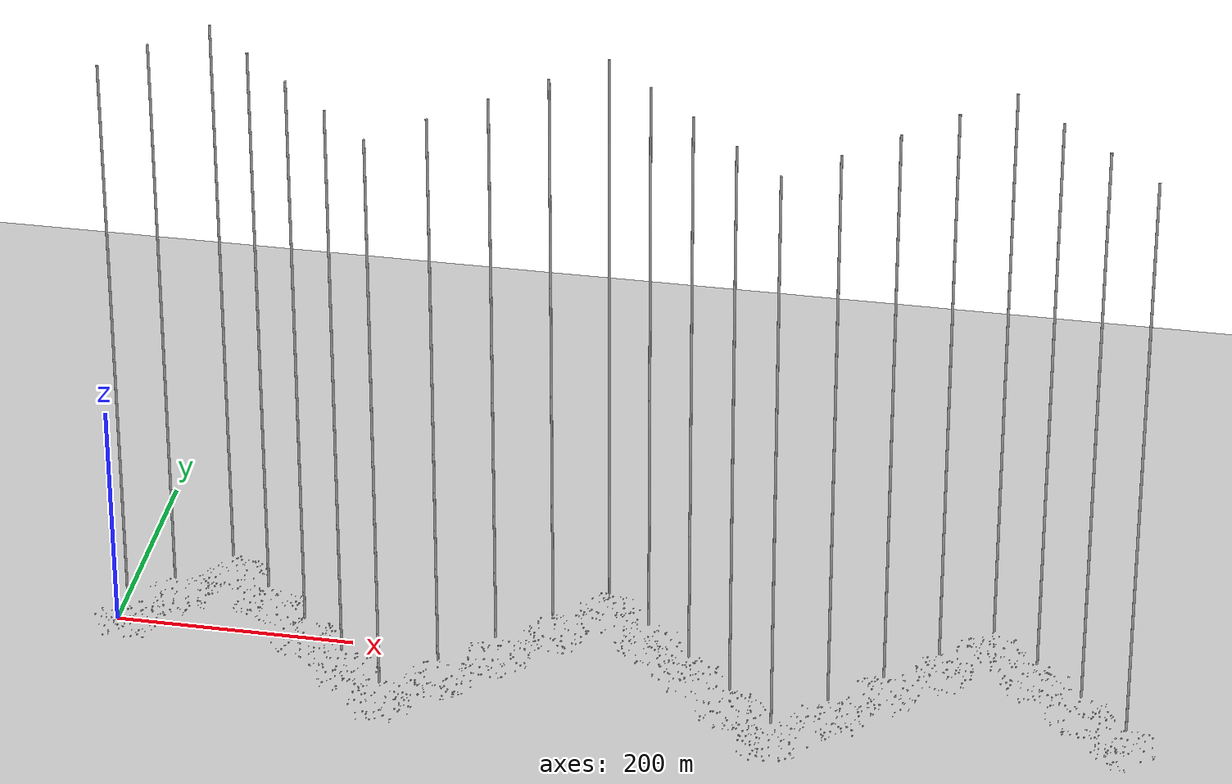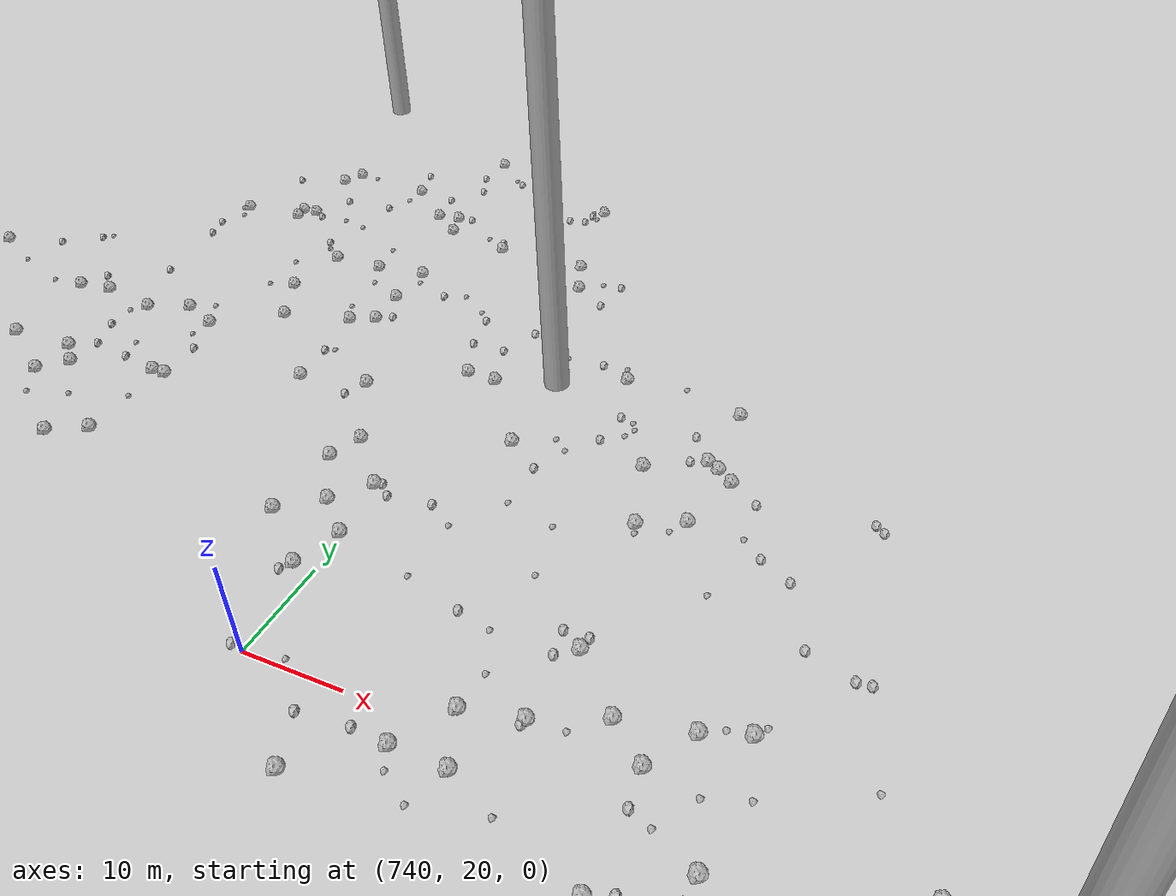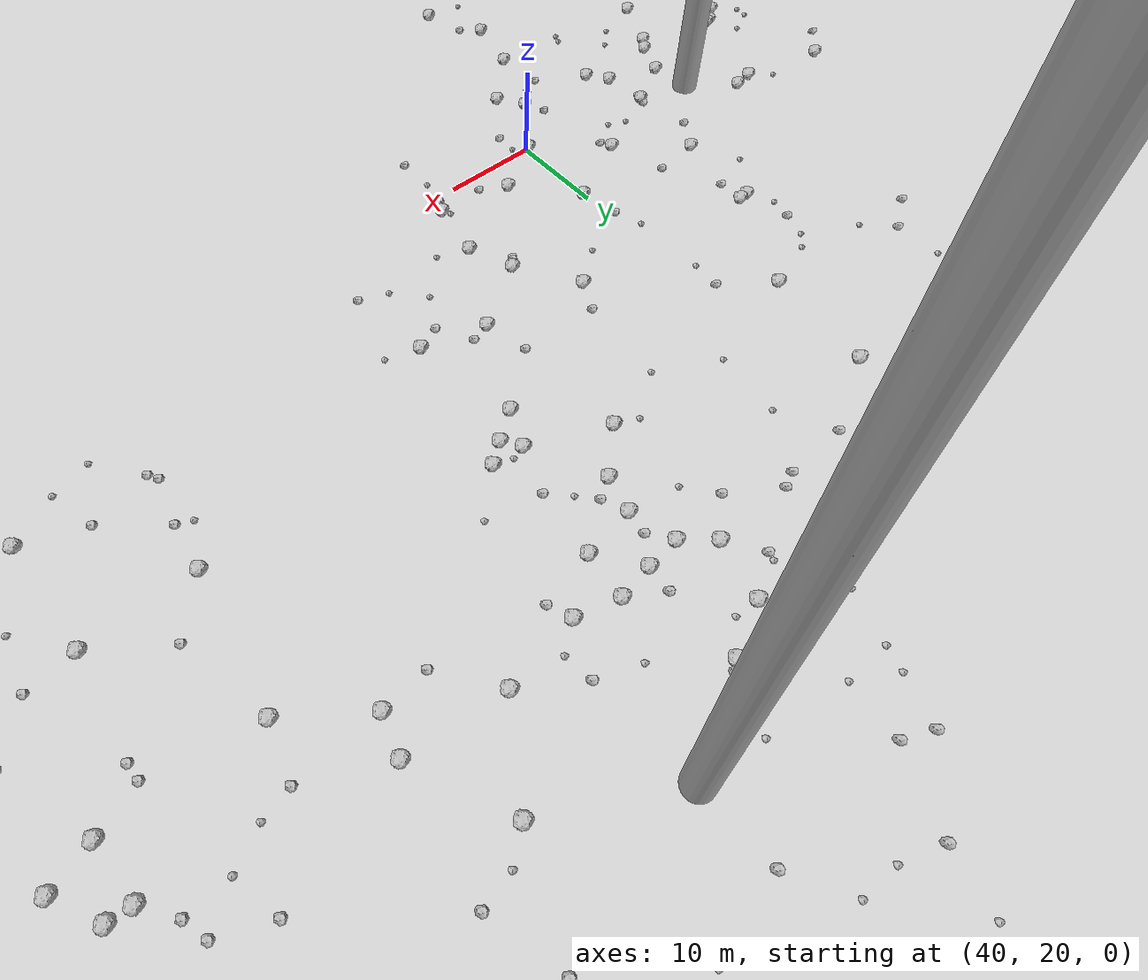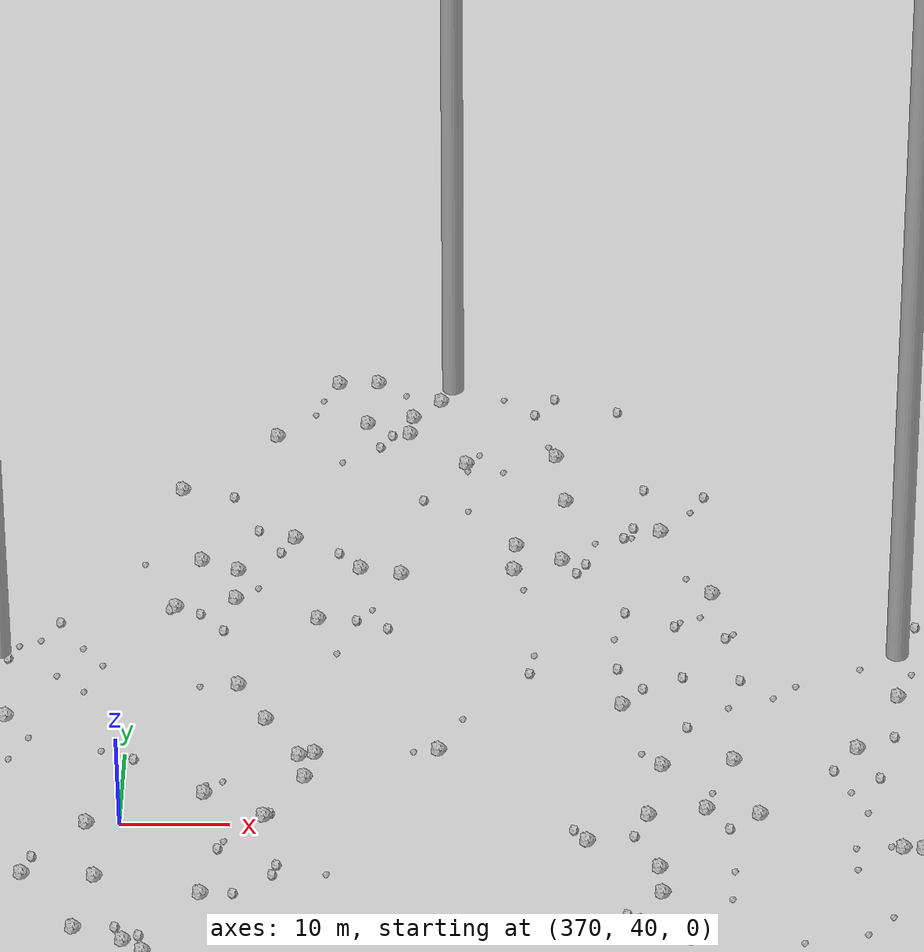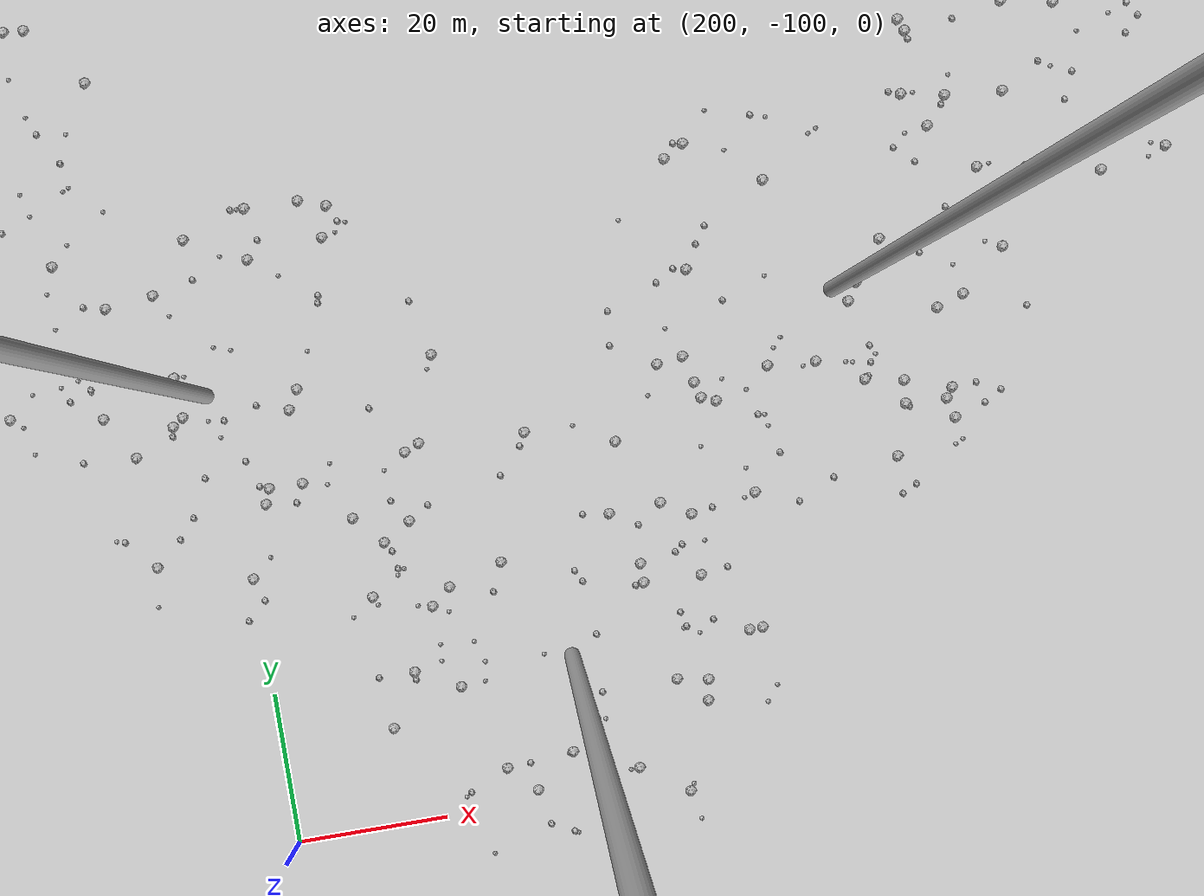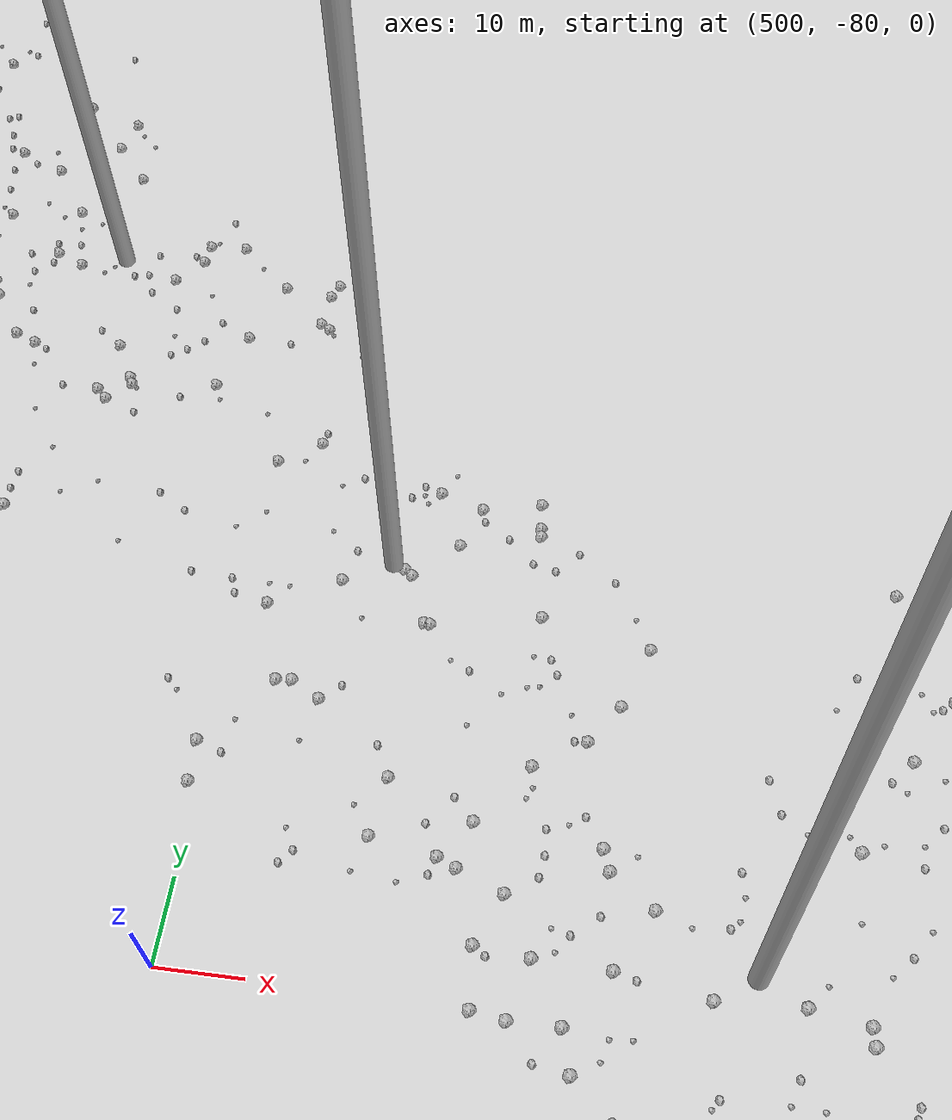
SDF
<sdf version="1.6">
 <world name="default">
  <include><uri>model://custom_ground</uri></include>
  <include><uri>model://sun</uri></include>
  <spherical_coordinates>
   <surface_model>EARTH_WGS84</surface_model>
   <latitude_deg>38.161479</latitude_deg>
   <longitude_deg>-122.454630</longitude_deg>
   <elevation>488.0</elevation>
   <heading_deg>90</heading_deg>
  </spherical_coordinates>
  <model name="rock1_0_0">
   <include><uri>model://rock1</uri><pose>5.3826163971432095 14.833915460122896 0.5 0 0 0</pose></include>
  </model>
  <model name="rock1_0_1">
   <include><uri>model://rock1</uri><pose>30.447518244006694 0.13891803665527291 0.5 0 0 0</pose></include>
  </model>
  <model name="rock1_0_2">
   <include><uri>model://rock1</uri><pose>2.5898749776114087 -8.997922072015974 0.5 0 0 0</pose></include>
  </model>
  <model name="rock1_0_3">
   <include><uri>model://rock1</uri><pose>22.018661945251147 -14.518125749165494 0.5 0 0 0</pose></include>
  </model>
  <model name="rock1_0_4">
   <include><uri>model://rock1</uri><pose>11.738256432796184 26.758494028316434 0.5 0 0 0</pose></include>
  </model>
  <model name="rock1_0_5">
   <include><uri>model://rock1</uri><pose>24.889400565742783 17.042585949610256 0.5 0 0 0</pose></include>
  </model>
  <model name="rock1_0_6">
   <include><uri>model://rock1</uri><pose>13.534504679959774 8.24101669516186 0.5 0 0 0</pose></include>
  </model>
  <model name="rock1_0_7">
   <include><uri>model://rock1</uri><pose>12.137205227243975 -25.386994723828195 0.5 0 0 0</pose></include>
  </model>
  <model name="rock1_0_8">
   <include><uri>model://rock1</uri><pose>32.02152474551937 6.439862818495428 0.5 0 0 0</pose></include>
  </model>
  <model name="rock1_0_9">
   <include><uri>model://rock1</uri><pose>13.982483947517053 27.139125043588002 0.5 0 0 0</pose></include>
  </model>
  <model name="rock1_0_10">
   <include><uri>model://rock1</uri><pose>22.27124170972136 -20.355734318314838 0.5 0 0 0</pose></include>
  </model>
  <model name="rock1_0_11">
   <include><uri>model://rock1</uri><pose>2.357629220583899 28.84419347674512 0.5 0 0 0</pose></include>
  </model>
  <model name="rock1_0_12">
   <include><uri>model://rock1</uri><pose>33.480842824594355 -6.354458076451795 0.5 0 0 0</pose></include>
  </model>
  <model name="rock1_0_13">
   <include><uri>model://rock1</uri><pose>-1.5949487735709234 -6.103101429644116 0.5 0 0 0</pose></include>
  </model>
  <model name="rock1_0_14">
   <include><uri>model://rock1</uri><pose>-16.18035129490665 12.500910345900515 0.5 0 0 0</pose></include>
  </model>
  <model name="rock1_0_15">
   <include><uri>model://rock1</uri><pose>17.565046872009702 15.384390584599615 0.5 0 0 0</pose></include>
  </model>
  <model name="rock1_0_16">
   <include><uri>model://rock1</uri><pose>-1.8895999373850003 -3.390053762345083 0.5 0 0 0</pose></include>
  </model>
  <model name="rock1_0_17">
   <include><uri>model://rock1</uri><pose>16.571297318726735 -2.6725973638123364 0.5 0 0 0</pose></include>
  </model>
  <model name="rock1_0_18">
   <include><uri>model://rock1</uri><pose>-5.239724703203688 -0.050935826409460816 0.5 0 0 0</pose></include>
  </model>
  <model name="rock1_0_19">
   <include><uri>model://rock1</uri><pose>17.80412472943207 -24.222778481294007 0.5 0 0 0</pose></include>
  </model>
  <model name="rock1_0_20">
   <include><uri>model://rock1</uri><pose>-7.593553679781337 -12.412526889327815 0.5 0 0 0</pose></include>
  </model>
  <model name="rock1_0_21">
   <include><uri>model://rock1</uri><pose>-3.3933310219554578 16.802599127154046 0.5 0 0 0</pose></include>
  </model>
  <model name="rock1_0_22">
   <include><uri>model://rock1</uri><pose>7.298195084800231 16.321862817131873 0.5 0 0 0</pose></include>
  </model>
  <model name="rock1_0_23">
   <include><uri>model://rock1</uri><pose>5.84447356881466 -2.2452999478449627 0.5 0 0 0</pose></include>
  </model>
  <model name="rock1_0_24">
   <include><uri>model://rock1</uri><pose>-19.816298962496326 2.9349189349045375 0.5 0 0 0</pose></include>
  </model>
  <model name="rock1_0_25">
   <include><uri>model://rock1</uri><pose>16.44552290676122 14.002501601590573 0.5 0 0 0</pose></include>
  </model>
  <model name="rock1_0_26">
   <include><uri>model://rock1</uri><pose>7.828417443083751 16.398951550373425 0.5 0 0 0</pose></include>
  </model>
  <model name="rock2_0_0">
   <include><uri>model://rock2</uri><pose>20.769088031303575 -1.3028528682348366 0.3 0 0 0</pose></include>
  </model>
  <model name="rock2_0_1">
   <include><uri>model://rock2</uri><pose>12.252481783612836 -5.68790336703433 0.3 0 0 0</pose></include>
  </model>
  <model name="rock2_0_2">
   <include><uri>model://rock2</uri><pose>-1.9813220653473635 -20.119825915808907 0.3 0 0 0</pose></include>
  </model>
  <model name="rock2_0_3">
   <include><uri>model://rock2</uri><pose>27.10365783653257 -23.571661268950912 0.3 0 0 0</pose></include>
  </model>
  <model name="rock2_0_4">
   <include><uri>model://rock2</uri><pose>31.61053136334582 11.6831301207839 0.3 0 0 0</pose></include>
  </model>
  <model name="rock2_0_5">
   <include><uri>model://rock2</uri><pose>12.211173855167011 5.818656164824681 0.3 0 0 0</pose></include>
  </model>
  <model name="rock2_0_6">
   <include><uri>model://rock2</uri><pose>32.27998359495686 -1.6168742194722228 0.3 0 0 0</pose></include>
  </model>
  <model name="rock2_0_7">
   <include><uri>model://rock2</uri><pose>0.31760263476304473 -8.519913160112822 0.3 0 0 0</pose></include>
  </model>
  <model name="rock2_0_8">
   <include><uri>model://rock2</uri><pose>7.795174416034964 -6.762517280145758 0.3 0 0 0</pose></include>
  </model>
  <model name="rock2_0_9">
   <include><uri>model://rock2</uri><pose>-15.080011776837994 9.752077347604626 0.3 0 0 0</pose></include>
  </model>
  <model name="rock2_0_10">
   <include><uri>model://rock2</uri><pose>27.228424582850728 -14.788774552205437 0.3 0 0 0</pose></include>
  </model>
  <model name="rock2_0_11">
   <include><uri>model://rock2</uri><pose>-3.32334583410098 -18.510501007391873 0.3 0 0 0</pose></include>
  </model>
  <model name="rock2_0_12">
   <include><uri>model://rock2</uri><pose>24.536811592186204 -11.68835426168149 0.3 0 0 0</pose></include>
  </model>
  <model name="rock2_0_13">
   <include><uri>model://rock2</uri><pose>2.183556464231348 -7.881472595733058 0.3 0 0 0</pose></include>
  </model>
  <model name="rock2_0_14">
   <include><uri>model://rock2</uri><pose>-12.562345230716774 -11.01128608196355 0.3 0 0 0</pose></include>
  </model>
  <model name="rock2_0_15">
   <include><uri>model://rock2</uri><pose>20.159737779902635 -17.379363077895054 0.3 0 0 0</pose></include>
  </model>
  <model name="rock2_0_16">
   <include><uri>model://rock2</uri><pose>-2.6413571710956987 -20.938865880234452 0.3 0 0 0</pose></include>
  </model>
  <model name="rock2_0_17">
   <include><uri>model://rock2</uri><pose>-9.27666162914747 -0.11095060411894053 0.3 0 0 0</pose></include>
  </model>
  <model name="rock2_0_18">
   <include><uri>model://rock2</uri><pose>-2.1006323928423463 -3.1407963141446054 0.3 0 0 0</pose></include>
  </model>
  <model name="rock2_0_19">
   <include><uri>model://rock2</uri><pose>-5.683190381064131 -25.288255724673718 0.3 0 0 0</pose></include>
  </model>
  <model name="rock2_0_20">
   <include><uri>model://rock2</uri><pose>5.058385165876079 -14.622472443625076 0.3 0 0 0</pose></include>
  </model>
  <model name="rock2_0_21">
   <include><uri>model://rock2</uri><pose>-0.8945777256669203 25.924378669265217 0.3 0 0 0</pose></include>
  </model>
  <model name="rock2_0_22">
   <include><uri>model://rock2</uri><pose>-13.764161152923513 0.6882229888067108 0.3 0 0 0</pose></include>
  </model>
  <model name="rock2_0_23">
   <include><uri>model://rock2</uri><pose>6.284273512704189 -9.699244818910248 0.3 0 0 0</pose></include>
  </model>
  <model name="rock2_0_24">
   <include><uri>model://rock2</uri><pose>7.589752302591542 -10.475553591488008 0.3 0 0 0</pose></include>
  </model>
  <model name="rock2_0_25">
   <include><uri>model://rock2</uri><pose>-1.9228808458546212 -23.32504609355527 0.3 0 0 0</pose></include>
  </model>
  <model name="rock2_0_26">
   <include><uri>model://rock2</uri><pose>-6.152529051250715 -25.00528854309053 0.3 0 0 0</pose></include>
  </model>
  <model name="rock3_0_0">
   <include><uri>model://rock3</uri><pose>28.081065351475914 -22.84034396658347 0.2 0 0 0</pose></include>
  </model>
  <model name="rock3_0_1">
   <include><uri>model://rock3</uri><pose>29.230410808589745 -5.8689867580851605 0.2 0 0 0</pose></include>
  </model>
  <model name="rock3_0_2">
   <include><uri>model://rock3</uri><pose>9.159643926815313 28.40282211108935 0.2 0 0 0</pose></include>
  </model>
  <model name="rock3_0_3">
   <include><uri>model://rock3</uri><pose>-5.626009920036184 -1.4977938695064204 0.2 0 0 0</pose></include>
  </model>
  <model name="rock3_0_4">
   <include><uri>model://rock3</uri><pose>18.352777240337836 -14.086205773006482 0.2 0 0 0</pose></include>
  </model>
  <model name="rock3_0_5">
   <include><uri>model://rock3</uri><pose>26.705259917280422 -11.799389815318296 0.2 0 0 0</pose></include>
  </model>
  <model name="rock3_0_6">
   <include><uri>model://rock3</uri><pose>4.266897134883109 -10.808405750458967 0.2 0 0 0</pose></include>
  </model>
  <model name="rock3_0_7">
   <include><uri>model://rock3</uri><pose>5.662910502363744 19.541997554999263 0.2 0 0 0</pose></include>
  </model>
  <model name="rock3_0_8">
   <include><uri>model://rock3</uri><pose>23.9309791468186 6.648569384758993 0.2 0 0 0</pose></include>
  </model>
  <model name="rock3_0_9">
   <include><uri>model://rock3</uri><pose>21.442989452478088 -23.302838587030408 0.2 0 0 0</pose></include>
  </model>
  <model name="rock3_0_10">
   <include><uri>model://rock3</uri><pose>-9.396061384966252 -14.432801067336401 0.2 0 0 0</pose></include>
  </model>
  <model name="rock3_0_11">
   <include><uri>model://rock3</uri><pose>27.78828730295347 -23.370615435261477 0.2 0 0 0</pose></include>
  </model>
  <model name="rock3_0_12">
   <include><uri>model://rock3</uri><pose>8.112972940312797 -3.063811121860059 0.2 0 0 0</pose></include>
  </model>
  <model name="rock3_0_13">
   <include><uri>model://rock3</uri><pose>9.31765260158145 5.0993271456499585 0.2 0 0 0</pose></include>
  </model>
  <model name="rock3_0_14">
   <include><uri>model://rock3</uri><pose>32.054247833319224 -11.403553499536109 0.2 0 0 0</pose></include>
  </model>
  <model name="rock3_0_15">
   <include><uri>model://rock3</uri><pose>36.62774008681354 11.51412206939382 0.2 0 0 0</pose></include>
  </model>
  <model name="rock3_0_16">
   <include><uri>model://rock3</uri><pose>-11.65362046633958 14.720918112732882 0.2 0 0 0</pose></include>
  </model>
  <model name="rock3_0_17">
   <include><uri>model://rock3</uri><pose>20.476305605343235 11.685653461753446 0.2 0 0 0</pose></include>
  </model>
  <model name="rock3_0_18">
   <include><uri>model://rock3</uri><pose>2.8327367364361393 18.169955786313444 0.2 0 0 0</pose></include>
  </model>
  <model name="rock3_0_19">
   <include><uri>model://rock3</uri><pose>18.479040442254394 9.801354748587762 0.2 0 0 0</pose></include>
  </model>
  <model name="rock3_0_20">
   <include><uri>model://rock3</uri><pose>-7.815740149222247 11.03172244589581 0.2 0 0 0</pose></include>
  </model>
  <model name="rock3_0_21">
   <include><uri>model://rock3</uri><pose>-10.992197707083072 5.525801072015483 0.2 0 0 0</pose></include>
  </model>
  <model name="rock3_0_22">
   <include><uri>model://rock3</uri><pose>15.838646199750869 -14.109227268238486 0.2 0 0 0</pose></include>
  </model>
  <model name="rock3_0_23">
   <include><uri>model://rock3</uri><pose>-6.637785227941249 -3.630444972965087 0.2 0 0 0</pose></include>
  </model>
  <model name="rock3_0_24">
   <include><uri>model://rock3</uri><pose>2.6880952406552474 16.790238365250275 0.2 0 0 0</pose></include>
  </model>
  <model name="rock3_0_25">
   <include><uri>model://rock3</uri><pose>-5.016818000739889 2.1321593831418753 0.2 0 0 0</pose></include>
  </model>
  <model name="rock3_0_26">
   <include><uri>model://rock3</uri><pose>24.366033653163782 7.61057857692559 0.2 0 0 0</pose></include>
  </model>
  <model name="rock1_1_0">
   <include><uri>model://rock1</uri><pose>68.50371622743845 49.20610894623815 0.5 0 0 0</pose></include>
  </model>
  <model name="rock1_1_1">
   <include><uri>model://rock1</uri><pose>39.7842277104102 20.10195982798745 0.5 0 0 0</pose></include>
  </model>
  <model name="rock1_1_2">
   <include><uri>model://rock1</uri><pose>37.279947172991 11.584888515261419 0.5 0 0 0</pose></include>
  </model>
  <model name="rock1_1_3">
   <include><uri>model://rock1</uri><pose>40.18369266264232 29.396562711026682 0.5 0 0 0</pose></include>
  </model>
  <model name="rock1_1_4">
   <include><uri>model://rock1</uri><pose>27.012425716175045 40.292693485322545 0.5 0 0 0</pose></include>
  </model>
  <model name="rock1_1_5">
   <include><uri>model://rock1</uri><pose>65.63405500308355 35.10571148871781 0.5 0 0 0</pose></include>
  </model>
  <model name="rock1_1_6">
   <include><uri>model://rock1</uri><pose>26.011575027155555 31.272116230707493 0.5 0 0 0</pose></include>
  </model>
  <model name="rock1_1_7">
   <include><uri>model://rock1</uri><pose>19.34364966957558 19.052302490988048 0.5 0 0 0</pose></include>
  </model>
  <model name="rock1_1_8">
   <include><uri>model://rock1</uri><pose>48.5922751036391 38.64936974237603 0.5 0 0 0</pose></include>
  </model>
  <model name="rock1_1_9">
   <include><uri>model://rock1</uri><pose>26.47280440097375 14.826959940464079 0.5 0 0 0</pose></include>
  </model>
  <model name="rock1_1_10">
   <include><uri>model://rock1</uri><pose>54.30889667339726 28.033167340622185 0.5 0 0 0</pose></include>
  </model>
  <model name="rock1_1_11">
   <include><uri>model://rock1</uri><pose>35.41101930056376 14.318443575680657 0.5 0 0 0</pose></include>
  </model>
  <model name="rock1_1_12">
   <include><uri>model://rock1</uri><pose>66.54031267801085 47.72591313493635 0.5 0 0 0</pose></include>
  </model>
  <model name="rock1_1_13">
   <include><uri>model://rock1</uri><pose>65.35171561232764 49.41473961008027 0.5 0 0 0</pose></include>
  </model>
  <model name="rock1_1_14">
   <include><uri>model://rock1</uri><pose>57.724307831394654 52.683864578889015 0.5 0 0 0</pose></include>
  </model>
  <model name="rock1_1_15">
   <include><uri>model://rock1</uri><pose>52.54861407070724 32.64042503349264 0.5 0 0 0</pose></include>
  </model>
  <model name="rock1_1_16">
   <include><uri>model://rock1</uri><pose>52.94386653199112 20.898382209449828 0.5 0 0 0</pose></include>
  </model>
  <model name="rock1_1_17">
   <include><uri>model://rock1</uri><pose>27.984428353750847 40.36226044400993 0.5 0 0 0</pose></include>
  </model>
  <model name="rock1_1_18">
   <include><uri>model://rock1</uri><pose>28.77757744126259 64.77772881849373 0.5 0 0 0</pose></include>
  </model>
  <model name="rock1_1_19">
   <include><uri>model://rock1</uri><pose>33.81596085475101 50.677464074795786 0.5 0 0 0</pose></include>
  </model>
  <model name="rock1_1_20">
   <include><uri>model://rock1</uri><pose>35.25861275136729 61.6881182440075 0.5 0 0 0</pose></include>
  </model>
  <model name="rock1_1_21">
   <include><uri>model://rock1</uri><pose>45.47611123777945 23.48300542014895 0.5 0 0 0</pose></include>
  </model>
  <model name="rock1_1_22">
   <include><uri>model://rock1</uri><pose>53.15491222845305 22.041297270286893 0.5 0 0 0</pose></include>
  </model>
  <model name="rock1_1_23">
   <include><uri>model://rock1</uri><pose>63.713707886968415 45.72974609407788 0.5 0 0 0</pose></include>
  </model>
  <model name="rock1_1_24">
   <include><uri>model://rock1</uri><pose>59.17879057768169 36.86000123917398 0.5 0 0 0</pose></include>
  </model>
  <model name="rock1_1_25">
   <include><uri>model://rock1</uri><pose>24.482851584330636 21.87696546064422 0.5 0 0 0</pose></include>
  </model>
  <model name="rock1_1_26">
   <include><uri>model://rock1</uri><pose>32.681757464394465 25.7577455323219 0.5 0 0 0</pose></include>
  </model>
  <model name="rock2_1_0">
   <include><uri>model://rock2</uri><pose>32.887653906026564 66.48478873533378 0.3 0 0 0</pose></include>
  </model>
  <model name="rock2_1_1">
   <include><uri>model://rock2</uri><pose>49.300041032516184 65.84895079577767 0.3 0 0 0</pose></include>
  </model>
  <model name="rock2_1_2">
   <include><uri>model://rock2</uri><pose>50.111761128535356 41.698837569005406 0.3 0 0 0</pose></include>
  </model>
  <model name="rock2_1_3">
   <include><uri>model://rock2</uri><pose>61.14108089583475 37.447205329100484 0.3 0 0 0</pose></include>
  </model>
  <model name="rock2_1_4">
   <include><uri>model://rock2</uri><pose>39.3645629856436 33.508807286994276 0.3 0 0 0</pose></include>
  </model>
  <model name="rock2_1_5">
   <include><uri>model://rock2</uri><pose>51.94077979373715 13.891251176435569 0.3 0 0 0</pose></include>
  </model>
  <model name="rock2_1_6">
   <include><uri>model://rock2</uri><pose>50.847173503174794 66.49540104038702 0.3 0 0 0</pose></include>
  </model>
  <model name="rock2_1_7">
   <include><uri>model://rock2</uri><pose>58.16910009994139 41.333894477134216 0.3 0 0 0</pose></include>
  </model>
  <model name="rock2_1_8">
   <include><uri>model://rock2</uri><pose>66.75583214494799 26.56913422805072 0.3 0 0 0</pose></include>
  </model>
  <model name="rock2_1_9">
   <include><uri>model://rock2</uri><pose>14.871339499025362 51.15063280740106 0.3 0 0 0</pose></include>
  </model>
  <model name="rock2_1_10">
   <include><uri>model://rock2</uri><pose>33.65020407921925 12.678955635030727 0.3 0 0 0</pose></include>
  </model>
  <model name="rock2_1_11">
   <include><uri>model://rock2</uri><pose>51.650376479009466 31.63178397243839 0.3 0 0 0</pose></include>
  </model>
  <model name="rock2_1_12">
   <include><uri>model://rock2</uri><pose>42.90920693443164 65.66956636077295 0.3 0 0 0</pose></include>
  </model>
  <model name="rock2_1_13">
   <include><uri>model://rock2</uri><pose>34.282846166485214 16.428705377904404 0.3 0 0 0</pose></include>
  </model>
  <model name="rock2_1_14">
   <include><uri>model://rock2</uri><pose>27.778560809956254 37.562196681677435 0.3 0 0 0</pose></include>
  </model>
  <model name="rock2_1_15">
   <include><uri>model://rock2</uri><pose>30.86967756142871 31.805745068769284 0.3 0 0 0</pose></include>
  </model>
  <model name="rock2_1_16">
   <include><uri>model://rock2</uri><pose>41.25194595420916 16.975723080061336 0.3 0 0 0</pose></include>
  </model>
  <model name="rock2_1_17">
   <include><uri>model://rock2</uri><pose>38.6605399611273 47.03452087426721 0.3 0 0 0</pose></include>
  </model>
  <model name="rock2_1_18">
   <include><uri>model://rock2</uri><pose>26.594334046833584 62.250794070002115 0.3 0 0 0</pose></include>
  </model>
  <model name="rock2_1_19">
   <include><uri>model://rock2</uri><pose>26.0168829384262 45.143980591761995 0.3 0 0 0</pose></include>
  </model>
  <model name="rock2_1_20">
   <include><uri>model://rock2</uri><pose>18.50215375710122 53.41663729318411 0.3 0 0 0</pose></include>
  </model>
  <model name="rock2_1_21">
   <include><uri>model://rock2</uri><pose>63.13626881759434 34.08428227314859 0.3 0 0 0</pose></include>
  </model>
  <model name="rock2_1_22">
   <include><uri>model://rock2</uri><pose>33.18580647874042 24.572472251781633 0.3 0 0 0</pose></include>
  </model>
  <model name="rock2_1_23">
   <include><uri>model://rock2</uri><pose>48.12200354957686 21.934676205805992 0.3 0 0 0</pose></include>
  </model>
  <model name="rock2_1_24">
   <include><uri>model://rock2</uri><pose>24.667467453526005 22.584044120519604 0.3 0 0 0</pose></include>
  </model>
  <model name="rock2_1_25">
   <include><uri>model://rock2</uri><pose>23.640558560604994 28.018202830399417 0.3 0 0 0</pose></include>
  </model>
  <model name="rock2_1_26">
   <include><uri>model://rock2</uri><pose>51.826097445488315 31.890245583304793 0.3 0 0 0</pose></include>
  </model>
  <model name="rock3_1_0">
   <include><uri>model://rock3</uri><pose>51.004729561962705 50.61346057702281 0.2 0 0 0</pose></include>
  </model>
  <model name="rock3_1_1">
   <include><uri>model://rock3</uri><pose>28.386343002420112 23.59822171355829 0.2 0 0 0</pose></include>
  </model>
  <model name="rock3_1_2">
   <include><uri>model://rock3</uri><pose>65.09731049425477 55.804908489480596 0.2 0 0 0</pose></include>
  </model>
  <model name="rock3_1_3">
   <include><uri>model://rock3</uri><pose>25.396165349689056 42.84574556579775 0.2 0 0 0</pose></include>
  </model>
  <model name="rock3_1_4">
   <include><uri>model://rock3</uri><pose>57.4097074754304 26.737236300576313 0.2 0 0 0</pose></include>
  </model>
  <model name="rock3_1_5">
   <include><uri>model://rock3</uri><pose>24.216010127793602 20.936876114748323 0.2 0 0 0</pose></include>
  </model>
  <model name="rock3_1_6">
   <include><uri>model://rock3</uri><pose>44.86411956127349 53.78142859167014 0.2 0 0 0</pose></include>
  </model>
  <model name="rock3_1_7">
   <include><uri>model://rock3</uri><pose>41.239129202140006 19.119431045557754 0.2 0 0 0</pose></include>
  </model>
  <model name="rock3_1_8">
   <include><uri>model://rock3</uri><pose>28.23227594874046 48.98264665047703 0.2 0 0 0</pose></include>
  </model>
  <model name="rock3_1_9">
   <include><uri>model://rock3</uri><pose>57.725233762247335 60.700458207551925 0.2 0 0 0</pose></include>
  </model>
  <model name="rock3_1_10">
   <include><uri>model://rock3</uri><pose>55.38953435977919 53.6383654032984 0.2 0 0 0</pose></include>
  </model>
  <model name="rock3_1_11">
   <include><uri>model://rock3</uri><pose>51.82245939963629 17.783309532500056 0.2 0 0 0</pose></include>
  </model>
  <model name="rock3_1_12">
   <include><uri>model://rock3</uri><pose>44.78629279784593 35.91556209415869 0.2 0 0 0</pose></include>
  </model>
  <model name="rock3_1_13">
   <include><uri>model://rock3</uri><pose>26.875412970957424 47.693545863134425 0.2 0 0 0</pose></include>
  </model>
  <model name="rock3_1_14">
   <include><uri>model://rock3</uri><pose>52.54328673985414 22.74369667190865 0.2 0 0 0</pose></include>
  </model>
  <model name="rock3_1_15">
   <include><uri>model://rock3</uri><pose>30.27558528254992 22.762150887541473 0.2 0 0 0</pose></include>
  </model>
  <model name="rock3_1_16">
   <include><uri>model://rock3</uri><pose>61.09790847037699 30.51586159339389 0.2 0 0 0</pose></include>
  </model>
  <model name="rock3_1_17">
   <include><uri>model://rock3</uri><pose>66.62680705347297 49.75546169600969 0.2 0 0 0</pose></include>
  </model>
  <model name="rock3_1_18">
   <include><uri>model://rock3</uri><pose>45.70300298700179 60.48451308399315 0.2 0 0 0</pose></include>
  </model>
  <model name="rock3_1_19">
   <include><uri>model://rock3</uri><pose>68.94104440702495 34.00617815649978 0.2 0 0 0</pose></include>
  </model>
  <model name="rock3_1_20">
   <include><uri>model://rock3</uri><pose>38.284591633321796 43.99269308942479 0.2 0 0 0</pose></include>
  </model>
  <model name="rock3_1_21">
   <include><uri>model://rock3</uri><pose>63.84439339711452 27.610003376688695 0.2 0 0 0</pose></include>
  </model>
  <model name="rock3_1_22">
   <include><uri>model://rock3</uri><pose>46.305035172735636 69.09828656002286 0.2 0 0 0</pose></include>
  </model>
  <model name="rock3_1_23">
   <include><uri>model://rock3</uri><pose>38.35442798159224 36.32515855135571 0.2 0 0 0</pose></include>
  </model>
  <model name="rock3_1_24">
   <include><uri>model://rock3</uri><pose>23.208898199853106 36.05848792044005 0.2 0 0 0</pose></include>
  </model>
  <model name="rock3_1_25">
   <include><uri>model://rock3</uri><pose>21.23456857932208 50.658854239804455 0.2 0 0 0</pose></include>
  </model>
  <model name="rock3_1_26">
   <include><uri>model://rock3</uri><pose>18.392987288965276 58.226765947251 0.2 0 0 0</pose></include>
  </model>
  <model name="rock1_2_0">
   <include><uri>model://rock1</uri><pose>91.01138022328277 102.29958594091241 0.5 0 0 0</pose></include>
  </model>
  <model name="rock1_2_1">
   <include><uri>model://rock1</uri><pose>64.92205166233978 64.40687015665233 0.5 0 0 0</pose></include>
  </model>
  <model name="rock1_2_2">
   <include><uri>model://rock1</uri><pose>104.5466627890128 93.56256300775114 0.5 0 0 0</pose></include>
  </model>
  <model name="rock1_2_3">
   <include><uri>model://rock1</uri><pose>77.13737104329749 104.89723773686973 0.5 0 0 0</pose></include>
  </model>
  <model name="rock1_2_4">
   <include><uri>model://rock1</uri><pose>88.90308808764513 63.89937917464586 0.5 0 0 0</pose></include>
  </model>
  <model name="rock1_2_5">
   <include><uri>model://rock1</uri><pose>60.385686482717844 71.78235785653841 0.5 0 0 0</pose></include>
  </model>
  <model name="rock1_2_6">
   <include><uri>model://rock1</uri><pose>78.8195008808456 94.7904590199833 0.5 0 0 0</pose></include>
  </model>
  <model name="rock1_2_7">
   <include><uri>model://rock1</uri><pose>79.05191867417003 108.48909560251411 0.5 0 0 0</pose></include>
  </model>
  <model name="rock1_2_8">
   <include><uri>model://rock1</uri><pose>87.92344682607039 60.28252832470291 0.5 0 0 0</pose></include>
  </model>
  <model name="rock1_2_9">
   <include><uri>model://rock1</uri><pose>62.74613290360951 59.78204797545849 0.5 0 0 0</pose></include>
  </model>
  <model name="rock1_2_10">
   <include><uri>model://rock1</uri><pose>65.1813992366356 73.98734162147812 0.5 0 0 0</pose></include>
  </model>
  <model name="rock1_2_11">
   <include><uri>model://rock1</uri><pose>100.48459576365626 87.83072048275173 0.5 0 0 0</pose></include>
  </model>
  <model name="rock1_2_12">
   <include><uri>model://rock1</uri><pose>88.92126397261691 88.8844897110336 0.5 0 0 0</pose></include>
  </model>
  <model name="rock1_2_13">
   <include><uri>model://rock1</uri><pose>68.38853401272311 64.92713040592929 0.5 0 0 0</pose></include>
  </model>
  <model name="rock1_2_14">
   <include><uri>model://rock1</uri><pose>73.66841001503182 99.90006258766687 0.5 0 0 0</pose></include>
  </model>
  <model name="rock1_2_15">
   <include><uri>model://rock1</uri><pose>99.46810939864775 99.96057398503842 0.5 0 0 0</pose></include>
  </model>
  <model name="rock1_2_16">
   <include><uri>model://rock1</uri><pose>67.89251161586785 60.52177402091152 0.5 0 0 0</pose></include>
  </model>
  <model name="rock1_2_17">
   <include><uri>model://rock1</uri><pose>61.76447213490241 56.32366432771103 0.5 0 0 0</pose></include>
  </model>
  <model name="rock1_2_18">
   <include><uri>model://rock1</uri><pose>81.02500101960607 103.40504679302516 0.5 0 0 0</pose></include>
  </model>
  <model name="rock1_2_19">
   <include><uri>model://rock1</uri><pose>94.54543255847898 55.47676011120305 0.5 0 0 0</pose></include>
  </model>
  <model name="rock1_2_20">
   <include><uri>model://rock1</uri><pose>61.6184644265571 64.10875878443679 0.5 0 0 0</pose></include>
  </model>
  <model name="rock1_2_21">
   <include><uri>model://rock1</uri><pose>84.86363259822127 72.4984596036081 0.5 0 0 0</pose></include>
  </model>
  <model name="rock1_2_22">
   <include><uri>model://rock1</uri><pose>58.86748378704505 66.36944885501919 0.5 0 0 0</pose></include>
  </model>
  <model name="rock1_2_23">
   <include><uri>model://rock1</uri><pose>93.04488134452592 101.32911778854266 0.5 0 0 0</pose></include>
  </model>
  <model name="rock1_2_24">
   <include><uri>model://rock1</uri><pose>79.76702546874614 64.93257942316718 0.5 0 0 0</pose></include>
  </model>
  <model name="rock1_2_25">
   <include><uri>model://rock1</uri><pose>72.47641495181828 63.78877492247463 0.5 0 0 0</pose></include>
  </model>
  <model name="rock1_2_26">
   <include><uri>model://rock1</uri><pose>100.98485956140021 90.15546249890313 0.5 0 0 0</pose></include>
  </model>
  <model name="rock2_2_0">
   <include><uri>model://rock2</uri><pose>74.56192535107294 68.32836847488903 0.3 0 0 0</pose></include>
  </model>
  <model name="rock2_2_1">
   <include><uri>model://rock2</uri><pose>65.10635533803104 66.93315042651352 0.3 0 0 0</pose></include>
  </model>
  <model name="rock2_2_2">
   <include><uri>model://rock2</uri><pose>67.01110802292891 54.00317899802823 0.3 0 0 0</pose></include>
  </model>
  <model name="rock2_2_3">
   <include><uri>model://rock2</uri><pose>73.74876880305658 85.58919116721245 0.3 0 0 0</pose></include>
  </model>
  <model name="rock2_2_4">
   <include><uri>model://rock2</uri><pose>65.91380891962824 74.62006675975583 0.3 0 0 0</pose></include>
  </model>
  <model name="rock2_2_5">
   <include><uri>model://rock2</uri><pose>95.81870597761358 60.50452904363481 0.3 0 0 0</pose></include>
  </model>
  <model name="rock2_2_6">
   <include><uri>model://rock2</uri><pose>90.48091347224715 75.03577643591501 0.3 0 0 0</pose></include>
  </model>
  <model name="rock2_2_7">
   <include><uri>model://rock2</uri><pose>102.95283228066714 86.61058637042967 0.3 0 0 0</pose></include>
  </model>
  <model name="rock2_2_8">
   <include><uri>model://rock2</uri><pose>96.1963113183802 95.59828684029688 0.3 0 0 0</pose></include>
  </model>
  <model name="rock2_2_9">
   <include><uri>model://rock2</uri><pose>88.578396788834 81.44516553328059 0.3 0 0 0</pose></include>
  </model>
  <model name="rock2_2_10">
   <include><uri>model://rock2</uri><pose>73.28858352905742 61.66355766415339 0.3 0 0 0</pose></include>
  </model>
  <model name="rock2_2_11">
   <include><uri>model://rock2</uri><pose>97.2561633360286 77.88943147899118 0.3 0 0 0</pose></include>
  </model>
  <model name="rock2_2_12">
   <include><uri>model://rock2</uri><pose>83.30157793387102 97.01979833767012 0.3 0 0 0</pose></include>
  </model>
  <model name="rock2_2_13">
   <include><uri>model://rock2</uri><pose>63.66868188080451 57.45846555835894 0.3 0 0 0</pose></include>
  </model>
  <model name="rock2_2_14">
   <include><uri>model://rock2</uri><pose>85.28450324505764 96.16535975023689 0.3 0 0 0</pose></include>
  </model>
  <model name="rock2_2_15">
   <include><uri>model://rock2</uri><pose>51.98084249505616 73.9808407076068 0.3 0 0 0</pose></include>
  </model>
  <model name="rock2_2_16">
   <include><uri>model://rock2</uri><pose>100.76077311241437 67.05553161591348 0.3 0 0 0</pose></include>
  </model>
  <model name="rock2_2_17">
   <include><uri>model://rock2</uri><pose>94.96015018373882 103.99079975899288 0.3 0 0 0</pose></include>
  </model>
  <model name="rock2_2_18">
   <include><uri>model://rock2</uri><pose>60.57388420034856 85.51198827499569 0.3 0 0 0</pose></include>
  </model>
  <model name="rock2_2_19">
   <include><uri>model://rock2</uri><pose>63.06489083687712 62.05032452027345 0.3 0 0 0</pose></include>
  </model>
  <model name="rock2_2_20">
   <include><uri>model://rock2</uri><pose>92.77318803790888 103.79476467059011 0.3 0 0 0</pose></include>
  </model>
  <model name="rock2_2_21">
   <include><uri>model://rock2</uri><pose>55.48790891832169 63.50829804472711 0.3 0 0 0</pose></include>
  </model>
  <model name="rock2_2_22">
   <include><uri>model://rock2</uri><pose>56.55793958260648 69.60843948954408 0.3 0 0 0</pose></include>
  </model>
  <model name="rock2_2_23">
   <include><uri>model://rock2</uri><pose>83.53266450219627 59.8890431614936 0.3 0 0 0</pose></include>
  </model>
  <model name="rock2_2_24">
   <include><uri>model://rock2</uri><pose>57.911893673308064 86.73376533283616 0.3 0 0 0</pose></include>
  </model>
  <model name="rock2_2_25">
   <include><uri>model://rock2</uri><pose>78.60847463812686 93.68179552523674 0.3 0 0 0</pose></include>
  </model>
  <model name="rock2_2_26">
   <include><uri>model://rock2</uri><pose>63.67691807431662 91.80436420115753 0.3 0 0 0</pose></include>
  </model>
  <model name="rock3_2_0">
   <include><uri>model://rock3</uri><pose>67.33774260324232 90.47758316940505 0.2 0 0 0</pose></include>
  </model>
  <model name="rock3_2_1">
   <include><uri>model://rock3</uri><pose>74.89538705124741 65.58141072003161 0.2 0 0 0</pose></include>
  </model>
  <model name="rock3_2_2">
   <include><uri>model://rock3</uri><pose>98.65281345362361 61.15076087099369 0.2 0 0 0</pose></include>
  </model>
  <model name="rock3_2_3">
   <include><uri>model://rock3</uri><pose>104.59853896422015 85.7657206255245 0.2 0 0 0</pose></include>
  </model>
  <model name="rock3_2_4">
   <include><uri>model://rock3</uri><pose>85.03973687758395 82.15861981167342 0.2 0 0 0</pose></include>
  </model>
  <model name="rock3_2_5">
   <include><uri>model://rock3</uri><pose>80.92102671881007 87.00284253641743 0.2 0 0 0</pose></include>
  </model>
  <model name="rock3_2_6">
   <include><uri>model://rock3</uri><pose>56.751565303197076 70.31952050756755 0.2 0 0 0</pose></include>
  </model>
  <model name="rock3_2_7">
   <include><uri>model://rock3</uri><pose>86.58107437515955 104.02680334326692 0.2 0 0 0</pose></include>
  </model>
  <model name="rock3_2_8">
   <include><uri>model://rock3</uri><pose>56.2673157021224 82.56154179419184 0.2 0 0 0</pose></include>
  </model>
  <model name="rock3_2_9">
   <include><uri>model://rock3</uri><pose>65.03148214700656 96.76952131248126 0.2 0 0 0</pose></include>
  </model>
  <model name="rock3_2_10">
   <include><uri>model://rock3</uri><pose>59.95636670627828 80.44045318967852 0.2 0 0 0</pose></include>
  </model>
  <model name="rock3_2_11">
   <include><uri>model://rock3</uri><pose>87.33371354225733 74.37841470749257 0.2 0 0 0</pose></include>
  </model>
  <model name="rock3_2_12">
   <include><uri>model://rock3</uri><pose>75.62967085872641 104.71267620821024 0.2 0 0 0</pose></include>
  </model>
  <model name="rock3_2_13">
   <include><uri>model://rock3</uri><pose>70.82658313182624 90.31975436863635 0.2 0 0 0</pose></include>
  </model>
  <model name="rock3_2_14">
   <include><uri>model://rock3</uri><pose>53.899324766271796 75.8180238883905 0.2 0 0 0</pose></include>
  </model>
  <model name="rock3_2_15">
   <include><uri>model://rock3</uri><pose>108.96493216849264 81.0762690146676 0.2 0 0 0</pose></include>
  </model>
  <model name="rock3_2_16">
   <include><uri>model://rock3</uri><pose>102.51410170014202 83.58075650318563 0.2 0 0 0</pose></include>
  </model>
  <model name="rock3_2_17">
   <include><uri>model://rock3</uri><pose>92.15591098829911 88.66697724993796 0.2 0 0 0</pose></include>
  </model>
  <model name="rock3_2_18">
   <include><uri>model://rock3</uri><pose>108.95321327466374 78.71853863209358 0.2 0 0 0</pose></include>
  </model>
  <model name="rock3_2_19">
   <include><uri>model://rock3</uri><pose>67.83847459176052 79.32263493328713 0.2 0 0 0</pose></include>
  </model>
  <model name="rock3_2_20">
   <include><uri>model://rock3</uri><pose>62.62082357142289 71.63760007855734 0.2 0 0 0</pose></include>
  </model>
  <model name="rock3_2_21">
   <include><uri>model://rock3</uri><pose>72.35692809307487 52.843459262103856 0.2 0 0 0</pose></include>
  </model>
  <model name="rock3_2_22">
   <include><uri>model://rock3</uri><pose>70.61116985432258 69.81793867160044 0.2 0 0 0</pose></include>
  </model>
  <model name="rock3_2_23">
   <include><uri>model://rock3</uri><pose>84.92898161720746 100.2984998379227 0.2 0 0 0</pose></include>
  </model>
  <model name="rock3_2_24">
   <include><uri>model://rock3</uri><pose>55.55117588512496 80.45843675001304 0.2 0 0 0</pose></include>
  </model>
  <model name="rock3_2_25">
   <include><uri>model://rock3</uri><pose>98.13208347099823 97.79870546735687 0.2 0 0 0</pose></include>
  </model>
  <model name="rock3_2_26">
   <include><uri>model://rock3</uri><pose>106.69069958667382 85.76452480830733 0.2 0 0 0</pose></include>
  </model>
  <model name="rock1_3_0">
   <include><uri>model://rock1</uri><pose>116.9255449918705 63.671924176833215 0.5 0 0 0</pose></include>
  </model>
  <model name="rock1_3_1">
   <include><uri>model://rock1</uri><pose>104.17021954970679 24.56281347260001 0.5 0 0 0</pose></include>
  </model>
  <model name="rock1_3_2">
   <include><uri>model://rock1</uri><pose>142.3258272072216 39.27766298475952 0.5 0 0 0</pose></include>
  </model>
  <model name="rock1_3_3">
   <include><uri>model://rock1</uri><pose>111.42584896205302 36.274030953535416 0.5 0 0 0</pose></include>
  </model>
  <model name="rock1_3_4">
   <include><uri>model://rock1</uri><pose>105.5210745020064 31.263905098417595 0.5 0 0 0</pose></include>
  </model>
  <model name="rock1_3_5">
   <include><uri>model://rock1</uri><pose>143.45303470162855 48.539402761149226 0.5 0 0 0</pose></include>
  </model>
  <model name="rock1_3_6">
   <include><uri>model://rock1</uri><pose>139.866687737679 50.23299422505597 0.5 0 0 0</pose></include>
  </model>
  <model name="rock1_3_7">
   <include><uri>model://rock1</uri><pose>136.72447086888675 47.57078696026566 0.5 0 0 0</pose></include>
  </model>
  <model name="rock1_3_8">
   <include><uri>model://rock1</uri><pose>111.86392210903304 56.21513632740902 0.5 0 0 0</pose></include>
  </model>
  <model name="rock1_3_9">
   <include><uri>model://rock1</uri><pose>111.58123801952793 46.41631256724577 0.5 0 0 0</pose></include>
  </model>
  <model name="rock1_3_10">
   <include><uri>model://rock1</uri><pose>129.05304907079326 28.438147467655114 0.5 0 0 0</pose></include>
  </model>
  <model name="rock1_3_11">
   <include><uri>model://rock1</uri><pose>138.57968180918758 43.50332819228715 0.5 0 0 0</pose></include>
  </model>
  <model name="rock1_3_12">
   <include><uri>model://rock1</uri><pose>102.96941861998161 41.97741905013365 0.5 0 0 0</pose></include>
  </model>
  <model name="rock1_3_13">
   <include><uri>model://rock1</uri><pose>138.593552106032 25.818642515468838 0.5 0 0 0</pose></include>
  </model>
  <model name="rock1_3_14">
   <include><uri>model://rock1</uri><pose>107.95745243255581 55.005338740542726 0.5 0 0 0</pose></include>
  </model>
  <model name="rock1_3_15">
   <include><uri>model://rock1</uri><pose>116.38255437586845 18.856741516632802 0.5 0 0 0</pose></include>
  </model>
  <model name="rock1_3_16">
   <include><uri>model://rock1</uri><pose>109.64733529163277 60.171622302681904 0.5 0 0 0</pose></include>
  </model>
  <model name="rock1_3_17">
   <include><uri>model://rock1</uri><pose>122.33658102696256 57.670401057750134 0.5 0 0 0</pose></include>
  </model>
  <model name="rock1_3_18">
   <include><uri>model://rock1</uri><pose>103.14862460678032 30.591114347729576 0.5 0 0 0</pose></include>
  </model>
  <model name="rock1_3_19">
   <include><uri>model://rock1</uri><pose>122.87623973156549 56.35812733762869 0.5 0 0 0</pose></include>
  </model>
  <model name="rock1_3_20">
   <include><uri>model://rock1</uri><pose>116.98368431731225 62.95491523615067 0.5 0 0 0</pose></include>
  </model>
  <model name="rock1_3_21">
   <include><uri>model://rock1</uri><pose>142.7582924635244 58.614673849718486 0.5 0 0 0</pose></include>
  </model>
  <model name="rock1_3_22">
   <include><uri>model://rock1</uri><pose>92.5840663559259 41.868118889033894 0.5 0 0 0</pose></include>
  </model>
  <model name="rock1_3_23">
   <include><uri>model://rock1</uri><pose>107.66281083740057 60.34202404647834 0.5 0 0 0</pose></include>
  </model>
  <model name="rock1_3_24">
   <include><uri>model://rock1</uri><pose>149.88692341305713 40.53747068542491 0.5 0 0 0</pose></include>
  </model>
  <model name="rock1_3_25">
   <include><uri>model://rock1</uri><pose>112.44643657808447 36.671954749712675 0.5 0 0 0</pose></include>
  </model>
  <model name="rock1_3_26">
   <include><uri>model://rock1</uri><pose>142.54200983599168 45.3361057081534 0.5 0 0 0</pose></include>
  </model>
  <model name="rock2_3_0">
   <include><uri>model://rock2</uri><pose>145.7236544551553 52.636673558701546 0.3 0 0 0</pose></include>
  </model>
  <model name="rock2_3_1">
   <include><uri>model://rock2</uri><pose>126.24528620378261 39.42260318400287 0.3 0 0 0</pose></include>
  </model>
  <model name="rock2_3_2">
   <include><uri>model://rock2</uri><pose>91.04708796033225 32.28921116390147 0.3 0 0 0</pose></include>
  </model>
  <model name="rock2_3_3">
   <include><uri>model://rock2</uri><pose>129.33014425030848 46.6434205704881 0.3 0 0 0</pose></include>
  </model>
  <model name="rock2_3_4">
   <include><uri>model://rock2</uri><pose>132.6598611826368 50.11534856753915 0.3 0 0 0</pose></include>
  </model>
  <model name="rock2_3_5">
   <include><uri>model://rock2</uri><pose>149.591949579038 37.474925525712266 0.3 0 0 0</pose></include>
  </model>
  <model name="rock2_3_6">
   <include><uri>model://rock2</uri><pose>97.38868425668088 32.79219720214483 0.3 0 0 0</pose></include>
  </model>
  <model name="rock2_3_7">
   <include><uri>model://rock2</uri><pose>132.36332789387723 42.79535855508122 0.3 0 0 0</pose></include>
  </model>
  <model name="rock2_3_8">
   <include><uri>model://rock2</uri><pose>111.90235443958846 22.176170220585124 0.3 0 0 0</pose></include>
  </model>
  <model name="rock2_3_9">
   <include><uri>model://rock2</uri><pose>92.12406362214392 37.03995647425606 0.3 0 0 0</pose></include>
  </model>
  <model name="rock2_3_10">
   <include><uri>model://rock2</uri><pose>120.66315638271038 26.868151958809722 0.3 0 0 0</pose></include>
  </model>
  <model name="rock2_3_11">
   <include><uri>model://rock2</uri><pose>146.83965461072512 46.13379751704617 0.3 0 0 0</pose></include>
  </model>
  <model name="rock2_3_12">
   <include><uri>model://rock2</uri><pose>103.89174719701106 51.84541311208437 0.3 0 0 0</pose></include>
  </model>
  <model name="rock2_3_13">
   <include><uri>model://rock2</uri><pose>124.1863670707129 63.74418127068123 0.3 0 0 0</pose></include>
  </model>
  <model name="rock2_3_14">
   <include><uri>model://rock2</uri><pose>105.01213508808182 65.15728640420792 0.3 0 0 0</pose></include>
  </model>
  <model name="rock2_3_15">
   <include><uri>model://rock2</uri><pose>118.70372835096136 49.583179711607116 0.3 0 0 0</pose></include>
  </model>
  <model name="rock2_3_16">
   <include><uri>model://rock2</uri><pose>91.63531831731842 31.334957258405332 0.3 0 0 0</pose></include>
  </model>
  <model name="rock2_3_17">
   <include><uri>model://rock2</uri><pose>103.85093092665356 53.429719989775194 0.3 0 0 0</pose></include>
  </model>
  <model name="rock2_3_18">
   <include><uri>model://rock2</uri><pose>133.5447949264808 60.47524664660801 0.3 0 0 0</pose></include>
  </model>
  <model name="rock2_3_19">
   <include><uri>model://rock2</uri><pose>120.32258229015154 17.864209118935847 0.3 0 0 0</pose></include>
  </model>
  <model name="rock2_3_20">
   <include><uri>model://rock2</uri><pose>114.47147453830861 35.042498589349854 0.3 0 0 0</pose></include>
  </model>
  <model name="rock2_3_21">
   <include><uri>model://rock2</uri><pose>105.71142359355632 63.02812568487555 0.3 0 0 0</pose></include>
  </model>
  <model name="rock2_3_22">
   <include><uri>model://rock2</uri><pose>130.76164223230893 13.92567296024379 0.3 0 0 0</pose></include>
  </model>
  <model name="rock2_3_23">
   <include><uri>model://rock2</uri><pose>107.52906295130681 42.47305916671741 0.3 0 0 0</pose></include>
  </model>
  <model name="rock2_3_24">
   <include><uri>model://rock2</uri><pose>96.71497817606759 46.39091821722782 0.3 0 0 0</pose></include>
  </model>
  <model name="rock2_3_25">
   <include><uri>model://rock2</uri><pose>113.0322411796939 24.373323312545626 0.3 0 0 0</pose></include>
  </model>
  <model name="rock2_3_26">
   <include><uri>model://rock2</uri><pose>112.70248764135715 46.509733198753345 0.3 0 0 0</pose></include>
  </model>
  <model name="rock3_3_0">
   <include><uri>model://rock3</uri><pose>101.86342219983204 62.84949537637033 0.2 0 0 0</pose></include>
  </model>
  <model name="rock3_3_1">
   <include><uri>model://rock3</uri><pose>128.6877016576898 27.537192393779076 0.2 0 0 0</pose></include>
  </model>
  <model name="rock3_3_2">
   <include><uri>model://rock3</uri><pose>127.84448458220658 29.55867937086959 0.2 0 0 0</pose></include>
  </model>
  <model name="rock3_3_3">
   <include><uri>model://rock3</uri><pose>106.5554306916745 30.527673768541398 0.2 0 0 0</pose></include>
  </model>
  <model name="rock3_3_4">
   <include><uri>model://rock3</uri><pose>122.12863026706282 14.476234444194944 0.2 0 0 0</pose></include>
  </model>
  <model name="rock3_3_5">
   <include><uri>model://rock3</uri><pose>113.19774646327579 31.70847514921382 0.2 0 0 0</pose></include>
  </model>
  <model name="rock3_3_6">
   <include><uri>model://rock3</uri><pose>113.60222304459495 41.88410531539887 0.2 0 0 0</pose></include>
  </model>
  <model name="rock3_3_7">
   <include><uri>model://rock3</uri><pose>134.08722942692236 21.594306766284312 0.2 0 0 0</pose></include>
  </model>
  <model name="rock3_3_8">
   <include><uri>model://rock3</uri><pose>123.53149616752412 26.771202659093007 0.2 0 0 0</pose></include>
  </model>
  <model name="rock3_3_9">
   <include><uri>model://rock3</uri><pose>90.67873575918969 37.60899533689804 0.2 0 0 0</pose></include>
  </model>
  <model name="rock3_3_10">
   <include><uri>model://rock3</uri><pose>142.27774781003987 55.83523694217467 0.2 0 0 0</pose></include>
  </model>
  <model name="rock3_3_11">
   <include><uri>model://rock3</uri><pose>131.6051773930858 40.360171401165495 0.2 0 0 0</pose></include>
  </model>
  <model name="rock3_3_12">
   <include><uri>model://rock3</uri><pose>146.48336044471426 49.44547817364396 0.2 0 0 0</pose></include>
  </model>
  <model name="rock3_3_13">
   <include><uri>model://rock3</uri><pose>121.38281640981877 28.783836675826663 0.2 0 0 0</pose></include>
  </model>
  <model name="rock3_3_14">
   <include><uri>model://rock3</uri><pose>144.4992761661136 55.12797977407233 0.2 0 0 0</pose></include>
  </model>
  <model name="rock3_3_15">
   <include><uri>model://rock3</uri><pose>94.97325614284135 27.031584998496328 0.2 0 0 0</pose></include>
  </model>
  <model name="rock3_3_16">
   <include><uri>model://rock3</uri><pose>142.52101274997645 56.96421996840529 0.2 0 0 0</pose></include>
  </model>
  <model name="rock3_3_17">
   <include><uri>model://rock3</uri><pose>111.7728815500741 46.92192063604606 0.2 0 0 0</pose></include>
  </model>
  <model name="rock3_3_18">
   <include><uri>model://rock3</uri><pose>129.82217827651903 58.799094963234 0.2 0 0 0</pose></include>
  </model>
  <model name="rock3_3_19">
   <include><uri>model://rock3</uri><pose>147.76169894224876 40.56985514034478 0.2 0 0 0</pose></include>
  </model>
  <model name="rock3_3_20">
   <include><uri>model://rock3</uri><pose>126.05492215950528 16.367518215520313 0.2 0 0 0</pose></include>
  </model>
  <model name="rock3_3_21">
   <include><uri>model://rock3</uri><pose>106.64536253103859 37.320542087241066 0.2 0 0 0</pose></include>
  </model>
  <model name="rock3_3_22">
   <include><uri>model://rock3</uri><pose>121.1248065111217 56.75979453363433 0.2 0 0 0</pose></include>
  </model>
  <model name="rock3_3_23">
   <include><uri>model://rock3</uri><pose>141.21236199391575 22.333463877507533 0.2 0 0 0</pose></include>
  </model>
  <model name="rock3_3_24">
   <include><uri>model://rock3</uri><pose>146.31831115671423 28.6029085040841 0.2 0 0 0</pose></include>
  </model>
  <model name="rock3_3_25">
   <include><uri>model://rock3</uri><pose>137.79618029574397 58.552436813535536 0.2 0 0 0</pose></include>
  </model>
  <model name="rock3_3_26">
   <include><uri>model://rock3</uri><pose>98.69071377759151 28.085629517563977 0.2 0 0 0</pose></include>
  </model>
  <model name="rock1_4_0">
   <include><uri>model://rock1</uri><pose>179.25980100332703 13.38949033566017 0.5 0 0 0</pose></include>
  </model>
  <model name="rock1_4_1">
   <include><uri>model://rock1</uri><pose>171.4775280185193 4.452637720306946 0.5 0 0 0</pose></include>
  </model>
  <model name="rock1_4_2">
   <include><uri>model://rock1</uri><pose>173.5609461046763 -0.8699509802781478 0.5 0 0 0</pose></include>
  </model>
  <model name="rock1_4_3">
   <include><uri>model://rock1</uri><pose>176.99204717141868 17.619096484142467 0.5 0 0 0</pose></include>
  </model>
  <model name="rock1_4_4">
   <include><uri>model://rock1</uri><pose>150.71610680406604 24.943660760159034 0.5 0 0 0</pose></include>
  </model>
  <model name="rock1_4_5">
   <include><uri>model://rock1</uri><pose>157.2666196204471 -9.416932633370486 0.5 0 0 0</pose></include>
  </model>
  <model name="rock1_4_6">
   <include><uri>model://rock1</uri><pose>144.04495169673467 -19.912519006429754 0.5 0 0 0</pose></include>
  </model>
  <model name="rock1_4_7">
   <include><uri>model://rock1</uri><pose>174.42588078703488 23.493013798605446 0.5 0 0 0</pose></include>
  </model>
  <model name="rock1_4_8">
   <include><uri>model://rock1</uri><pose>151.28659719510983 27.47069577525889 0.5 0 0 0</pose></include>
  </model>
  <model name="rock1_4_9">
   <include><uri>model://rock1</uri><pose>170.31088615303648 -0.9114223911167016 0.5 0 0 0</pose></include>
  </model>
  <model name="rock1_4_10">
   <include><uri>model://rock1</uri><pose>175.69170759510473 20.824250808498242 0.5 0 0 0</pose></include>
  </model>
  <model name="rock1_4_11">
   <include><uri>model://rock1</uri><pose>149.4987650503305 -4.986074791358185 0.5 0 0 0</pose></include>
  </model>
  <model name="rock1_4_12">
   <include><uri>model://rock1</uri><pose>181.95543953879456 13.17222053869014 0.5 0 0 0</pose></include>
  </model>
  <model name="rock1_4_13">
   <include><uri>model://rock1</uri><pose>146.5429212319154 19.062899691850312 0.5 0 0 0</pose></include>
  </model>
  <model name="rock1_4_14">
   <include><uri>model://rock1</uri><pose>145.56732647612816 18.388192698237994 0.5 0 0 0</pose></include>
  </model>
  <model name="rock1_4_15">
   <include><uri>model://rock1</uri><pose>156.69095937793574 6.341532757770452 0.5 0 0 0</pose></include>
  </model>
  <model name="rock1_4_16">
   <include><uri>model://rock1</uri><pose>147.9575317593363 -9.64913931558964 0.5 0 0 0</pose></include>
  </model>
  <model name="rock1_4_17">
   <include><uri>model://rock1</uri><pose>142.31308094588312 -23.625996080400427 0.5 0 0 0</pose></include>
  </model>
  <model name="rock1_4_18">
   <include><uri>model://rock1</uri><pose>164.51785221975047 21.45513956568621 0.5 0 0 0</pose></include>
  </model>
  <model name="rock1_4_19">
   <include><uri>model://rock1</uri><pose>146.0510674737353 -14.4040884046838 0.5 0 0 0</pose></include>
  </model>
  <model name="rock1_4_20">
   <include><uri>model://rock1</uri><pose>146.0232441599578 16.07304734540984 0.5 0 0 0</pose></include>
  </model>
  <model name="rock1_4_21">
   <include><uri>model://rock1</uri><pose>149.1290890121345 -27.250054178327428 0.5 0 0 0</pose></include>
  </model>
  <model name="rock1_4_22">
   <include><uri>model://rock1</uri><pose>159.1624953181225 -18.165288803735365 0.5 0 0 0</pose></include>
  </model>
  <model name="rock1_4_23">
   <include><uri>model://rock1</uri><pose>172.67907947731084 7.760611516956914 0.5 0 0 0</pose></include>
  </model>
  <model name="rock1_4_24">
   <include><uri>model://rock1</uri><pose>139.37589019430592 9.60301615039954 0.5 0 0 0</pose></include>
  </model>
  <model name="rock1_4_25">
   <include><uri>model://rock1</uri><pose>169.8412490676116 -13.332802984201848 0.5 0 0 0</pose></include>
  </model>
  <model name="rock1_4_26">
   <include><uri>model://rock1</uri><pose>188.86615160220578 4.889281393976617 0.5 0 0 0</pose></include>
  </model>
  <model name="rock2_4_0">
   <include><uri>model://rock2</uri><pose>173.11210127828662 16.942011790187273 0.3 0 0 0</pose></include>
  </model>
  <model name="rock2_4_1">
   <include><uri>model://rock2</uri><pose>141.32434212154968 3.892315325875188 0.3 0 0 0</pose></include>
  </model>
  <model name="rock2_4_2">
   <include><uri>model://rock2</uri><pose>160.6208162520512 -27.708183668856723 0.3 0 0 0</pose></include>
  </model>
  <model name="rock2_4_3">
   <include><uri>model://rock2</uri><pose>183.73446674116022 -5.109976683371968 0.3 0 0 0</pose></include>
  </model>
  <model name="rock2_4_4">
   <include><uri>model://rock2</uri><pose>170.97083172010042 -18.561237767519188 0.3 0 0 0</pose></include>
  </model>
  <model name="rock2_4_5">
   <include><uri>model://rock2</uri><pose>133.3261408937891 -12.021369498862928 0.3 0 0 0</pose></include>
  </model>
  <model name="rock2_4_6">
   <include><uri>model://rock2</uri><pose>142.6054380069076 -4.473431717578766 0.3 0 0 0</pose></include>
  </model>
  <model name="rock2_4_7">
   <include><uri>model://rock2</uri><pose>155.39988373922606 -8.662560207586658 0.3 0 0 0</pose></include>
  </model>
  <model name="rock2_4_8">
   <include><uri>model://rock2</uri><pose>165.28894556218722 -11.500644657060214 0.3 0 0 0</pose></include>
  </model>
  <model name="rock2_4_9">
   <include><uri>model://rock2</uri><pose>164.28895181643733 -1.733272614912586 0.3 0 0 0</pose></include>
  </model>
  <model name="rock2_4_10">
   <include><uri>model://rock2</uri><pose>157.1409501531922 -24.035991781611493 0.3 0 0 0</pose></include>
  </model>
  <model name="rock2_4_11">
   <include><uri>model://rock2</uri><pose>149.850818082612 12.76810562147697 0.3 0 0 0</pose></include>
  </model>
  <model name="rock2_4_12">
   <include><uri>model://rock2</uri><pose>167.87512141668822 -22.463516567309565 0.3 0 0 0</pose></include>
  </model>
  <model name="rock2_4_13">
   <include><uri>model://rock2</uri><pose>149.3705106473344 9.835030634542491 0.3 0 0 0</pose></include>
  </model>
  <model name="rock2_4_14">
   <include><uri>model://rock2</uri><pose>162.05907968572194 -3.818035286006854 0.3 0 0 0</pose></include>
  </model>
  <model name="rock2_4_15">
   <include><uri>model://rock2</uri><pose>144.49698829291708 20.384516720286044 0.3 0 0 0</pose></include>
  </model>
  <model name="rock2_4_16">
   <include><uri>model://rock2</uri><pose>148.2118298536906 27.20161558907496 0.3 0 0 0</pose></include>
  </model>
  <model name="rock2_4_17">
   <include><uri>model://rock2</uri><pose>175.28941765819275 8.704117118046653 0.3 0 0 0</pose></include>
  </model>
  <model name="rock2_4_18">
   <include><uri>model://rock2</uri><pose>167.0675240513268 18.392317325177977 0.3 0 0 0</pose></include>
  </model>
  <model name="rock2_4_19">
   <include><uri>model://rock2</uri><pose>139.54629028691906 -20.108052782359103 0.3 0 0 0</pose></include>
  </model>
  <model name="rock2_4_20">
   <include><uri>model://rock2</uri><pose>178.2719643378491 20.04346596237039 0.3 0 0 0</pose></include>
  </model>
  <model name="rock2_4_21">
   <include><uri>model://rock2</uri><pose>145.30562208421318 -14.197058381617463 0.3 0 0 0</pose></include>
  </model>
  <model name="rock2_4_22">
   <include><uri>model://rock2</uri><pose>161.96744387141152 -28.551758145820823 0.3 0 0 0</pose></include>
  </model>
  <model name="rock2_4_23">
   <include><uri>model://rock2</uri><pose>181.25268861959185 -0.7937832258916373 0.3 0 0 0</pose></include>
  </model>
  <model name="rock2_4_24">
   <include><uri>model://rock2</uri><pose>174.47078688853261 -13.03983405414657 0.3 0 0 0</pose></include>
  </model>
  <model name="rock2_4_25">
   <include><uri>model://rock2</uri><pose>152.667747208329 1.055386053605634 0.3 0 0 0</pose></include>
  </model>
  <model name="rock2_4_26">
   <include><uri>model://rock2</uri><pose>149.4397103579196 20.88342245425975 0.3 0 0 0</pose></include>
  </model>
  <model name="rock3_4_0">
   <include><uri>model://rock3</uri><pose>178.79544480234608 7.0416723441539375 0.2 0 0 0</pose></include>
  </model>
  <model name="rock3_4_1">
   <include><uri>model://rock3</uri><pose>166.34370878282215 4.664929222010706 0.2 0 0 0</pose></include>
  </model>
  <model name="rock3_4_2">
   <include><uri>model://rock3</uri><pose>131.40038669877111 3.9673033118607535 0.2 0 0 0</pose></include>
  </model>
  <model name="rock3_4_3">
   <include><uri>model://rock3</uri><pose>184.27766488544026 -8.548600424150116 0.2 0 0 0</pose></include>
  </model>
  <model name="rock3_4_4">
   <include><uri>model://rock3</uri><pose>174.52775190186225 13.175550054337691 0.2 0 0 0</pose></include>
  </model>
  <model name="rock3_4_5">
   <include><uri>model://rock3</uri><pose>183.44039692683182 -8.93237276297215 0.2 0 0 0</pose></include>
  </model>
  <model name="rock3_4_6">
   <include><uri>model://rock3</uri><pose>177.76133278091186 21.56545800679944 0.2 0 0 0</pose></include>
  </model>
  <model name="rock3_4_7">
   <include><uri>model://rock3</uri><pose>185.13168360715943 -1.4408827357266247 0.2 0 0 0</pose></include>
  </model>
  <model name="rock3_4_8">
   <include><uri>model://rock3</uri><pose>143.14524694312138 17.514541086051842 0.2 0 0 0</pose></include>
  </model>
  <model name="rock3_4_9">
   <include><uri>model://rock3</uri><pose>182.76981313054756 -16.052300133874837 0.2 0 0 0</pose></include>
  </model>
  <model name="rock3_4_10">
   <include><uri>model://rock3</uri><pose>169.00261278752956 -19.13591840840008 0.2 0 0 0</pose></include>
  </model>
  <model name="rock3_4_11">
   <include><uri>model://rock3</uri><pose>144.39362594214495 25.340950095782006 0.2 0 0 0</pose></include>
  </model>
  <model name="rock3_4_12">
   <include><uri>model://rock3</uri><pose>140.8307757812488 -16.540926124395625 0.2 0 0 0</pose></include>
  </model>
  <model name="rock3_4_13">
   <include><uri>model://rock3</uri><pose>162.2156500160838 6.747400198568229 0.2 0 0 0</pose></include>
  </model>
  <model name="rock3_4_14">
   <include><uri>model://rock3</uri><pose>164.29636215925655 -2.6823555281126197 0.2 0 0 0</pose></include>
  </model>
  <model name="rock3_4_15">
   <include><uri>model://rock3</uri><pose>136.59914288849484 0.5943252924873619 0.2 0 0 0</pose></include>
  </model>
  <model name="rock3_4_16">
   <include><uri>model://rock3</uri><pose>149.56303836170787 21.90678915596606 0.2 0 0 0</pose></include>
  </model>
  <model name="rock3_4_17">
   <include><uri>model://rock3</uri><pose>151.98064562244477 21.65870205169429 0.2 0 0 0</pose></include>
  </model>
  <model name="rock3_4_18">
   <include><uri>model://rock3</uri><pose>151.0487609638954 27.968368517362123 0.2 0 0 0</pose></include>
  </model>
  <model name="rock3_4_19">
   <include><uri>model://rock3</uri><pose>155.36658512091003 4.328832512611868 0.2 0 0 0</pose></include>
  </model>
  <model name="rock3_4_20">
   <include><uri>model://rock3</uri><pose>179.02437822211346 -22.143134320932496 0.2 0 0 0</pose></include>
  </model>
  <model name="rock3_4_21">
   <include><uri>model://rock3</uri><pose>178.50933285291583 -11.461721538300477 0.2 0 0 0</pose></include>
  </model>
  <model name="rock3_4_22">
   <include><uri>model://rock3</uri><pose>177.68323571024365 -8.365398988937727 0.2 0 0 0</pose></include>
  </model>
  <model name="rock3_4_23">
   <include><uri>model://rock3</uri><pose>145.79333400541796 -3.954597174226592 0.2 0 0 0</pose></include>
  </model>
  <model name="rock3_4_24">
   <include><uri>model://rock3</uri><pose>151.42891750691876 8.073195017506897 0.2 0 0 0</pose></include>
  </model>
  <model name="rock3_4_25">
   <include><uri>model://rock3</uri><pose>180.18967335958064 1.682651189597152 0.2 0 0 0</pose></include>
  </model>
  <model name="rock3_4_26">
   <include><uri>model://rock3</uri><pose>169.70810703934643 -6.20346757068252 0.2 0 0 0</pose></include>
  </model>
  <model name="rock1_5_0">
   <include><uri>model://rock1</uri><pose>180.40545236592 -18.611273959810156 0.5 0 0 0</pose></include>
  </model>
  <model name="rock1_5_1">
   <include><uri>model://rock1</uri><pose>198.26657296247382 -18.026637285397626 0.5 0 0 0</pose></include>
  </model>
  <model name="rock1_5_2">
   <include><uri>model://rock1</uri><pose>224.70623862579953 -50.06789089329608 0.5 0 0 0</pose></include>
  </model>
  <model name="rock1_5_3">
   <include><uri>model://rock1</uri><pose>193.97864200943448 -36.00039180784775 0.5 0 0 0</pose></include>
  </model>
  <model name="rock1_5_4">
   <include><uri>model://rock1</uri><pose>217.8541460546111 -16.693636859954523 0.5 0 0 0</pose></include>
  </model>
  <model name="rock1_5_5">
   <include><uri>model://rock1</uri><pose>228.36600692044667 -38.68546270174308 0.5 0 0 0</pose></include>
  </model>
  <model name="rock1_5_6">
   <include><uri>model://rock1</uri><pose>193.01419790463248 -24.670924288428253 0.5 0 0 0</pose></include>
  </model>
  <model name="rock1_5_7">
   <include><uri>model://rock1</uri><pose>199.9162357442812 -64.23485664528808 0.5 0 0 0</pose></include>
  </model>
  <model name="rock1_5_8">
   <include><uri>model://rock1</uri><pose>208.5376279789474 -52.754733649722525 0.5 0 0 0</pose></include>
  </model>
  <model name="rock1_5_9">
   <include><uri>model://rock1</uri><pose>194.23992495888768 -41.414611375904386 0.5 0 0 0</pose></include>
  </model>
  <model name="rock1_5_10">
   <include><uri>model://rock1</uri><pose>192.77054053893016 -42.430454451861365 0.5 0 0 0</pose></include>
  </model>
  <model name="rock1_5_11">
   <include><uri>model://rock1</uri><pose>206.98910106595451 -15.225390939779409 0.5 0 0 0</pose></include>
  </model>
  <model name="rock1_5_12">
   <include><uri>model://rock1</uri><pose>208.42779541127078 -42.783960854772175 0.5 0 0 0</pose></include>
  </model>
  <model name="rock1_5_13">
   <include><uri>model://rock1</uri><pose>187.23261566035578 -45.67708249303463 0.5 0 0 0</pose></include>
  </model>
  <model name="rock1_5_14">
   <include><uri>model://rock1</uri><pose>209.88898853615882 -40.22121051246474 0.5 0 0 0</pose></include>
  </model>
  <model name="rock1_5_15">
   <include><uri>model://rock1</uri><pose>206.28633359835578 -22.049164134405693 0.5 0 0 0</pose></include>
  </model>
  <model name="rock1_5_16">
   <include><uri>model://rock1</uri><pose>204.01946377272287 -52.656627939073935 0.5 0 0 0</pose></include>
  </model>
  <model name="rock1_5_17">
   <include><uri>model://rock1</uri><pose>214.3307854383111 -58.4856682475298 0.5 0 0 0</pose></include>
  </model>
  <model name="rock1_5_18">
   <include><uri>model://rock1</uri><pose>183.75662266231834 -39.868624807806285 0.5 0 0 0</pose></include>
  </model>
  <model name="rock1_5_19">
   <include><uri>model://rock1</uri><pose>203.2492837579665 -54.68551455655738 0.5 0 0 0</pose></include>
  </model>
  <model name="rock1_5_20">
   <include><uri>model://rock1</uri><pose>221.72870708116187 -60.10020444470525 0.5 0 0 0</pose></include>
  </model>
  <model name="rock1_5_21">
   <include><uri>model://rock1</uri><pose>214.21871017094676 -15.412865161663177 0.5 0 0 0</pose></include>
  </model>
  <model name="rock1_5_22">
   <include><uri>model://rock1</uri><pose>171.45942928127207 -37.85505081954921 0.5 0 0 0</pose></include>
  </model>
  <model name="rock1_5_23">
   <include><uri>model://rock1</uri><pose>186.48978189773615 -25.36926818555616 0.5 0 0 0</pose></include>
  </model>
  <model name="rock1_5_24">
   <include><uri>model://rock1</uri><pose>222.69655822545693 -50.9177848720951 0.5 0 0 0</pose></include>
  </model>
  <model name="rock1_5_25">
   <include><uri>model://rock1</uri><pose>187.55107984587008 -60.6085215878773 0.5 0 0 0</pose></include>
  </model>
  <model name="rock1_5_26">
   <include><uri>model://rock1</uri><pose>216.59617857827388 -20.780714686004394 0.5 0 0 0</pose></include>
  </model>
  <model name="rock2_5_0">
   <include><uri>model://rock2</uri><pose>205.09006086166917 -15.098512947623831 0.3 0 0 0</pose></include>
  </model>
  <model name="rock2_5_1">
   <include><uri>model://rock2</uri><pose>193.3561145191864 -54.85476297564953 0.3 0 0 0</pose></include>
  </model>
  <model name="rock2_5_2">
   <include><uri>model://rock2</uri><pose>183.77988097561564 -56.57013011091286 0.3 0 0 0</pose></include>
  </model>
  <model name="rock2_5_3">
   <include><uri>model://rock2</uri><pose>204.12677775892186 -41.421015643969085 0.3 0 0 0</pose></include>
  </model>
  <model name="rock2_5_4">
   <include><uri>model://rock2</uri><pose>183.5358589035401 -24.629363093822015 0.3 0 0 0</pose></include>
  </model>
  <model name="rock2_5_5">
   <include><uri>model://rock2</uri><pose>198.3390847372804 -69.68047120659553 0.3 0 0 0</pose></include>
  </model>
  <model name="rock2_5_6">
   <include><uri>model://rock2</uri><pose>214.52932581530882 -29.278411894544917 0.3 0 0 0</pose></include>
  </model>
  <model name="rock2_5_7">
   <include><uri>model://rock2</uri><pose>202.76339384614988 -52.18721209717842 0.3 0 0 0</pose></include>
  </model>
  <model name="rock2_5_8">
   <include><uri>model://rock2</uri><pose>207.30915258867358 -55.161382340728146 0.3 0 0 0</pose></include>
  </model>
  <model name="rock2_5_9">
   <include><uri>model://rock2</uri><pose>218.92744461518723 -44.34540638685412 0.3 0 0 0</pose></include>
  </model>
  <model name="rock2_5_10">
   <include><uri>model://rock2</uri><pose>200.92231810166908 -67.3365938350537 0.3 0 0 0</pose></include>
  </model>
  <model name="rock2_5_11">
   <include><uri>model://rock2</uri><pose>218.96452022465584 -18.948585422795915 0.3 0 0 0</pose></include>
  </model>
  <model name="rock2_5_12">
   <include><uri>model://rock2</uri><pose>198.56763388903192 -23.452146148532954 0.3 0 0 0</pose></include>
  </model>
  <model name="rock2_5_13">
   <include><uri>model://rock2</uri><pose>199.56740940512174 -42.68626901407886 0.3 0 0 0</pose></include>
  </model>
  <model name="rock2_5_14">
   <include><uri>model://rock2</uri><pose>226.6000582745315 -31.10514086366686 0.3 0 0 0</pose></include>
  </model>
  <model name="rock2_5_15">
   <include><uri>model://rock2</uri><pose>201.50170278774314 -48.5421207820916 0.3 0 0 0</pose></include>
  </model>
  <model name="rock2_5_16">
   <include><uri>model://rock2</uri><pose>180.09387341957523 -45.18631466439497 0.3 0 0 0</pose></include>
  </model>
  <model name="rock2_5_17">
   <include><uri>model://rock2</uri><pose>195.74708582485553 -49.87319804111033 0.3 0 0 0</pose></include>
  </model>
  <model name="rock2_5_18">
   <include><uri>model://rock2</uri><pose>182.695085332419 -35.6747840154879 0.3 0 0 0</pose></include>
  </model>
  <model name="rock2_5_19">
   <include><uri>model://rock2</uri><pose>194.0078792100105 -36.921254607845896 0.3 0 0 0</pose></include>
  </model>
  <model name="rock2_5_20">
   <include><uri>model://rock2</uri><pose>207.97914254725143 -19.619992861452367 0.3 0 0 0</pose></include>
  </model>
  <model name="rock2_5_21">
   <include><uri>model://rock2</uri><pose>192.44537985091742 -43.66686054090063 0.3 0 0 0</pose></include>
  </model>
  <model name="rock2_5_22">
   <include><uri>model://rock2</uri><pose>191.14319572783822 -57.419203464914936 0.3 0 0 0</pose></include>
  </model>
  <model name="rock2_5_23">
   <include><uri>model://rock2</uri><pose>214.75892789120243 -28.317668770223648 0.3 0 0 0</pose></include>
  </model>
  <model name="rock2_5_24">
   <include><uri>model://rock2</uri><pose>179.7243954368476 -36.804349036521266 0.3 0 0 0</pose></include>
  </model>
  <model name="rock2_5_25">
   <include><uri>model://rock2</uri><pose>174.0236818604423 -28.032091567279124 0.3 0 0 0</pose></include>
  </model>
  <model name="rock2_5_26">
   <include><uri>model://rock2</uri><pose>219.72711885644628 -57.02737474390193 0.3 0 0 0</pose></include>
  </model>
  <model name="rock3_5_0">
   <include><uri>model://rock3</uri><pose>179.378207764706 -26.947818580008196 0.2 0 0 0</pose></include>
  </model>
  <model name="rock3_5_1">
   <include><uri>model://rock3</uri><pose>202.64573336887793 -20.95549009155635 0.2 0 0 0</pose></include>
  </model>
  <model name="rock3_5_2">
   <include><uri>model://rock3</uri><pose>186.69503995945854 -65.88317030498558 0.2 0 0 0</pose></include>
  </model>
  <model name="rock3_5_3">
   <include><uri>model://rock3</uri><pose>173.8787109821465 -42.97924560977488 0.2 0 0 0</pose></include>
  </model>
  <model name="rock3_5_4">
   <include><uri>model://rock3</uri><pose>197.45354776225093 -42.43613727930132 0.2 0 0 0</pose></include>
  </model>
  <model name="rock3_5_5">
   <include><uri>model://rock3</uri><pose>212.47828635850578 -50.72047223349369 0.2 0 0 0</pose></include>
  </model>
  <model name="rock3_5_6">
   <include><uri>model://rock3</uri><pose>182.6845246088183 -56.28881293758059 0.2 0 0 0</pose></include>
  </model>
  <model name="rock3_5_7">
   <include><uri>model://rock3</uri><pose>202.00355040763733 -33.57730204913016 0.2 0 0 0</pose></include>
  </model>
  <model name="rock3_5_8">
   <include><uri>model://rock3</uri><pose>195.2215835013797 -36.02615450293479 0.2 0 0 0</pose></include>
  </model>
  <model name="rock3_5_9">
   <include><uri>model://rock3</uri><pose>205.89317809661836 -15.149633696450401 0.2 0 0 0</pose></include>
  </model>
  <model name="rock3_5_10">
   <include><uri>model://rock3</uri><pose>178.8086437235551 -34.74721969233096 0.2 0 0 0</pose></include>
  </model>
  <model name="rock3_5_11">
   <include><uri>model://rock3</uri><pose>219.50703646155665 -52.89258103193826 0.2 0 0 0</pose></include>
  </model>
  <model name="rock3_5_12">
   <include><uri>model://rock3</uri><pose>212.07825900322075 -35.43238855865793 0.2 0 0 0</pose></include>
  </model>
  <model name="rock3_5_13">
   <include><uri>model://rock3</uri><pose>172.96265154372253 -39.19378488105459 0.2 0 0 0</pose></include>
  </model>
  <model name="rock3_5_14">
   <include><uri>model://rock3</uri><pose>211.74038212780022 -53.462970486395484 0.2 0 0 0</pose></include>
  </model>
  <model name="rock3_5_15">
   <include><uri>model://rock3</uri><pose>199.77069879350094 -32.853314467959265 0.2 0 0 0</pose></include>
  </model>
  <model name="rock3_5_16">
   <include><uri>model://rock3</uri><pose>218.4134188934823 -20.366767313725013 0.2 0 0 0</pose></include>
  </model>
  <model name="rock3_5_17">
   <include><uri>model://rock3</uri><pose>174.8800988855208 -35.051884520571356 0.2 0 0 0</pose></include>
  </model>
  <model name="rock3_5_18">
   <include><uri>model://rock3</uri><pose>198.72293011903113 -44.887699958395515 0.2 0 0 0</pose></include>
  </model>
  <model name="rock3_5_19">
   <include><uri>model://rock3</uri><pose>227.45188497286972 -40.49833083346961 0.2 0 0 0</pose></include>
  </model>
  <model name="rock3_5_20">
   <include><uri>model://rock3</uri><pose>194.67715540221377 -27.68514592322007 0.2 0 0 0</pose></include>
  </model>
  <model name="rock3_5_21">
   <include><uri>model://rock3</uri><pose>202.59462620707077 -61.805637180402314 0.2 0 0 0</pose></include>
  </model>
  <model name="rock3_5_22">
   <include><uri>model://rock3</uri><pose>209.94621305713412 -24.85608891971456 0.2 0 0 0</pose></include>
  </model>
  <model name="rock3_5_23">
   <include><uri>model://rock3</uri><pose>182.66842194695624 -36.110865197210025 0.2 0 0 0</pose></include>
  </model>
  <model name="rock3_5_24">
   <include><uri>model://rock3</uri><pose>181.20285307271126 -34.21333635395536 0.2 0 0 0</pose></include>
  </model>
  <model name="rock3_5_25">
   <include><uri>model://rock3</uri><pose>188.26668937441207 -12.482967260184921 0.2 0 0 0</pose></include>
  </model>
  <model name="rock3_5_26">
   <include><uri>model://rock3</uri><pose>219.96915868089113 -19.234026833323732 0.2 0 0 0</pose></include>
  </model>
  <model name="rock1_6_0">
   <include><uri>model://rock1</uri><pose>219.05889622272247 -80.09723895869807 0.5 0 0 0</pose></include>
  </model>
  <model name="rock1_6_1">
   <include><uri>model://rock1</uri><pose>265.9214218847471 -82.01470466904831 0.5 0 0 0</pose></include>
  </model>
  <model name="rock1_6_2">
   <include><uri>model://rock1</uri><pose>258.98847008590946 -73.74070472710613 0.5 0 0 0</pose></include>
  </model>
  <model name="rock1_6_3">
   <include><uri>model://rock1</uri><pose>255.20773998683111 -63.326419925963904 0.5 0 0 0</pose></include>
  </model>
  <model name="rock1_6_4">
   <include><uri>model://rock1</uri><pose>215.2155918566832 -69.30394794265857 0.5 0 0 0</pose></include>
  </model>
  <model name="rock1_6_5">
   <include><uri>model://rock1</uri><pose>229.13981798370935 -94.87143388112658 0.5 0 0 0</pose></include>
  </model>
  <model name="rock1_6_6">
   <include><uri>model://rock1</uri><pose>257.6110612855829 -87.6795119872607 0.5 0 0 0</pose></include>
  </model>
  <model name="rock1_6_7">
   <include><uri>model://rock1</uri><pose>251.24553080306748 -73.47560267438774 0.5 0 0 0</pose></include>
  </model>
  <model name="rock1_6_8">
   <include><uri>model://rock1</uri><pose>232.9063533524037 -67.57169027885666 0.5 0 0 0</pose></include>
  </model>
  <model name="rock1_6_9">
   <include><uri>model://rock1</uri><pose>224.87010261902782 -83.08908580305379 0.5 0 0 0</pose></include>
  </model>
  <model name="rock1_6_10">
   <include><uri>model://rock1</uri><pose>248.25007230740147 -63.63002316311393 0.5 0 0 0</pose></include>
  </model>
  <model name="rock1_6_11">
   <include><uri>model://rock1</uri><pose>215.07571186368133 -87.06854130938405 0.5 0 0 0</pose></include>
  </model>
  <model name="rock1_6_12">
   <include><uri>model://rock1</uri><pose>264.1312806515491 -82.05405370819557 0.5 0 0 0</pose></include>
  </model>
  <model name="rock1_6_13">
   <include><uri>model://rock1</uri><pose>232.6863810251062 -98.40626938663002 0.5 0 0 0</pose></include>
  </model>
  <model name="rock1_6_14">
   <include><uri>model://rock1</uri><pose>257.1083024796896 -90.43869163606604 0.5 0 0 0</pose></include>
  </model>
  <model name="rock1_6_15">
   <include><uri>model://rock1</uri><pose>259.0865132013424 -65.4935737229526 0.5 0 0 0</pose></include>
  </model>
  <model name="rock1_6_16">
   <include><uri>model://rock1</uri><pose>225.545061274742 -69.68683241201458 0.5 0 0 0</pose></include>
  </model>
  <model name="rock1_6_17">
   <include><uri>model://rock1</uri><pose>222.90228533268305 -71.86286170305141 0.5 0 0 0</pose></include>
  </model>
  <model name="rock1_6_18">
   <include><uri>model://rock1</uri><pose>253.48117601511763 -86.93323989963841 0.5 0 0 0</pose></include>
  </model>
  <model name="rock1_6_19">
   <include><uri>model://rock1</uri><pose>238.15616831478854 -94.16560028908333 0.5 0 0 0</pose></include>
  </model>
  <model name="rock1_6_20">
   <include><uri>model://rock1</uri><pose>217.9612000810346 -62.363582034186294 0.5 0 0 0</pose></include>
  </model>
  <model name="rock1_6_21">
   <include><uri>model://rock1</uri><pose>241.77940706256578 -90.27059926149697 0.5 0 0 0</pose></include>
  </model>
  <model name="rock1_6_22">
   <include><uri>model://rock1</uri><pose>238.87964929731467 -51.00135332114137 0.5 0 0 0</pose></include>
  </model>
  <model name="rock1_6_23">
   <include><uri>model://rock1</uri><pose>250.6667753804263 -54.275458859368435 0.5 0 0 0</pose></include>
  </model>
  <model name="rock1_6_24">
   <include><uri>model://rock1</uri><pose>252.7609926105612 -101.96268475378447 0.5 0 0 0</pose></include>
  </model>
  <model name="rock1_6_25">
   <include><uri>model://rock1</uri><pose>251.2356273812025 -70.9160403090055 0.5 0 0 0</pose></include>
  </model>
  <model name="rock1_6_26">
   <include><uri>model://rock1</uri><pose>246.55914635849547 -97.75112030894574 0.5 0 0 0</pose></include>
  </model>
  <model name="rock2_6_0">
   <include><uri>model://rock2</uri><pose>256.07596501565973 -70.16558833524819 0.3 0 0 0</pose></include>
  </model>
  <model name="rock2_6_1">
   <include><uri>model://rock2</uri><pose>231.20814945212797 -71.32161285696046 0.3 0 0 0</pose></include>
  </model>
  <model name="rock2_6_2">
   <include><uri>model://rock2</uri><pose>224.47971561292817 -58.39824184902105 0.3 0 0 0</pose></include>
  </model>
  <model name="rock2_6_3">
   <include><uri>model://rock2</uri><pose>250.0952574714916 -73.68358357078125 0.3 0 0 0</pose></include>
  </model>
  <model name="rock2_6_4">
   <include><uri>model://rock2</uri><pose>243.33118902632398 -86.9694706511047 0.3 0 0 0</pose></include>
  </model>
  <model name="rock2_6_5">
   <include><uri>model://rock2</uri><pose>219.14581342413132 -66.0978075268747 0.3 0 0 0</pose></include>
  </model>
  <model name="rock2_6_6">
   <include><uri>model://rock2</uri><pose>243.82899543917927 -79.21963772976889 0.3 0 0 0</pose></include>
  </model>
  <model name="rock2_6_7">
   <include><uri>model://rock2</uri><pose>223.80026249982174 -97.25876765540853 0.3 0 0 0</pose></include>
  </model>
  <model name="rock2_6_8">
   <include><uri>model://rock2</uri><pose>243.20086900878084 -71.94517350413845 0.3 0 0 0</pose></include>
  </model>
  <model name="rock2_6_9">
   <include><uri>model://rock2</uri><pose>255.8874809448938 -80.19676923781569 0.3 0 0 0</pose></include>
  </model>
  <model name="rock2_6_10">
   <include><uri>model://rock2</uri><pose>240.70046725985767 -102.03283968248512 0.3 0 0 0</pose></include>
  </model>
  <model name="rock2_6_11">
   <include><uri>model://rock2</uri><pose>242.36724704168623 -70.3684715255711 0.3 0 0 0</pose></include>
  </model>
  <model name="rock2_6_12">
   <include><uri>model://rock2</uri><pose>251.8276837661537 -65.75182993912665 0.3 0 0 0</pose></include>
  </model>
  <model name="rock2_6_13">
   <include><uri>model://rock2</uri><pose>232.2517193882349 -94.68413681365324 0.3 0 0 0</pose></include>
  </model>
  <model name="rock2_6_14">
   <include><uri>model://rock2</uri><pose>219.0463586588029 -81.12848218707967 0.3 0 0 0</pose></include>
  </model>
  <model name="rock2_6_15">
   <include><uri>model://rock2</uri><pose>262.6222323410728 -73.28112961294045 0.3 0 0 0</pose></include>
  </model>
  <model name="rock2_6_16">
   <include><uri>model://rock2</uri><pose>234.73133431545727 -56.162432801663385 0.3 0 0 0</pose></include>
  </model>
  <model name="rock2_6_17">
   <include><uri>model://rock2</uri><pose>218.76630770468435 -63.678334250105095 0.3 0 0 0</pose></include>
  </model>
  <model name="rock2_6_18">
   <include><uri>model://rock2</uri><pose>259.5888040962429 -79.87235284836348 0.3 0 0 0</pose></include>
  </model>
  <model name="rock2_6_19">
   <include><uri>model://rock2</uri><pose>214.20577925384308 -80.10363560610651 0.3 0 0 0</pose></include>
  </model>
  <model name="rock2_6_20">
   <include><uri>model://rock2</uri><pose>233.64610024453748 -103.17867655588677 0.3 0 0 0</pose></include>
  </model>
  <model name="rock2_6_21">
   <include><uri>model://rock2</uri><pose>255.39541003402732 -78.2029399431732 0.3 0 0 0</pose></include>
  </model>
  <model name="rock2_6_22">
   <include><uri>model://rock2</uri><pose>257.14050599082367 -69.32358064693528 0.3 0 0 0</pose></include>
  </model>
  <model name="rock2_6_23">
   <include><uri>model://rock2</uri><pose>244.68874341411902 -63.14853971139551 0.3 0 0 0</pose></include>
  </model>
  <model name="rock2_6_24">
   <include><uri>model://rock2</uri><pose>236.56654860366353 -104.67100078337714 0.3 0 0 0</pose></include>
  </model>
  <model name="rock2_6_25">
   <include><uri>model://rock2</uri><pose>237.9283536892247 -52.70004907731441 0.3 0 0 0</pose></include>
  </model>
  <model name="rock2_6_26">
   <include><uri>model://rock2</uri><pose>261.9533708114364 -65.10844391639242 0.3 0 0 0</pose></include>
  </model>
  <model name="rock3_6_0">
   <include><uri>model://rock3</uri><pose>228.11236283447843 -82.94050215557581 0.2 0 0 0</pose></include>
  </model>
  <model name="rock3_6_1">
   <include><uri>model://rock3</uri><pose>255.4664335387332 -80.40675623128081 0.2 0 0 0</pose></include>
  </model>
  <model name="rock3_6_2">
   <include><uri>model://rock3</uri><pose>228.53402505089852 -80.35508036050089 0.2 0 0 0</pose></include>
  </model>
  <model name="rock3_6_3">
   <include><uri>model://rock3</uri><pose>253.5529035682756 -105.9029030078605 0.2 0 0 0</pose></include>
  </model>
  <model name="rock3_6_4">
   <include><uri>model://rock3</uri><pose>237.57375016364506 -94.35869362744421 0.2 0 0 0</pose></include>
  </model>
  <model name="rock3_6_5">
   <include><uri>model://rock3</uri><pose>219.91993211612507 -66.29788849826589 0.2 0 0 0</pose></include>
  </model>
  <model name="rock3_6_6">
   <include><uri>model://rock3</uri><pose>260.21296523520346 -69.34399944105189 0.2 0 0 0</pose></include>
  </model>
  <model name="rock3_6_7">
   <include><uri>model://rock3</uri><pose>264.9462463847614 -92.00605077495615 0.2 0 0 0</pose></include>
  </model>
  <model name="rock3_6_8">
   <include><uri>model://rock3</uri><pose>245.36710322514472 -97.87805515413291 0.2 0 0 0</pose></include>
  </model>
  <model name="rock3_6_9">
   <include><uri>model://rock3</uri><pose>227.51437206311564 -77.46454560945912 0.2 0 0 0</pose></include>
  </model>
  <model name="rock3_6_10">
   <include><uri>model://rock3</uri><pose>223.04273806634552 -77.09508811631056 0.2 0 0 0</pose></include>
  </model>
  <model name="rock3_6_11">
   <include><uri>model://rock3</uri><pose>245.38635708031757 -51.24790910251177 0.2 0 0 0</pose></include>
  </model>
  <model name="rock3_6_12">
   <include><uri>model://rock3</uri><pose>253.3151484923149 -101.13513862013535 0.2 0 0 0</pose></include>
  </model>
  <model name="rock3_6_13">
   <include><uri>model://rock3</uri><pose>225.5035286989897 -105.85541472842377 0.2 0 0 0</pose></include>
  </model>
  <model name="rock3_6_14">
   <include><uri>model://rock3</uri><pose>236.4693234379186 -80.6811335435032 0.2 0 0 0</pose></include>
  </model>
  <model name="rock3_6_15">
   <include><uri>model://rock3</uri><pose>243.1330135449968 -90.61864355371704 0.2 0 0 0</pose></include>
  </model>
  <model name="rock3_6_16">
   <include><uri>model://rock3</uri><pose>251.10578842350924 -71.20562156072187 0.2 0 0 0</pose></include>
  </model>
  <model name="rock3_6_17">
   <include><uri>model://rock3</uri><pose>266.5474270382864 -89.98101897116562 0.2 0 0 0</pose></include>
  </model>
  <model name="rock3_6_18">
   <include><uri>model://rock3</uri><pose>212.20034335969862 -71.58361966028534 0.2 0 0 0</pose></include>
  </model>
  <model name="rock3_6_19">
   <include><uri>model://rock3</uri><pose>222.83315822366217 -79.28050894260821 0.2 0 0 0</pose></include>
  </model>
  <model name="rock3_6_20">
   <include><uri>model://rock3</uri><pose>215.7201160264703 -70.50292367146193 0.2 0 0 0</pose></include>
  </model>
  <model name="rock3_6_21">
   <include><uri>model://rock3</uri><pose>237.0372111821361 -104.96883756752798 0.2 0 0 0</pose></include>
  </model>
  <model name="rock3_6_22">
   <include><uri>model://rock3</uri><pose>224.90650079279658 -72.96518066027396 0.2 0 0 0</pose></include>
  </model>
  <model name="rock3_6_23">
   <include><uri>model://rock3</uri><pose>223.1040526564668 -97.77588411123237 0.2 0 0 0</pose></include>
  </model>
  <model name="rock3_6_24">
   <include><uri>model://rock3</uri><pose>257.48757461856553 -81.37398764506469 0.2 0 0 0</pose></include>
  </model>
  <model name="rock3_6_25">
   <include><uri>model://rock3</uri><pose>220.9527726284159 -71.525947276241 0.2 0 0 0</pose></include>
  </model>
  <model name="rock3_6_26">
   <include><uri>model://rock3</uri><pose>218.97644868115646 -66.9891351626244 0.2 0 0 0</pose></include>
  </model>
  <model name="rock1_7_0">
   <include><uri>model://rock1</uri><pose>263.8730755052686 -33.20164202526294 0.5 0 0 0</pose></include>
  </model>
  <model name="rock1_7_1">
   <include><uri>model://rock1</uri><pose>289.779736117015 -55.76237702038125 0.5 0 0 0</pose></include>
  </model>
  <model name="rock1_7_2">
   <include><uri>model://rock1</uri><pose>266.2516055639052 -16.535693499668987 0.5 0 0 0</pose></include>
  </model>
  <model name="rock1_7_3">
   <include><uri>model://rock1</uri><pose>306.0769434210324 -37.25295307210656 0.5 0 0 0</pose></include>
  </model>
  <model name="rock1_7_4">
   <include><uri>model://rock1</uri><pose>267.9397426557191 -64.07701302736051 0.5 0 0 0</pose></include>
  </model>
  <model name="rock1_7_5">
   <include><uri>model://rock1</uri><pose>304.4537679472762 -26.212074197542634 0.5 0 0 0</pose></include>
  </model>
  <model name="rock1_7_6">
   <include><uri>model://rock1</uri><pose>262.37841892540894 -48.237029849513135 0.5 0 0 0</pose></include>
  </model>
  <model name="rock1_7_7">
   <include><uri>model://rock1</uri><pose>295.3102467148919 -56.01874131669523 0.5 0 0 0</pose></include>
  </model>
  <model name="rock1_7_8">
   <include><uri>model://rock1</uri><pose>285.98468342301516 -38.71415558069322 0.5 0 0 0</pose></include>
  </model>
  <model name="rock1_7_9">
   <include><uri>model://rock1</uri><pose>272.4256669750818 -47.698229645969136 0.5 0 0 0</pose></include>
  </model>
  <model name="rock1_7_10">
   <include><uri>model://rock1</uri><pose>289.9949631528165 -33.48934667520808 0.5 0 0 0</pose></include>
  </model>
  <model name="rock1_7_11">
   <include><uri>model://rock1</uri><pose>257.88164708205795 -45.04055886081832 0.5 0 0 0</pose></include>
  </model>
  <model name="rock1_7_12">
   <include><uri>model://rock1</uri><pose>299.80594377381846 -42.62220959699804 0.5 0 0 0</pose></include>
  </model>
  <model name="rock1_7_13">
   <include><uri>model://rock1</uri><pose>263.4495113529431 -18.139546078126784 0.5 0 0 0</pose></include>
  </model>
  <model name="rock1_7_14">
   <include><uri>model://rock1</uri><pose>296.26966403691017 -54.678702027782 0.5 0 0 0</pose></include>
  </model>
  <model name="rock1_7_15">
   <include><uri>model://rock1</uri><pose>278.873877777653 -48.21375306161153 0.5 0 0 0</pose></include>
  </model>
  <model name="rock1_7_16">
   <include><uri>model://rock1</uri><pose>287.5525049875906 -62.54139474905179 0.5 0 0 0</pose></include>
  </model>
  <model name="rock1_7_17">
   <include><uri>model://rock1</uri><pose>261.42507850431247 -44.57480230784061 0.5 0 0 0</pose></include>
  </model>
  <model name="rock1_7_18">
   <include><uri>model://rock1</uri><pose>275.9484554474005 -23.124262714349825 0.5 0 0 0</pose></include>
  </model>
  <model name="rock1_7_19">
   <include><uri>model://rock1</uri><pose>264.86573182289 -51.18077197445495 0.5 0 0 0</pose></include>
  </model>
  <model name="rock1_7_20">
   <include><uri>model://rock1</uri><pose>262.9509067596314 -50.40796766474844 0.5 0 0 0</pose></include>
  </model>
  <model name="rock1_7_21">
   <include><uri>model://rock1</uri><pose>296.10327250457783 -43.85928741632917 0.5 0 0 0</pose></include>
  </model>
  <model name="rock1_7_22">
   <include><uri>model://rock1</uri><pose>290.1197769020518 -52.69387643330818 0.5 0 0 0</pose></include>
  </model>
  <model name="rock1_7_23">
   <include><uri>model://rock1</uri><pose>296.02294044557806 -58.73009895024077 0.5 0 0 0</pose></include>
  </model>
  <model name="rock1_7_24">
   <include><uri>model://rock1</uri><pose>284.9620668599499 -51.70235419725611 0.5 0 0 0</pose></include>
  </model>
  <model name="rock1_7_25">
   <include><uri>model://rock1</uri><pose>284.5075038925059 -41.02008000721428 0.5 0 0 0</pose></include>
  </model>
  <model name="rock1_7_26">
   <include><uri>model://rock1</uri><pose>286.78305516064523 -37.76606492946198 0.5 0 0 0</pose></include>
  </model>
  <model name="rock2_7_0">
   <include><uri>model://rock2</uri><pose>286.3297908946283 -47.32872105596947 0.3 0 0 0</pose></include>
  </model>
  <model name="rock2_7_1">
   <include><uri>model://rock2</uri><pose>290.23669020016973 -56.23319635024014 0.3 0 0 0</pose></include>
  </model>
  <model name="rock2_7_2">
   <include><uri>model://rock2</uri><pose>289.3850237929064 -66.62630436566492 0.3 0 0 0</pose></include>
  </model>
  <model name="rock2_7_3">
   <include><uri>model://rock2</uri><pose>262.1301899927285 -32.78851883310259 0.3 0 0 0</pose></include>
  </model>
  <model name="rock2_7_4">
   <include><uri>model://rock2</uri><pose>267.95826259339407 -38.05983160280072 0.3 0 0 0</pose></include>
  </model>
  <model name="rock2_7_5">
   <include><uri>model://rock2</uri><pose>300.27453366727326 -57.42008533792333 0.3 0 0 0</pose></include>
  </model>
  <model name="rock2_7_6">
   <include><uri>model://rock2</uri><pose>264.94548949047993 -16.27587137396597 0.3 0 0 0</pose></include>
  </model>
  <model name="rock2_7_7">
   <include><uri>model://rock2</uri><pose>278.6567485078314 -63.88643418717282 0.3 0 0 0</pose></include>
  </model>
  <model name="rock2_7_8">
   <include><uri>model://rock2</uri><pose>273.5903026295349 -66.28682488222717 0.3 0 0 0</pose></include>
  </model>
  <model name="rock2_7_9">
   <include><uri>model://rock2</uri><pose>252.04866621542956 -41.51881144065611 0.3 0 0 0</pose></include>
  </model>
  <model name="rock2_7_10">
   <include><uri>model://rock2</uri><pose>299.55146506572953 -54.55655358930239 0.3 0 0 0</pose></include>
  </model>
  <model name="rock2_7_11">
   <include><uri>model://rock2</uri><pose>302.676713248578 -56.0697054838431 0.3 0 0 0</pose></include>
  </model>
  <model name="rock2_7_12">
   <include><uri>model://rock2</uri><pose>267.2401260809861 -27.82658791857905 0.3 0 0 0</pose></include>
  </model>
  <model name="rock2_7_13">
   <include><uri>model://rock2</uri><pose>270.0638009739967 -53.917940831590535 0.3 0 0 0</pose></include>
  </model>
  <model name="rock2_7_14">
   <include><uri>model://rock2</uri><pose>275.7520374318886 -14.247084914707898 0.3 0 0 0</pose></include>
  </model>
  <model name="rock2_7_15">
   <include><uri>model://rock2</uri><pose>296.4333362329636 -24.116330148055646 0.3 0 0 0</pose></include>
  </model>
  <model name="rock2_7_16">
   <include><uri>model://rock2</uri><pose>285.4924974112359 -51.323355111607476 0.3 0 0 0</pose></include>
  </model>
  <model name="rock2_7_17">
   <include><uri>model://rock2</uri><pose>286.1034509293842 -49.55975683239224 0.3 0 0 0</pose></include>
  </model>
  <model name="rock2_7_18">
   <include><uri>model://rock2</uri><pose>265.6597538868362 -30.052424835211248 0.3 0 0 0</pose></include>
  </model>
  <model name="rock2_7_19">
   <include><uri>model://rock2</uri><pose>293.91561283936505 -21.809549917721142 0.3 0 0 0</pose></include>
  </model>
  <model name="rock2_7_20">
   <include><uri>model://rock2</uri><pose>252.5553152676605 -36.9370172952342 0.3 0 0 0</pose></include>
  </model>
  <model name="rock2_7_21">
   <include><uri>model://rock2</uri><pose>287.42180878611384 -67.5957329735497 0.3 0 0 0</pose></include>
  </model>
  <model name="rock2_7_22">
   <include><uri>model://rock2</uri><pose>307.9607767110873 -45.55253091125215 0.3 0 0 0</pose></include>
  </model>
  <model name="rock2_7_23">
   <include><uri>model://rock2</uri><pose>294.98674902854066 -36.19619468080124 0.3 0 0 0</pose></include>
  </model>
  <model name="rock2_7_24">
   <include><uri>model://rock2</uri><pose>299.43959072041105 -30.762914198945424 0.3 0 0 0</pose></include>
  </model>
  <model name="rock2_7_25">
   <include><uri>model://rock2</uri><pose>272.12444782171355 -59.41111792700771 0.3 0 0 0</pose></include>
  </model>
  <model name="rock2_7_26">
   <include><uri>model://rock2</uri><pose>259.5924834183411 -34.28103520130314 0.3 0 0 0</pose></include>
  </model>
  <model name="rock3_7_0">
   <include><uri>model://rock3</uri><pose>271.5464920014271 -18.319381410486393 0.2 0 0 0</pose></include>
  </model>
  <model name="rock3_7_1">
   <include><uri>model://rock3</uri><pose>296.5411432079268 -61.77221892930707 0.2 0 0 0</pose></include>
  </model>
  <model name="rock3_7_2">
   <include><uri>model://rock3</uri><pose>259.7527521274466 -40.526048647665625 0.2 0 0 0</pose></include>
  </model>
  <model name="rock3_7_3">
   <include><uri>model://rock3</uri><pose>283.7250841775978 -49.171253794714886 0.2 0 0 0</pose></include>
  </model>
  <model name="rock3_7_4">
   <include><uri>model://rock3</uri><pose>303.89432329610344 -36.24259746669755 0.2 0 0 0</pose></include>
  </model>
  <model name="rock3_7_5">
   <include><uri>model://rock3</uri><pose>274.7520215223474 -44.24492412143938 0.2 0 0 0</pose></include>
  </model>
  <model name="rock3_7_6">
   <include><uri>model://rock3</uri><pose>271.1718946842515 -55.616597750205415 0.2 0 0 0</pose></include>
  </model>
  <model name="rock3_7_7">
   <include><uri>model://rock3</uri><pose>270.95059423348135 -54.0648236518236 0.2 0 0 0</pose></include>
  </model>
  <model name="rock3_7_8">
   <include><uri>model://rock3</uri><pose>295.73960980282476 -20.176779974224992 0.2 0 0 0</pose></include>
  </model>
  <model name="rock3_7_9">
   <include><uri>model://rock3</uri><pose>284.1221796124601 -17.509742418334312 0.2 0 0 0</pose></include>
  </model>
  <model name="rock3_7_10">
   <include><uri>model://rock3</uri><pose>283.0000431450639 -18.0227884875054 0.2 0 0 0</pose></include>
  </model>
  <model name="rock3_7_11">
   <include><uri>model://rock3</uri><pose>269.09017578226275 -50.39259637009026 0.2 0 0 0</pose></include>
  </model>
  <model name="rock3_7_12">
   <include><uri>model://rock3</uri><pose>266.1110674166964 -48.44690759248874 0.2 0 0 0</pose></include>
  </model>
  <model name="rock3_7_13">
   <include><uri>model://rock3</uri><pose>256.0266794156057 -25.222834649608984 0.2 0 0 0</pose></include>
  </model>
  <model name="rock3_7_14">
   <include><uri>model://rock3</uri><pose>299.16236589808386 -38.58160495114356 0.2 0 0 0</pose></include>
  </model>
  <model name="rock3_7_15">
   <include><uri>model://rock3</uri><pose>267.2713674467398 -60.69456961100083 0.2 0 0 0</pose></include>
  </model>
  <model name="rock3_7_16">
   <include><uri>model://rock3</uri><pose>295.4884567391494 -62.296188248059494 0.2 0 0 0</pose></include>
  </model>
  <model name="rock3_7_17">
   <include><uri>model://rock3</uri><pose>269.8492376614401 -12.64805396580607 0.2 0 0 0</pose></include>
  </model>
  <model name="rock3_7_18">
   <include><uri>model://rock3</uri><pose>274.01832167240025 -35.80918920905389 0.2 0 0 0</pose></include>
  </model>
  <model name="rock3_7_19">
   <include><uri>model://rock3</uri><pose>273.62235536604675 -45.51466122618227 0.2 0 0 0</pose></include>
  </model>
  <model name="rock3_7_20">
   <include><uri>model://rock3</uri><pose>261.81613272653556 -56.866728305457784 0.2 0 0 0</pose></include>
  </model>
  <model name="rock3_7_21">
   <include><uri>model://rock3</uri><pose>277.1274300179807 -48.5729519402624 0.2 0 0 0</pose></include>
  </model>
  <model name="rock3_7_22">
   <include><uri>model://rock3</uri><pose>277.72963032104167 -14.880398173314987 0.2 0 0 0</pose></include>
  </model>
  <model name="rock3_7_23">
   <include><uri>model://rock3</uri><pose>266.443214419537 -64.59106780909343 0.2 0 0 0</pose></include>
  </model>
  <model name="rock3_7_24">
   <include><uri>model://rock3</uri><pose>286.9464135638008 -48.57762436505156 0.2 0 0 0</pose></include>
  </model>
  <model name="rock3_7_25">
   <include><uri>model://rock3</uri><pose>282.8185170131264 -48.96860748349823 0.2 0 0 0</pose></include>
  </model>
  <model name="rock3_7_26">
   <include><uri>model://rock3</uri><pose>255.96566718308577 -48.98715364538606 0.2 0 0 0</pose></include>
  </model>
  <model name="rock1_8_0">
   <include><uri>model://rock1</uri><pose>296.0955229833751 -14.917426911063057 0.5 0 0 0</pose></include>
  </model>
  <model name="rock1_8_1">
   <include><uri>model://rock1</uri><pose>329.8004884446094 -27.671263285075916 0.5 0 0 0</pose></include>
  </model>
  <model name="rock1_8_2">
   <include><uri>model://rock1</uri><pose>332.3651189671823 -0.12615887867686837 0.5 0 0 0</pose></include>
  </model>
  <model name="rock1_8_3">
   <include><uri>model://rock1</uri><pose>318.1235895319773 -4.956846399359648 0.5 0 0 0</pose></include>
  </model>
  <model name="rock1_8_4">
   <include><uri>model://rock1</uri><pose>313.2032707551406 -27.018634415828473 0.5 0 0 0</pose></include>
  </model>
  <model name="rock1_8_5">
   <include><uri>model://rock1</uri><pose>318.1974326363777 -6.234334202056548 0.5 0 0 0</pose></include>
  </model>
  <model name="rock1_8_6">
   <include><uri>model://rock1</uri><pose>320.7803408478695 -29.400631608789844 0.5 0 0 0</pose></include>
  </model>
  <model name="rock1_8_7">
   <include><uri>model://rock1</uri><pose>337.89229141752537 -5.327075768478764 0.5 0 0 0</pose></include>
  </model>
  <model name="rock1_8_8">
   <include><uri>model://rock1</uri><pose>298.8676991578963 -19.703655122965564 0.5 0 0 0</pose></include>
  </model>
  <model name="rock1_8_9">
   <include><uri>model://rock1</uri><pose>345.64774104338665 7.23480214739061 0.5 0 0 0</pose></include>
  </model>
  <model name="rock1_8_10">
   <include><uri>model://rock1</uri><pose>305.30543812383513 18.98958033297727 0.5 0 0 0</pose></include>
  </model>
  <model name="rock1_8_11">
   <include><uri>model://rock1</uri><pose>344.80414710115423 -4.905600515419838 0.5 0 0 0</pose></include>
  </model>
  <model name="rock1_8_12">
   <include><uri>model://rock1</uri><pose>305.98555910906674 11.883981250996989 0.5 0 0 0</pose></include>
  </model>
  <model name="rock1_8_13">
   <include><uri>model://rock1</uri><pose>298.00713269492877 -6.6468844231021755 0.5 0 0 0</pose></include>
  </model>
  <model name="rock1_8_14">
   <include><uri>model://rock1</uri><pose>297.1762921760268 12.954567392678115 0.5 0 0 0</pose></include>
  </model>
  <model name="rock1_8_15">
   <include><uri>model://rock1</uri><pose>309.54779813632405 -16.767126733319046 0.5 0 0 0</pose></include>
  </model>
  <model name="rock1_8_16">
   <include><uri>model://rock1</uri><pose>318.79617725487947 16.54391106266877 0.5 0 0 0</pose></include>
  </model>
  <model name="rock1_8_17">
   <include><uri>model://rock1</uri><pose>342.2356756182966 -8.588083544923553 0.5 0 0 0</pose></include>
  </model>
  <model name="rock1_8_18">
   <include><uri>model://rock1</uri><pose>333.8762999810415 2.561232120643936 0.5 0 0 0</pose></include>
  </model>
  <model name="rock1_8_19">
   <include><uri>model://rock1</uri><pose>307.77399489164185 9.3417033078875 0.5 0 0 0</pose></include>
  </model>
  <model name="rock1_8_20">
   <include><uri>model://rock1</uri><pose>320.8106321766237 16.860944035101504 0.5 0 0 0</pose></include>
  </model>
  <model name="rock1_8_21">
   <include><uri>model://rock1</uri><pose>301.8305454005829 -16.038475940313774 0.5 0 0 0</pose></include>
  </model>
  <model name="rock1_8_22">
   <include><uri>model://rock1</uri><pose>341.062367755124 14.97986937647179 0.5 0 0 0</pose></include>
  </model>
  <model name="rock1_8_23">
   <include><uri>model://rock1</uri><pose>326.25287885167165 23.49000891559269 0.5 0 0 0</pose></include>
  </model>
  <model name="rock1_8_24">
   <include><uri>model://rock1</uri><pose>297.3257951344707 -5.010307857161386 0.5 0 0 0</pose></include>
  </model>
  <model name="rock1_8_25">
   <include><uri>model://rock1</uri><pose>311.3243210243445 -4.874323012931839 0.5 0 0 0</pose></include>
  </model>
  <model name="rock1_8_26">
   <include><uri>model://rock1</uri><pose>296.98278559834904 5.4674335893084205 0.5 0 0 0</pose></include>
  </model>
  <model name="rock2_8_0">
   <include><uri>model://rock2</uri><pose>301.75564665525184 17.69046263543273 0.3 0 0 0</pose></include>
  </model>
  <model name="rock2_8_1">
   <include><uri>model://rock2</uri><pose>310.9583188043452 12.727669389459841 0.3 0 0 0</pose></include>
  </model>
  <model name="rock2_8_2">
   <include><uri>model://rock2</uri><pose>327.8905764943594 -7.927589487634904 0.3 0 0 0</pose></include>
  </model>
  <model name="rock2_8_3">
   <include><uri>model://rock2</uri><pose>331.15496171887656 4.835060936615463 0.3 0 0 0</pose></include>
  </model>
  <model name="rock2_8_4">
   <include><uri>model://rock2</uri><pose>332.22383216573854 -21.731938128246245 0.3 0 0 0</pose></include>
  </model>
  <model name="rock2_8_5">
   <include><uri>model://rock2</uri><pose>304.5612305167926 -6.118654859053102 0.3 0 0 0</pose></include>
  </model>
  <model name="rock2_8_6">
   <include><uri>model://rock2</uri><pose>321.84439682776406 -2.5773659884835673 0.3 0 0 0</pose></include>
  </model>
  <model name="rock2_8_7">
   <include><uri>model://rock2</uri><pose>310.8779973992425 -27.055633692481546 0.3 0 0 0</pose></include>
  </model>
  <model name="rock2_8_8">
   <include><uri>model://rock2</uri><pose>311.2715064136517 15.608069795588278 0.3 0 0 0</pose></include>
  </model>
  <model name="rock2_8_9">
   <include><uri>model://rock2</uri><pose>294.4992873367318 -14.350792085709427 0.3 0 0 0</pose></include>
  </model>
  <model name="rock2_8_10">
   <include><uri>model://rock2</uri><pose>308.9204741924438 6.843841210137235 0.3 0 0 0</pose></include>
  </model>
  <model name="rock2_8_11">
   <include><uri>model://rock2</uri><pose>336.8282400472802 16.31951783440813 0.3 0 0 0</pose></include>
  </model>
  <model name="rock2_8_12">
   <include><uri>model://rock2</uri><pose>295.79281764399 9.656551601709275 0.3 0 0 0</pose></include>
  </model>
  <model name="rock2_8_13">
   <include><uri>model://rock2</uri><pose>317.58299547074216 -19.30024661642876 0.3 0 0 0</pose></include>
  </model>
  <model name="rock2_8_14">
   <include><uri>model://rock2</uri><pose>301.17430009036894 -17.161011036525988 0.3 0 0 0</pose></include>
  </model>
  <model name="rock2_8_15">
   <include><uri>model://rock2</uri><pose>329.1064984829135 -9.824023027929627 0.3 0 0 0</pose></include>
  </model>
  <model name="rock2_8_16">
   <include><uri>model://rock2</uri><pose>339.19054732431374 -16.78000956982503 0.3 0 0 0</pose></include>
  </model>
  <model name="rock2_8_17">
   <include><uri>model://rock2</uri><pose>327.10776822855036 -11.894591532481073 0.3 0 0 0</pose></include>
  </model>
  <model name="rock2_8_18">
   <include><uri>model://rock2</uri><pose>330.6890355333126 7.586138377775818 0.3 0 0 0</pose></include>
  </model>
  <model name="rock2_8_19">
   <include><uri>model://rock2</uri><pose>295.9565545091444 16.743222015842797 0.3 0 0 0</pose></include>
  </model>
  <model name="rock2_8_20">
   <include><uri>model://rock2</uri><pose>331.7029938103388 18.88316587611707 0.3 0 0 0</pose></include>
  </model>
  <model name="rock2_8_21">
   <include><uri>model://rock2</uri><pose>319.18667101320125 -15.747353606851483 0.3 0 0 0</pose></include>
  </model>
  <model name="rock2_8_22">
   <include><uri>model://rock2</uri><pose>314.91106924408643 -13.632519330503804 0.3 0 0 0</pose></include>
  </model>
  <model name="rock2_8_23">
   <include><uri>model://rock2</uri><pose>298.26467390750906 -7.793430539547369 0.3 0 0 0</pose></include>
  </model>
  <model name="rock2_8_24">
   <include><uri>model://rock2</uri><pose>347.7919593599252 3.1008488597943114 0.3 0 0 0</pose></include>
  </model>
  <model name="rock2_8_25">
   <include><uri>model://rock2</uri><pose>345.99944837257243 4.346799120114369 0.3 0 0 0</pose></include>
  </model>
  <model name="rock2_8_26">
   <include><uri>model://rock2</uri><pose>319.20202885141015 11.589220889993548 0.3 0 0 0</pose></include>
  </model>
  <model name="rock3_8_0">
   <include><uri>model://rock3</uri><pose>292.19748995222 10.49960142514837 0.2 0 0 0</pose></include>
  </model>
  <model name="rock3_8_1">
   <include><uri>model://rock3</uri><pose>316.4632437055362 -14.600559091168407 0.2 0 0 0</pose></include>
  </model>
  <model name="rock3_8_2">
   <include><uri>model://rock3</uri><pose>297.7031487182223 -14.976248314799758 0.2 0 0 0</pose></include>
  </model>
  <model name="rock3_8_3">
   <include><uri>model://rock3</uri><pose>310.1145461998616 -4.285989088204573 0.2 0 0 0</pose></include>
  </model>
  <model name="rock3_8_4">
   <include><uri>model://rock3</uri><pose>346.33816269041176 -8.941997247304183 0.2 0 0 0</pose></include>
  </model>
  <model name="rock3_8_5">
   <include><uri>model://rock3</uri><pose>329.7962306390156 18.908094607088152 0.2 0 0 0</pose></include>
  </model>
  <model name="rock3_8_6">
   <include><uri>model://rock3</uri><pose>346.19425722197025 11.491129686028266 0.2 0 0 0</pose></include>
  </model>
  <model name="rock3_8_7">
   <include><uri>model://rock3</uri><pose>317.01879158182237 23.556065321066818 0.2 0 0 0</pose></include>
  </model>
  <model name="rock3_8_8">
   <include><uri>model://rock3</uri><pose>324.5751025272 -22.761368140875888 0.2 0 0 0</pose></include>
  </model>
  <model name="rock3_8_9">
   <include><uri>model://rock3</uri><pose>310.84259564071874 23.855516099986005 0.2 0 0 0</pose></include>
  </model>
  <model name="rock3_8_10">
   <include><uri>model://rock3</uri><pose>341.26572081696395 13.95964329832298 0.2 0 0 0</pose></include>
  </model>
  <model name="rock3_8_11">
   <include><uri>model://rock3</uri><pose>346.490950411845 -11.750649230118938 0.2 0 0 0</pose></include>
  </model>
  <model name="rock3_8_12">
   <include><uri>model://rock3</uri><pose>297.452615692755 19.264708377517167 0.2 0 0 0</pose></include>
  </model>
  <model name="rock3_8_13">
   <include><uri>model://rock3</uri><pose>327.80182094516465 7.748268981267884 0.2 0 0 0</pose></include>
  </model>
  <model name="rock3_8_14">
   <include><uri>model://rock3</uri><pose>346.87716232173966 5.1367210739956946 0.2 0 0 0</pose></include>
  </model>
  <model name="rock3_8_15">
   <include><uri>model://rock3</uri><pose>325.2732384167242 -8.912189378793492 0.2 0 0 0</pose></include>
  </model>
  <model name="rock3_8_16">
   <include><uri>model://rock3</uri><pose>306.15570972293335 -26.029349769193274 0.2 0 0 0</pose></include>
  </model>
  <model name="rock3_8_17">
   <include><uri>model://rock3</uri><pose>335.83773767449907 23.885260689827305 0.2 0 0 0</pose></include>
  </model>
  <model name="rock3_8_18">
   <include><uri>model://rock3</uri><pose>307.7517163345514 1.3979738415633172 0.2 0 0 0</pose></include>
  </model>
  <model name="rock3_8_19">
   <include><uri>model://rock3</uri><pose>327.3749736817384 -28.702454462593167 0.2 0 0 0</pose></include>
  </model>
  <model name="rock3_8_20">
   <include><uri>model://rock3</uri><pose>327.9940303330384 -27.005349402296346 0.2 0 0 0</pose></include>
  </model>
  <model name="rock3_8_21">
   <include><uri>model://rock3</uri><pose>332.4895516599703 12.961096303938483 0.2 0 0 0</pose></include>
  </model>
  <model name="rock3_8_22">
   <include><uri>model://rock3</uri><pose>302.77187562534937 -13.430521044362855 0.2 0 0 0</pose></include>
  </model>
  <model name="rock3_8_23">
   <include><uri>model://rock3</uri><pose>320.7140898163887 -10.54844061058149 0.2 0 0 0</pose></include>
  </model>
  <model name="rock3_8_24">
   <include><uri>model://rock3</uri><pose>320.88436763142477 24.801897451367353 0.2 0 0 0</pose></include>
  </model>
  <model name="rock3_8_25">
   <include><uri>model://rock3</uri><pose>330.04975074690566 15.159924152930088 0.2 0 0 0</pose></include>
  </model>
  <model name="rock3_8_26">
   <include><uri>model://rock3</uri><pose>335.0071625742141 5.194946861076573 0.2 0 0 0</pose></include>
  </model>
  <model name="rock1_9_0">
   <include><uri>model://rock1</uri><pose>377.7796258646523 29.935412161744605 0.5 0 0 0</pose></include>
  </model>
  <model name="rock1_9_1">
   <include><uri>model://rock1</uri><pose>349.66277618069535 30.105103132461714 0.5 0 0 0</pose></include>
  </model>
  <model name="rock1_9_2">
   <include><uri>model://rock1</uri><pose>367.02929261698466 39.750590736284096 0.5 0 0 0</pose></include>
  </model>
  <model name="rock1_9_3">
   <include><uri>model://rock1</uri><pose>386.68243603692486 46.402882390656494 0.5 0 0 0</pose></include>
  </model>
  <model name="rock1_9_4">
   <include><uri>model://rock1</uri><pose>382.8558599653383 54.81133585384273 0.5 0 0 0</pose></include>
  </model>
  <model name="rock1_9_5">
   <include><uri>model://rock1</uri><pose>368.1320779973671 32.293682829874044 0.5 0 0 0</pose></include>
  </model>
  <model name="rock1_9_6">
   <include><uri>model://rock1</uri><pose>344.7384768563917 35.961177641926895 0.5 0 0 0</pose></include>
  </model>
  <model name="rock1_9_7">
   <include><uri>model://rock1</uri><pose>372.94348062872734 22.005453906626975 0.5 0 0 0</pose></include>
  </model>
  <model name="rock1_9_8">
   <include><uri>model://rock1</uri><pose>345.3234943602228 62.69346957636927 0.5 0 0 0</pose></include>
  </model>
  <model name="rock1_9_9">
   <include><uri>model://rock1</uri><pose>383.1204652459291 40.804064616671894 0.5 0 0 0</pose></include>
  </model>
  <model name="rock1_9_10">
   <include><uri>model://rock1</uri><pose>356.40049578761847 64.6330811945275 0.5 0 0 0</pose></include>
  </model>
  <model name="rock1_9_11">
   <include><uri>model://rock1</uri><pose>351.7507972637507 37.0252539383596 0.5 0 0 0</pose></include>
  </model>
  <model name="rock1_9_12">
   <include><uri>model://rock1</uri><pose>371.13163810839615 23.47941503006654 0.5 0 0 0</pose></include>
  </model>
  <model name="rock1_9_13">
   <include><uri>model://rock1</uri><pose>344.1915187045534 56.74267292854111 0.5 0 0 0</pose></include>
  </model>
  <model name="rock1_9_14">
   <include><uri>model://rock1</uri><pose>377.5692293204906 44.01527417548001 0.5 0 0 0</pose></include>
  </model>
  <model name="rock1_9_15">
   <include><uri>model://rock1</uri><pose>358.72556658846435 55.2062746983599 0.5 0 0 0</pose></include>
  </model>
  <model name="rock1_9_16">
   <include><uri>model://rock1</uri><pose>351.7929825167072 18.79776547791252 0.5 0 0 0</pose></include>
  </model>
  <model name="rock1_9_17">
   <include><uri>model://rock1</uri><pose>387.5323357529649 49.84880012880457 0.5 0 0 0</pose></include>
  </model>
  <model name="rock1_9_18">
   <include><uri>model://rock1</uri><pose>344.96676578140494 54.44171768232309 0.5 0 0 0</pose></include>
  </model>
  <model name="rock1_9_19">
   <include><uri>model://rock1</uri><pose>366.6150915794938 25.17023871851445 0.5 0 0 0</pose></include>
  </model>
  <model name="rock1_9_20">
   <include><uri>model://rock1</uri><pose>372.795888772966 14.452541566524095 0.5 0 0 0</pose></include>
  </model>
  <model name="rock1_9_21">
   <include><uri>model://rock1</uri><pose>346.873207375015 28.17641751302417 0.5 0 0 0</pose></include>
  </model>
  <model name="rock1_9_22">
   <include><uri>model://rock1</uri><pose>339.66415884941506 41.323524902653986 0.5 0 0 0</pose></include>
  </model>
  <model name="rock1_9_23">
   <include><uri>model://rock1</uri><pose>354.95995925175384 63.651813150090675 0.5 0 0 0</pose></include>
  </model>
  <model name="rock1_9_24">
   <include><uri>model://rock1</uri><pose>361.55136597117814 32.61739075080214 0.5 0 0 0</pose></include>
  </model>
  <model name="rock1_9_25">
   <include><uri>model://rock1</uri><pose>344.28590752161983 40.55687502770406 0.5 0 0 0</pose></include>
  </model>
  <model name="rock1_9_26">
   <include><uri>model://rock1</uri><pose>386.08063720924656 49.52661420957578 0.5 0 0 0</pose></include>
  </model>
  <model name="rock2_9_0">
   <include><uri>model://rock2</uri><pose>372.49293794279026 24.309528871245988 0.3 0 0 0</pose></include>
  </model>
  <model name="rock2_9_1">
   <include><uri>model://rock2</uri><pose>340.54750115234754 47.35767592756709 0.3 0 0 0</pose></include>
  </model>
  <model name="rock2_9_2">
   <include><uri>model://rock2</uri><pose>363.0224544336365 69.3970094016122 0.3 0 0 0</pose></include>
  </model>
  <model name="rock2_9_3">
   <include><uri>model://rock2</uri><pose>352.8925427141428 35.84187738430006 0.3 0 0 0</pose></include>
  </model>
  <model name="rock2_9_4">
   <include><uri>model://rock2</uri><pose>362.30678826224533 35.159091146721735 0.3 0 0 0</pose></include>
  </model>
  <model name="rock2_9_5">
   <include><uri>model://rock2</uri><pose>384.13274126203055 32.70356120530307 0.3 0 0 0</pose></include>
  </model>
  <model name="rock2_9_6">
   <include><uri>model://rock2</uri><pose>380.6711046363814 30.11524831325453 0.3 0 0 0</pose></include>
  </model>
  <model name="rock2_9_7">
   <include><uri>model://rock2</uri><pose>360.44733001370906 16.172519573077622 0.3 0 0 0</pose></include>
  </model>
  <model name="rock2_9_8">
   <include><uri>model://rock2</uri><pose>358.71152099604507 34.87343913238329 0.3 0 0 0</pose></include>
  </model>
  <model name="rock2_9_9">
   <include><uri>model://rock2</uri><pose>384.4804186202888 34.091715398720126 0.3 0 0 0</pose></include>
  </model>
  <model name="rock2_9_10">
   <include><uri>model://rock2</uri><pose>379.07844680184667 36.318811820936006 0.3 0 0 0</pose></include>
  </model>
  <model name="rock2_9_11">
   <include><uri>model://rock2</uri><pose>339.6697986294033 28.35120483006544 0.3 0 0 0</pose></include>
  </model>
  <model name="rock2_9_12">
   <include><uri>model://rock2</uri><pose>333.41134883480794 26.28780373009485 0.3 0 0 0</pose></include>
  </model>
  <model name="rock2_9_13">
   <include><uri>model://rock2</uri><pose>340.40346792726655 45.1925865631644 0.3 0 0 0</pose></include>
  </model>
  <model name="rock2_9_14">
   <include><uri>model://rock2</uri><pose>342.56464338828096 26.104982508384737 0.3 0 0 0</pose></include>
  </model>
  <model name="rock2_9_15">
   <include><uri>model://rock2</uri><pose>340.17880502606647 23.45809060306484 0.3 0 0 0</pose></include>
  </model>
  <model name="rock2_9_16">
   <include><uri>model://rock2</uri><pose>345.2326067939767 33.79860957067363 0.3 0 0 0</pose></include>
  </model>
  <model name="rock2_9_17">
   <include><uri>model://rock2</uri><pose>370.3175315673017 25.442074399826723 0.3 0 0 0</pose></include>
  </model>
  <model name="rock2_9_18">
   <include><uri>model://rock2</uri><pose>341.5558533180331 37.97633634884458 0.3 0 0 0</pose></include>
  </model>
  <model name="rock2_9_19">
   <include><uri>model://rock2</uri><pose>358.3969521769946 63.955885406899405 0.3 0 0 0</pose></include>
  </model>
  <model name="rock2_9_20">
   <include><uri>model://rock2</uri><pose>338.75810673376134 49.58631033581788 0.3 0 0 0</pose></include>
  </model>
  <model name="rock2_9_21">
   <include><uri>model://rock2</uri><pose>334.8021051132814 42.59501620357543 0.3 0 0 0</pose></include>
  </model>
  <model name="rock2_9_22">
   <include><uri>model://rock2</uri><pose>345.76361826233085 28.073378627569486 0.3 0 0 0</pose></include>
  </model>
  <model name="rock2_9_23">
   <include><uri>model://rock2</uri><pose>351.32192145147 18.609949944317606 0.3 0 0 0</pose></include>
  </model>
  <model name="rock2_9_24">
   <include><uri>model://rock2</uri><pose>383.66422866580086 41.3600525915835 0.3 0 0 0</pose></include>
  </model>
  <model name="rock2_9_25">
   <include><uri>model://rock2</uri><pose>379.49269631932975 19.28871959159701 0.3 0 0 0</pose></include>
  </model>
  <model name="rock2_9_26">
   <include><uri>model://rock2</uri><pose>370.8628440583318 49.06852636796134 0.3 0 0 0</pose></include>
  </model>
  <model name="rock3_9_0">
   <include><uri>model://rock3</uri><pose>353.2010292296354 22.713444931109443 0.2 0 0 0</pose></include>
  </model>
  <model name="rock3_9_1">
   <include><uri>model://rock3</uri><pose>349.08512746428767 15.78654115417777 0.2 0 0 0</pose></include>
  </model>
  <model name="rock3_9_2">
   <include><uri>model://rock3</uri><pose>367.29635205923745 62.93041974208938 0.2 0 0 0</pose></include>
  </model>
  <model name="rock3_9_3">
   <include><uri>model://rock3</uri><pose>377.632650772054 45.374732318830276 0.2 0 0 0</pose></include>
  </model>
  <model name="rock3_9_4">
   <include><uri>model://rock3</uri><pose>349.84789475232344 24.23007787290164 0.2 0 0 0</pose></include>
  </model>
  <model name="rock3_9_5">
   <include><uri>model://rock3</uri><pose>360.97931077575765 52.208571424067934 0.2 0 0 0</pose></include>
  </model>
  <model name="rock3_9_6">
   <include><uri>model://rock3</uri><pose>388.99186956194904 32.81704024173496 0.2 0 0 0</pose></include>
  </model>
  <model name="rock3_9_7">
   <include><uri>model://rock3</uri><pose>347.9732474410514 30.61075189519118 0.2 0 0 0</pose></include>
  </model>
  <model name="rock3_9_8">
   <include><uri>model://rock3</uri><pose>368.3203765053747 15.288452957678683 0.2 0 0 0</pose></include>
  </model>
  <model name="rock3_9_9">
   <include><uri>model://rock3</uri><pose>376.5337207632258 59.85244291035606 0.2 0 0 0</pose></include>
  </model>
  <model name="rock3_9_10">
   <include><uri>model://rock3</uri><pose>379.58364925202295 37.41628946942568 0.2 0 0 0</pose></include>
  </model>
  <model name="rock3_9_11">
   <include><uri>model://rock3</uri><pose>379.17362269806733 45.911929236579425 0.2 0 0 0</pose></include>
  </model>
  <model name="rock3_9_12">
   <include><uri>model://rock3</uri><pose>365.7372341784336 58.99444135922702 0.2 0 0 0</pose></include>
  </model>
  <model name="rock3_9_13">
   <include><uri>model://rock3</uri><pose>361.3072427536708 66.67551404731941 0.2 0 0 0</pose></include>
  </model>
  <model name="rock3_9_14">
   <include><uri>model://rock3</uri><pose>367.8084810286673 50.30174381596452 0.2 0 0 0</pose></include>
  </model>
  <model name="rock3_9_15">
   <include><uri>model://rock3</uri><pose>365.34264077759843 65.46922813708545 0.2 0 0 0</pose></include>
  </model>
  <model name="rock3_9_16">
   <include><uri>model://rock3</uri><pose>363.0781524110177 61.37434565940415 0.2 0 0 0</pose></include>
  </model>
  <model name="rock3_9_17">
   <include><uri>model://rock3</uri><pose>359.3147504803415 65.80071440470664 0.2 0 0 0</pose></include>
  </model>
  <model name="rock3_9_18">
   <include><uri>model://rock3</uri><pose>357.5094164588355 69.79391544894574 0.2 0 0 0</pose></include>
  </model>
  <model name="rock3_9_19">
   <include><uri>model://rock3</uri><pose>333.81890092532404 47.15258819641671 0.2 0 0 0</pose></include>
  </model>
  <model name="rock3_9_20">
   <include><uri>model://rock3</uri><pose>354.67148297509135 67.70946265806886 0.2 0 0 0</pose></include>
  </model>
  <model name="rock3_9_21">
   <include><uri>model://rock3</uri><pose>386.03695732766005 26.524563705078176 0.2 0 0 0</pose></include>
  </model>
  <model name="rock3_9_22">
   <include><uri>model://rock3</uri><pose>359.31424554821467 49.08097962427185 0.2 0 0 0</pose></include>
  </model>
  <model name="rock3_9_23">
   <include><uri>model://rock3</uri><pose>346.47197816935136 48.399537216077704 0.2 0 0 0</pose></include>
  </model>
  <model name="rock3_9_24">
   <include><uri>model://rock3</uri><pose>345.48329671165027 22.029224212666886 0.2 0 0 0</pose></include>
  </model>
  <model name="rock3_9_25">
   <include><uri>model://rock3</uri><pose>336.93584934791284 38.021633791213155 0.2 0 0 0</pose></include>
  </model>
  <model name="rock3_9_26">
   <include><uri>model://rock3</uri><pose>339.95573343798407 50.71212783719871 0.2 0 0 0</pose></include>
  </model>
  <model name="rock1_10_0">
   <include><uri>model://rock1</uri><pose>373.704918997467 90.09853120399805 0.5 0 0 0</pose></include>
  </model>
  <model name="rock1_10_1">
   <include><uri>model://rock1</uri><pose>391.1527965266647 77.74241037728437 0.5 0 0 0</pose></include>
  </model>
  <model name="rock1_10_2">
   <include><uri>model://rock1</uri><pose>392.3168358979757 107.75158464674261 0.5 0 0 0</pose></include>
  </model>
  <model name="rock1_10_3">
   <include><uri>model://rock1</uri><pose>419.83840047127285 83.63674681735856 0.5 0 0 0</pose></include>
  </model>
  <model name="rock1_10_4">
   <include><uri>model://rock1</uri><pose>410.372803773902 79.12867948507328 0.5 0 0 0</pose></include>
  </model>
  <model name="rock1_10_5">
   <include><uri>model://rock1</uri><pose>380.14309997628976 59.878868214953215 0.5 0 0 0</pose></include>
  </model>
  <model name="rock1_10_6">
   <include><uri>model://rock1</uri><pose>405.80553020397105 77.57361960058776 0.5 0 0 0</pose></include>
  </model>
  <model name="rock1_10_7">
   <include><uri>model://rock1</uri><pose>398.9409795856647 50.37320483678447 0.5 0 0 0</pose></include>
  </model>
  <model name="rock1_10_8">
   <include><uri>model://rock1</uri><pose>375.9765256912592 78.88937849524132 0.5 0 0 0</pose></include>
  </model>
  <model name="rock1_10_9">
   <include><uri>model://rock1</uri><pose>405.9992339886 81.32473661602471 0.5 0 0 0</pose></include>
  </model>
  <model name="rock1_10_10">
   <include><uri>model://rock1</uri><pose>409.8264142311878 95.61072567358787 0.5 0 0 0</pose></include>
  </model>
  <model name="rock1_10_11">
   <include><uri>model://rock1</uri><pose>373.816103101681 71.67198041155638 0.5 0 0 0</pose></include>
  </model>
  <model name="rock1_10_12">
   <include><uri>model://rock1</uri><pose>379.499596128693 77.36277491067925 0.5 0 0 0</pose></include>
  </model>
  <model name="rock1_10_13">
   <include><uri>model://rock1</uri><pose>387.3054362076392 69.9003223950737 0.5 0 0 0</pose></include>
  </model>
  <model name="rock1_10_14">
   <include><uri>model://rock1</uri><pose>395.04228742882776 76.8991774680338 0.5 0 0 0</pose></include>
  </model>
  <model name="rock1_10_15">
   <include><uri>model://rock1</uri><pose>384.8121678040922 82.44612325118402 0.5 0 0 0</pose></include>
  </model>
  <model name="rock1_10_16">
   <include><uri>model://rock1</uri><pose>388.4556935255014 107.63458704041196 0.5 0 0 0</pose></include>
  </model>
  <model name="rock1_10_17">
   <include><uri>model://rock1</uri><pose>424.59200302364826 73.92782498472097 0.5 0 0 0</pose></include>
  </model>
  <model name="rock1_10_18">
   <include><uri>model://rock1</uri><pose>395.8610746433755 101.987546465404 0.5 0 0 0</pose></include>
  </model>
  <model name="rock1_10_19">
   <include><uri>model://rock1</uri><pose>401.11272611635184 94.43795746394358 0.5 0 0 0</pose></include>
  </model>
  <model name="rock1_10_20">
   <include><uri>model://rock1</uri><pose>391.37520368670744 100.97697105577546 0.5 0 0 0</pose></include>
  </model>
  <model name="rock1_10_21">
   <include><uri>model://rock1</uri><pose>382.6060544970781 98.82258582587048 0.5 0 0 0</pose></include>
  </model>
  <model name="rock1_10_22">
   <include><uri>model://rock1</uri><pose>379.4416832794109 72.97351921778636 0.5 0 0 0</pose></include>
  </model>
  <model name="rock1_10_23">
   <include><uri>model://rock1</uri><pose>395.536749799199 99.30703524261094 0.5 0 0 0</pose></include>
  </model>
  <model name="rock1_10_24">
   <include><uri>model://rock1</uri><pose>398.54759149875497 104.70518433792014 0.5 0 0 0</pose></include>
  </model>
  <model name="rock1_10_25">
   <include><uri>model://rock1</uri><pose>410.74513709627945 88.43316904598404 0.5 0 0 0</pose></include>
  </model>
  <model name="rock1_10_26">
   <include><uri>model://rock1</uri><pose>415.9191724943463 57.08211265123931 0.5 0 0 0</pose></include>
  </model>
  <model name="rock2_10_0">
   <include><uri>model://rock2</uri><pose>376.15906746457824 70.76886957262587 0.3 0 0 0</pose></include>
  </model>
  <model name="rock2_10_1">
   <include><uri>model://rock2</uri><pose>378.69265546347367 89.12998721889511 0.3 0 0 0</pose></include>
  </model>
  <model name="rock2_10_2">
   <include><uri>model://rock2</uri><pose>392.68082025849196 97.31995843256966 0.3 0 0 0</pose></include>
  </model>
  <model name="rock2_10_3">
   <include><uri>model://rock2</uri><pose>407.2905152292245 61.90150486879453 0.3 0 0 0</pose></include>
  </model>
  <model name="rock2_10_4">
   <include><uri>model://rock2</uri><pose>412.6347660835862 78.66420237285294 0.3 0 0 0</pose></include>
  </model>
  <model name="rock2_10_5">
   <include><uri>model://rock2</uri><pose>407.7382420518592 102.69053209766756 0.3 0 0 0</pose></include>
  </model>
  <model name="rock2_10_6">
   <include><uri>model://rock2</uri><pose>409.6914033149573 105.29263856061391 0.3 0 0 0</pose></include>
  </model>
  <model name="rock2_10_7">
   <include><uri>model://rock2</uri><pose>397.016114624132 88.70814609612401 0.3 0 0 0</pose></include>
  </model>
  <model name="rock2_10_8">
   <include><uri>model://rock2</uri><pose>418.30627772717907 90.44878583189697 0.3 0 0 0</pose></include>
  </model>
  <model name="rock2_10_9">
   <include><uri>model://rock2</uri><pose>416.30155074490165 71.14690777263344 0.3 0 0 0</pose></include>
  </model>
  <model name="rock2_10_10">
   <include><uri>model://rock2</uri><pose>373.2761016481859 71.4499844391685 0.3 0 0 0</pose></include>
  </model>
  <model name="rock2_10_11">
   <include><uri>model://rock2</uri><pose>425.7153341386374 67.32089877389225 0.3 0 0 0</pose></include>
  </model>
  <model name="rock2_10_12">
   <include><uri>model://rock2</uri><pose>417.22769933804796 84.3540868520183 0.3 0 0 0</pose></include>
  </model>
  <model name="rock2_10_13">
   <include><uri>model://rock2</uri><pose>383.48972164340717 80.34203874934975 0.3 0 0 0</pose></include>
  </model>
  <model name="rock2_10_14">
   <include><uri>model://rock2</uri><pose>381.2698958629782 83.78164136826574 0.3 0 0 0</pose></include>
  </model>
  <model name="rock2_10_15">
   <include><uri>model://rock2</uri><pose>393.904300740703 68.63458511449676 0.3 0 0 0</pose></include>
  </model>
  <model name="rock2_10_16">
   <include><uri>model://rock2</uri><pose>415.50716844412983 62.606402418207864 0.3 0 0 0</pose></include>
  </model>
  <model name="rock2_10_17">
   <include><uri>model://rock2</uri><pose>378.43913136052186 68.25552835899109 0.3 0 0 0</pose></include>
  </model>
  <model name="rock2_10_18">
   <include><uri>model://rock2</uri><pose>415.83924353509394 103.15664063843808 0.3 0 0 0</pose></include>
  </model>
  <model name="rock2_10_19">
   <include><uri>model://rock2</uri><pose>417.8493173760021 59.651324154662184 0.3 0 0 0</pose></include>
  </model>
  <model name="rock2_10_20">
   <include><uri>model://rock2</uri><pose>393.81598645703895 99.2119811846727 0.3 0 0 0</pose></include>
  </model>
  <model name="rock2_10_21">
   <include><uri>model://rock2</uri><pose>420.9516351975616 69.05006597511894 0.3 0 0 0</pose></include>
  </model>
  <model name="rock2_10_22">
   <include><uri>model://rock2</uri><pose>411.74918210839576 77.26047363223779 0.3 0 0 0</pose></include>
  </model>
  <model name="rock2_10_23">
   <include><uri>model://rock2</uri><pose>390.9393349256011 69.83466064737891 0.3 0 0 0</pose></include>
  </model>
  <model name="rock2_10_24">
   <include><uri>model://rock2</uri><pose>424.0717814205715 89.3409232932024 0.3 0 0 0</pose></include>
  </model>
  <model name="rock2_10_25">
   <include><uri>model://rock2</uri><pose>416.29838601523926 82.81205950726998 0.3 0 0 0</pose></include>
  </model>
  <model name="rock2_10_26">
   <include><uri>model://rock2</uri><pose>389.04961875082154 80.2539541193182 0.3 0 0 0</pose></include>
  </model>
  <model name="rock3_10_0">
   <include><uri>model://rock3</uri><pose>401.0894545507361 55.13845887826984 0.2 0 0 0</pose></include>
  </model>
  <model name="rock3_10_1">
   <include><uri>model://rock3</uri><pose>386.94650858251936 104.97191587025114 0.2 0 0 0</pose></include>
  </model>
  <model name="rock3_10_2">
   <include><uri>model://rock3</uri><pose>404.6779777052621 93.31946291640791 0.2 0 0 0</pose></include>
  </model>
  <model name="rock3_10_3">
   <include><uri>model://rock3</uri><pose>422.7219568167123 86.92197068500471 0.2 0 0 0</pose></include>
  </model>
  <model name="rock3_10_4">
   <include><uri>model://rock3</uri><pose>405.2232504785568 78.12974251138012 0.2 0 0 0</pose></include>
  </model>
  <model name="rock3_10_5">
   <include><uri>model://rock3</uri><pose>392.37580024273944 71.54500620613942 0.2 0 0 0</pose></include>
  </model>
  <model name="rock3_10_6">
   <include><uri>model://rock3</uri><pose>386.23849247367804 102.64000657482994 0.2 0 0 0</pose></include>
  </model>
  <model name="rock3_10_7">
   <include><uri>model://rock3</uri><pose>401.321719908378 87.04324416964118 0.2 0 0 0</pose></include>
  </model>
  <model name="rock3_10_8">
   <include><uri>model://rock3</uri><pose>415.24004715413975 67.13587904156105 0.2 0 0 0</pose></include>
  </model>
  <model name="rock3_10_9">
   <include><uri>model://rock3</uri><pose>401.23208327483025 93.45675093510832 0.2 0 0 0</pose></include>
  </model>
  <model name="rock3_10_10">
   <include><uri>model://rock3</uri><pose>421.46653778322496 69.73722077639016 0.2 0 0 0</pose></include>
  </model>
  <model name="rock3_10_11">
   <include><uri>model://rock3</uri><pose>389.1796490176032 64.86862734594777 0.2 0 0 0</pose></include>
  </model>
  <model name="rock3_10_12">
   <include><uri>model://rock3</uri><pose>404.6985130998693 105.22009178415114 0.2 0 0 0</pose></include>
  </model>
  <model name="rock3_10_13">
   <include><uri>model://rock3</uri><pose>370.5556041636551 78.47831139401843 0.2 0 0 0</pose></include>
  </model>
  <model name="rock3_10_14">
   <include><uri>model://rock3</uri><pose>417.022721891452 82.89299510009027 0.2 0 0 0</pose></include>
  </model>
  <model name="rock3_10_15">
   <include><uri>model://rock3</uri><pose>409.0874064485094 97.4641970708776 0.2 0 0 0</pose></include>
  </model>
  <model name="rock3_10_16">
   <include><uri>model://rock3</uri><pose>389.011018330221 94.86112300222939 0.2 0 0 0</pose></include>
  </model>
  <model name="rock3_10_17">
   <include><uri>model://rock3</uri><pose>396.6054094356688 50.298520488485806 0.2 0 0 0</pose></include>
  </model>
  <model name="rock3_10_18">
   <include><uri>model://rock3</uri><pose>423.38415273806106 70.52574274130441 0.2 0 0 0</pose></include>
  </model>
  <model name="rock3_10_19">
   <include><uri>model://rock3</uri><pose>413.5390561425324 81.98569095336273 0.2 0 0 0</pose></include>
  </model>
  <model name="rock3_10_20">
   <include><uri>model://rock3</uri><pose>406.6896632795587 74.7242264264865 0.2 0 0 0</pose></include>
  </model>
  <model name="rock3_10_21">
   <include><uri>model://rock3</uri><pose>402.3479708239194 96.09161056974158 0.2 0 0 0</pose></include>
  </model>
  <model name="rock3_10_22">
   <include><uri>model://rock3</uri><pose>426.4496072569447 67.93729559353852 0.2 0 0 0</pose></include>
  </model>
  <model name="rock3_10_23">
   <include><uri>model://rock3</uri><pose>395.0452658346124 105.89341466229743 0.2 0 0 0</pose></include>
  </model>
  <model name="rock3_10_24">
   <include><uri>model://rock3</uri><pose>381.47308529589765 74.79923448347087 0.2 0 0 0</pose></include>
  </model>
  <model name="rock3_10_25">
   <include><uri>model://rock3</uri><pose>422.1665767136531 76.50869732936995 0.2 0 0 0</pose></include>
  </model>
  <model name="rock3_10_26">
   <include><uri>model://rock3</uri><pose>407.70768321999265 64.64510050901947 0.2 0 0 0</pose></include>
  </model>
  <model name="rock1_11_0">
   <include><uri>model://rock1</uri><pose>434.8570953138195 14.519283597003657 0.5 0 0 0</pose></include>
  </model>
  <model name="rock1_11_1">
   <include><uri>model://rock1</uri><pose>464.7686085563719 46.86338504321759 0.5 0 0 0</pose></include>
  </model>
  <model name="rock1_11_2">
   <include><uri>model://rock1</uri><pose>426.0975118407545 49.05241985284293 0.5 0 0 0</pose></include>
  </model>
  <model name="rock1_11_3">
   <include><uri>model://rock1</uri><pose>423.46704245188363 42.0407556395253 0.5 0 0 0</pose></include>
  </model>
  <model name="rock1_11_4">
   <include><uri>model://rock1</uri><pose>419.2984163724853 30.23742349424088 0.5 0 0 0</pose></include>
  </model>
  <model name="rock1_11_5">
   <include><uri>model://rock1</uri><pose>451.8068734722416 25.846043877507228 0.5 0 0 0</pose></include>
  </model>
  <model name="rock1_11_6">
   <include><uri>model://rock1</uri><pose>441.1889999177104 36.587745342854035 0.5 0 0 0</pose></include>
  </model>
  <model name="rock1_11_7">
   <include><uri>model://rock1</uri><pose>456.8745124276402 49.92786629263875 0.5 0 0 0</pose></include>
  </model>
  <model name="rock1_11_8">
   <include><uri>model://rock1</uri><pose>449.52978341819613 38.769458348598576 0.5 0 0 0</pose></include>
  </model>
  <model name="rock1_11_9">
   <include><uri>model://rock1</uri><pose>461.63664252473006 27.493333461069064 0.5 0 0 0</pose></include>
  </model>
  <model name="rock1_11_10">
   <include><uri>model://rock1</uri><pose>468.5993591897275 35.43909867750308 0.5 0 0 0</pose></include>
  </model>
  <model name="rock1_11_11">
   <include><uri>model://rock1</uri><pose>437.53582073845325 50.78508725401196 0.5 0 0 0</pose></include>
  </model>
  <model name="rock1_11_12">
   <include><uri>model://rock1</uri><pose>456.1021497006499 35.66032801620428 0.5 0 0 0</pose></include>
  </model>
  <model name="rock1_11_13">
   <include><uri>model://rock1</uri><pose>441.5896604550159 58.39149552157159 0.5 0 0 0</pose></include>
  </model>
  <model name="rock1_11_14">
   <include><uri>model://rock1</uri><pose>450.65200528569164 21.33348890318885 0.5 0 0 0</pose></include>
  </model>
  <model name="rock1_11_15">
   <include><uri>model://rock1</uri><pose>417.32233336307786 26.1004885111695 0.5 0 0 0</pose></include>
  </model>
  <model name="rock1_11_16">
   <include><uri>model://rock1</uri><pose>419.077493339698 33.74654172502613 0.5 0 0 0</pose></include>
  </model>
  <model name="rock1_11_17">
   <include><uri>model://rock1</uri><pose>450.5587974152154 58.51131770110394 0.5 0 0 0</pose></include>
  </model>
  <model name="rock1_11_18">
   <include><uri>model://rock1</uri><pose>418.1416090327541 41.111861065973194 0.5 0 0 0</pose></include>
  </model>
  <model name="rock1_11_19">
   <include><uri>model://rock1</uri><pose>463.5854795381813 41.62114478433058 0.5 0 0 0</pose></include>
  </model>
  <model name="rock1_11_20">
   <include><uri>model://rock1</uri><pose>428.31826899408253 41.2834414309866 0.5 0 0 0</pose></include>
  </model>
  <model name="rock1_11_21">
   <include><uri>model://rock1</uri><pose>419.50194071242873 48.23151234589872 0.5 0 0 0</pose></include>
  </model>
  <model name="rock1_11_22">
   <include><uri>model://rock1</uri><pose>446.2575319221702 33.456579066573454 0.5 0 0 0</pose></include>
  </model>
  <model name="rock1_11_23">
   <include><uri>model://rock1</uri><pose>421.87919461020056 23.93219889489461 0.5 0 0 0</pose></include>
  </model>
  <model name="rock1_11_24">
   <include><uri>model://rock1</uri><pose>443.05822613132364 36.43308294257622 0.5 0 0 0</pose></include>
  </model>
  <model name="rock1_11_25">
   <include><uri>model://rock1</uri><pose>412.5708684975599 37.440958889442044 0.5 0 0 0</pose></include>
  </model>
  <model name="rock1_11_26">
   <include><uri>model://rock1</uri><pose>433.95839195531215 11.727347597916307 0.5 0 0 0</pose></include>
  </model>
  <model name="rock2_11_0">
   <include><uri>model://rock2</uri><pose>443.6092945163513 69.03297604758146 0.3 0 0 0</pose></include>
  </model>
  <model name="rock2_11_1">
   <include><uri>model://rock2</uri><pose>439.4549620791916 46.69721720728857 0.3 0 0 0</pose></include>
  </model>
  <model name="rock2_11_2">
   <include><uri>model://rock2</uri><pose>449.0583599166638 35.18890704210011 0.3 0 0 0</pose></include>
  </model>
  <model name="rock2_11_3">
   <include><uri>model://rock2</uri><pose>411.3504570450537 39.12196205144487 0.3 0 0 0</pose></include>
  </model>
  <model name="rock2_11_4">
   <include><uri>model://rock2</uri><pose>423.5999531653913 21.23390817073882 0.3 0 0 0</pose></include>
  </model>
  <model name="rock2_11_5">
   <include><uri>model://rock2</uri><pose>437.67529967613893 15.555708857638136 0.3 0 0 0</pose></include>
  </model>
  <model name="rock2_11_6">
   <include><uri>model://rock2</uri><pose>435.23364822834765 47.699831334657084 0.3 0 0 0</pose></include>
  </model>
  <model name="rock2_11_7">
   <include><uri>model://rock2</uri><pose>446.5813781105793 42.545880477124314 0.3 0 0 0</pose></include>
  </model>
  <model name="rock2_11_8">
   <include><uri>model://rock2</uri><pose>451.4018917514169 59.9996104219403 0.3 0 0 0</pose></include>
  </model>
  <model name="rock2_11_9">
   <include><uri>model://rock2</uri><pose>451.1137936940474 57.54746956728482 0.3 0 0 0</pose></include>
  </model>
  <model name="rock2_11_10">
   <include><uri>model://rock2</uri><pose>444.66615968919785 61.1591069545455 0.3 0 0 0</pose></include>
  </model>
  <model name="rock2_11_11">
   <include><uri>model://rock2</uri><pose>463.2520476207513 21.280801705665244 0.3 0 0 0</pose></include>
  </model>
  <model name="rock2_11_12">
   <include><uri>model://rock2</uri><pose>416.088939365841 27.34969282700525 0.3 0 0 0</pose></include>
  </model>
  <model name="rock2_11_13">
   <include><uri>model://rock2</uri><pose>444.4796116410027 11.656086940243789 0.3 0 0 0</pose></include>
  </model>
  <model name="rock2_11_14">
   <include><uri>model://rock2</uri><pose>421.86588193717165 53.969223510084944 0.3 0 0 0</pose></include>
  </model>
  <model name="rock2_11_15">
   <include><uri>model://rock2</uri><pose>452.02074335327535 36.868048625903725 0.3 0 0 0</pose></include>
  </model>
  <model name="rock2_11_16">
   <include><uri>model://rock2</uri><pose>440.01969284865226 13.613893892548656 0.3 0 0 0</pose></include>
  </model>
  <model name="rock2_11_17">
   <include><uri>model://rock2</uri><pose>447.4009336202212 39.679015239810056 0.3 0 0 0</pose></include>
  </model>
  <model name="rock2_11_18">
   <include><uri>model://rock2</uri><pose>421.5664701699661 61.37209828931782 0.3 0 0 0</pose></include>
  </model>
  <model name="rock2_11_19">
   <include><uri>model://rock2</uri><pose>426.94255913423007 60.95609291877967 0.3 0 0 0</pose></include>
  </model>
  <model name="rock2_11_20">
   <include><uri>model://rock2</uri><pose>460.11088266715905 62.14652053405148 0.3 0 0 0</pose></include>
  </model>
  <model name="rock2_11_21">
   <include><uri>model://rock2</uri><pose>446.095121959041 46.73005668304415 0.3 0 0 0</pose></include>
  </model>
  <model name="rock2_11_22">
   <include><uri>model://rock2</uri><pose>449.7428044515673 31.06302218704634 0.3 0 0 0</pose></include>
  </model>
  <model name="rock2_11_23">
   <include><uri>model://rock2</uri><pose>425.51030719032235 39.36271839480868 0.3 0 0 0</pose></include>
  </model>
  <model name="rock2_11_24">
   <include><uri>model://rock2</uri><pose>441.01636072171783 52.623906073085706 0.3 0 0 0</pose></include>
  </model>
  <model name="rock2_11_25">
   <include><uri>model://rock2</uri><pose>416.8297630605786 38.24107115594532 0.3 0 0 0</pose></include>
  </model>
  <model name="rock2_11_26">
   <include><uri>model://rock2</uri><pose>444.8214138578473 46.146708313266274 0.3 0 0 0</pose></include>
  </model>
  <model name="rock3_11_0">
   <include><uri>model://rock3</uri><pose>424.03530198928246 44.46755961927202 0.2 0 0 0</pose></include>
  </model>
  <model name="rock3_11_1">
   <include><uri>model://rock3</uri><pose>459.2152688005328 26.522665243187177 0.2 0 0 0</pose></include>
  </model>
  <model name="rock3_11_2">
   <include><uri>model://rock3</uri><pose>425.8329043505855 33.401385636056986 0.2 0 0 0</pose></include>
  </model>
  <model name="rock3_11_3">
   <include><uri>model://rock3</uri><pose>417.61833261665754 50.11582505336435 0.2 0 0 0</pose></include>
  </model>
  <model name="rock3_11_4">
   <include><uri>model://rock3</uri><pose>444.9926388599191 15.24941504643702 0.2 0 0 0</pose></include>
  </model>
  <model name="rock3_11_5">
   <include><uri>model://rock3</uri><pose>449.92513845324106 27.389284062383826 0.2 0 0 0</pose></include>
  </model>
  <model name="rock3_11_6">
   <include><uri>model://rock3</uri><pose>453.46766494489003 51.89447503147301 0.2 0 0 0</pose></include>
  </model>
  <model name="rock3_11_7">
   <include><uri>model://rock3</uri><pose>442.97354461404575 61.93798091651304 0.2 0 0 0</pose></include>
  </model>
  <model name="rock3_11_8">
   <include><uri>model://rock3</uri><pose>436.8827118460671 36.706320998988474 0.2 0 0 0</pose></include>
  </model>
  <model name="rock3_11_9">
   <include><uri>model://rock3</uri><pose>466.10744683436866 44.98237200221812 0.2 0 0 0</pose></include>
  </model>
  <model name="rock3_11_10">
   <include><uri>model://rock3</uri><pose>437.5384122645684 24.78724216933548 0.2 0 0 0</pose></include>
  </model>
  <model name="rock3_11_11">
   <include><uri>model://rock3</uri><pose>432.10395620063616 60.11046589842089 0.2 0 0 0</pose></include>
  </model>
  <model name="rock3_11_12">
   <include><uri>model://rock3</uri><pose>438.1799432901512 62.68959337309191 0.2 0 0 0</pose></include>
  </model>
  <model name="rock3_11_13">
   <include><uri>model://rock3</uri><pose>429.95262880120566 58.33346660050154 0.2 0 0 0</pose></include>
  </model>
  <model name="rock3_11_14">
   <include><uri>model://rock3</uri><pose>431.8302338593327 23.59897822386179 0.2 0 0 0</pose></include>
  </model>
  <model name="rock3_11_15">
   <include><uri>model://rock3</uri><pose>468.39924347308 42.81023775463913 0.2 0 0 0</pose></include>
  </model>
  <model name="rock3_11_16">
   <include><uri>model://rock3</uri><pose>456.0986491560058 29.003720994746057 0.2 0 0 0</pose></include>
  </model>
  <model name="rock3_11_17">
   <include><uri>model://rock3</uri><pose>436.9263871941648 33.732502766633374 0.2 0 0 0</pose></include>
  </model>
  <model name="rock3_11_18">
   <include><uri>model://rock3</uri><pose>439.876912886031 27.17045649597811 0.2 0 0 0</pose></include>
  </model>
  <model name="rock3_11_19">
   <include><uri>model://rock3</uri><pose>454.25117120266566 39.72116216702618 0.2 0 0 0</pose></include>
  </model>
  <model name="rock3_11_20">
   <include><uri>model://rock3</uri><pose>425.74640000730756 56.88045799909727 0.2 0 0 0</pose></include>
  </model>
  <model name="rock3_11_21">
   <include><uri>model://rock3</uri><pose>425.53681745436444 29.561827301749645 0.2 0 0 0</pose></include>
  </model>
  <model name="rock3_11_22">
   <include><uri>model://rock3</uri><pose>436.7244118204905 44.63898455297844 0.2 0 0 0</pose></include>
  </model>
  <model name="rock3_11_23">
   <include><uri>model://rock3</uri><pose>438.15397246301677 41.708912679772226 0.2 0 0 0</pose></include>
  </model>
  <model name="rock3_11_24">
   <include><uri>model://rock3</uri><pose>462.3424018174891 24.499139627893335 0.2 0 0 0</pose></include>
  </model>
  <model name="rock3_11_25">
   <include><uri>model://rock3</uri><pose>440.0910229388606 36.96314979666852 0.2 0 0 0</pose></include>
  </model>
  <model name="rock3_11_26">
   <include><uri>model://rock3</uri><pose>444.4549787624303 35.93680441612168 0.2 0 0 0</pose></include>
  </model>
  <model name="rock1_12_0">
   <include><uri>model://rock1</uri><pose>500.56484485326655 15.789284025595563 0.5 0 0 0</pose></include>
  </model>
  <model name="rock1_12_1">
   <include><uri>model://rock1</uri><pose>500.1671229134356 10.646177784348126 0.5 0 0 0</pose></include>
  </model>
  <model name="rock1_12_2">
   <include><uri>model://rock1</uri><pose>460.6633669173053 19.15475341616468 0.5 0 0 0</pose></include>
  </model>
  <model name="rock1_12_3">
   <include><uri>model://rock1</uri><pose>488.45729659889093 -1.8667813436483556 0.5 0 0 0</pose></include>
  </model>
  <model name="rock1_12_4">
   <include><uri>model://rock1</uri><pose>504.3849561490532 -9.800966909140293 0.5 0 0 0</pose></include>
  </model>
  <model name="rock1_12_5">
   <include><uri>model://rock1</uri><pose>453.5010959538424 12.921297222464858 0.5 0 0 0</pose></include>
  </model>
  <model name="rock1_12_6">
   <include><uri>model://rock1</uri><pose>477.26445868544045 -3.1225453834002117 0.5 0 0 0</pose></include>
  </model>
  <model name="rock1_12_7">
   <include><uri>model://rock1</uri><pose>474.4630908368405 -5.980482743214623 0.5 0 0 0</pose></include>
  </model>
  <model name="rock1_12_8">
   <include><uri>model://rock1</uri><pose>476.7626695779132 -2.0443822458066627 0.5 0 0 0</pose></include>
  </model>
  <model name="rock1_12_9">
   <include><uri>model://rock1</uri><pose>499.2802367743836 -13.35445605466418 0.5 0 0 0</pose></include>
  </model>
  <model name="rock1_12_10">
   <include><uri>model://rock1</uri><pose>486.8226185160045 23.357225434829296 0.5 0 0 0</pose></include>
  </model>
  <model name="rock1_12_11">
   <include><uri>model://rock1</uri><pose>478.3775302389522 16.129857152474017 0.5 0 0 0</pose></include>
  </model>
  <model name="rock1_12_12">
   <include><uri>model://rock1</uri><pose>481.5745371345666 20.084070604648836 0.5 0 0 0</pose></include>
  </model>
  <model name="rock1_12_13">
   <include><uri>model://rock1</uri><pose>481.82740769927113 23.145524741034812 0.5 0 0 0</pose></include>
  </model>
  <model name="rock1_12_14">
   <include><uri>model://rock1</uri><pose>454.74252031084427 10.317395520948516 0.5 0 0 0</pose></include>
  </model>
  <model name="rock1_12_15">
   <include><uri>model://rock1</uri><pose>501.4705356139721 9.760274414600204 0.5 0 0 0</pose></include>
  </model>
  <model name="rock1_12_16">
   <include><uri>model://rock1</uri><pose>501.396927685843 17.94755710859856 0.5 0 0 0</pose></include>
  </model>
  <model name="rock1_12_17">
   <include><uri>model://rock1</uri><pose>473.0078938500741 -4.520807148444391 0.5 0 0 0</pose></include>
  </model>
  <model name="rock1_12_18">
   <include><uri>model://rock1</uri><pose>462.3171068367932 2.3251559213293262 0.5 0 0 0</pose></include>
  </model>
  <model name="rock1_12_19">
   <include><uri>model://rock1</uri><pose>456.62407509230104 -8.107678906527223 0.5 0 0 0</pose></include>
  </model>
  <model name="rock1_12_20">
   <include><uri>model://rock1</uri><pose>490.9442493866037 6.874933698331702 0.5 0 0 0</pose></include>
  </model>
  <model name="rock1_12_21">
   <include><uri>model://rock1</uri><pose>450.2048094717053 -2.319422344656065 0.5 0 0 0</pose></include>
  </model>
  <model name="rock1_12_22">
   <include><uri>model://rock1</uri><pose>466.5463456510599 -24.52082403141798 0.5 0 0 0</pose></include>
  </model>
  <model name="rock1_12_23">
   <include><uri>model://rock1</uri><pose>464.5555238849024 17.33257025346731 0.5 0 0 0</pose></include>
  </model>
  <model name="rock1_12_24">
   <include><uri>model://rock1</uri><pose>459.3581344842353 3.6373229489463412 0.5 0 0 0</pose></include>
  </model>
  <model name="rock1_12_25">
   <include><uri>model://rock1</uri><pose>494.135962913011 16.583591285005006 0.5 0 0 0</pose></include>
  </model>
  <model name="rock1_12_26">
   <include><uri>model://rock1</uri><pose>473.9128422533968 3.2585655633563846 0.5 0 0 0</pose></include>
  </model>
  <model name="rock2_12_0">
   <include><uri>model://rock2</uri><pose>456.7802220811915 18.752448280853017 0.3 0 0 0</pose></include>
  </model>
  <model name="rock2_12_1">
   <include><uri>model://rock2</uri><pose>466.7120639936786 -19.10850131655253 0.3 0 0 0</pose></include>
  </model>
  <model name="rock2_12_2">
   <include><uri>model://rock2</uri><pose>458.20486364170546 15.474087519763458 0.3 0 0 0</pose></include>
  </model>
  <model name="rock2_12_3">
   <include><uri>model://rock2</uri><pose>470.6559962191148 5.778845337518767 0.3 0 0 0</pose></include>
  </model>
  <model name="rock2_12_4">
   <include><uri>model://rock2</uri><pose>472.41165023937015 16.369345350084956 0.3 0 0 0</pose></include>
  </model>
  <model name="rock2_12_5">
   <include><uri>model://rock2</uri><pose>479.81542674600695 10.907285947123057 0.3 0 0 0</pose></include>
  </model>
  <model name="rock2_12_6">
   <include><uri>model://rock2</uri><pose>474.368911398335 16.786499843847608 0.3 0 0 0</pose></include>
  </model>
  <model name="rock2_12_7">
   <include><uri>model://rock2</uri><pose>504.7113278105274 -7.945786303039199 0.3 0 0 0</pose></include>
  </model>
  <model name="rock2_12_8">
   <include><uri>model://rock2</uri><pose>468.1552220637144 -4.321327837234577 0.3 0 0 0</pose></include>
  </model>
  <model name="rock2_12_9">
   <include><uri>model://rock2</uri><pose>489.24439156767926 -22.34634796760482 0.3 0 0 0</pose></include>
  </model>
  <model name="rock2_12_10">
   <include><uri>model://rock2</uri><pose>480.1344566252444 21.143301994313468 0.3 0 0 0</pose></include>
  </model>
  <model name="rock2_12_11">
   <include><uri>model://rock2</uri><pose>475.63049444157605 13.606477442437914 0.3 0 0 0</pose></include>
  </model>
  <model name="rock2_12_12">
   <include><uri>model://rock2</uri><pose>496.7318700413969 6.688784281753286 0.3 0 0 0</pose></include>
  </model>
  <model name="rock2_12_13">
   <include><uri>model://rock2</uri><pose>460.2608553246273 8.21407678648967 0.3 0 0 0</pose></include>
  </model>
  <model name="rock2_12_14">
   <include><uri>model://rock2</uri><pose>484.07629398204176 28.432742227684393 0.3 0 0 0</pose></include>
  </model>
  <model name="rock2_12_15">
   <include><uri>model://rock2</uri><pose>464.0710039336461 1.549527681229609 0.3 0 0 0</pose></include>
  </model>
  <model name="rock2_12_16">
   <include><uri>model://rock2</uri><pose>483.0042716209098 3.9536680906594697 0.3 0 0 0</pose></include>
  </model>
  <model name="rock2_12_17">
   <include><uri>model://rock2</uri><pose>485.0101501608799 5.728911941344144 0.3 0 0 0</pose></include>
  </model>
  <model name="rock2_12_18">
   <include><uri>model://rock2</uri><pose>460.38589552147727 17.46530157056886 0.3 0 0 0</pose></include>
  </model>
  <model name="rock2_12_19">
   <include><uri>model://rock2</uri><pose>485.47789372310353 -19.991031111720197 0.3 0 0 0</pose></include>
  </model>
  <model name="rock2_12_20">
   <include><uri>model://rock2</uri><pose>466.4705047860497 -21.766427168818986 0.3 0 0 0</pose></include>
  </model>
  <model name="rock2_12_21">
   <include><uri>model://rock2</uri><pose>478.70079109516706 -7.671674607780986 0.3 0 0 0</pose></include>
  </model>
  <model name="rock2_12_22">
   <include><uri>model://rock2</uri><pose>486.69261214663095 9.26672424329167 0.3 0 0 0</pose></include>
  </model>
  <model name="rock2_12_23">
   <include><uri>model://rock2</uri><pose>474.93429694592703 20.690612455868532 0.3 0 0 0</pose></include>
  </model>
  <model name="rock2_12_24">
   <include><uri>model://rock2</uri><pose>460.03685593343283 21.124446379828065 0.3 0 0 0</pose></include>
  </model>
  <model name="rock2_12_25">
   <include><uri>model://rock2</uri><pose>481.0951822195165 2.6892418191848435 0.3 0 0 0</pose></include>
  </model>
  <model name="rock2_12_26">
   <include><uri>model://rock2</uri><pose>484.11149712226336 -4.325301524209944 0.3 0 0 0</pose></include>
  </model>
  <model name="rock3_12_0">
   <include><uri>model://rock3</uri><pose>496.10787144583696 -23.882800311587236 0.2 0 0 0</pose></include>
  </model>
  <model name="rock3_12_1">
   <include><uri>model://rock3</uri><pose>453.47765446954486 -4.451288128411399 0.2 0 0 0</pose></include>
  </model>
  <model name="rock3_12_2">
   <include><uri>model://rock3</uri><pose>477.09110418083117 -19.219104657613173 0.2 0 0 0</pose></include>
  </model>
  <model name="rock3_12_3">
   <include><uri>model://rock3</uri><pose>477.9477034263374 -3.577230013601831 0.2 0 0 0</pose></include>
  </model>
  <model name="rock3_12_4">
   <include><uri>model://rock3</uri><pose>502.13625902974513 9.036003463528395 0.2 0 0 0</pose></include>
  </model>
  <model name="rock3_12_5">
   <include><uri>model://rock3</uri><pose>467.9444894363616 16.52278117497233 0.2 0 0 0</pose></include>
  </model>
  <model name="rock3_12_6">
   <include><uri>model://rock3</uri><pose>451.1199669591304 5.3116690937565565 0.2 0 0 0</pose></include>
  </model>
  <model name="rock3_12_7">
   <include><uri>model://rock3</uri><pose>489.96602744028576 20.121507594513247 0.2 0 0 0</pose></include>
  </model>
  <model name="rock3_12_8">
   <include><uri>model://rock3</uri><pose>472.78115286660125 -21.46515227293614 0.2 0 0 0</pose></include>
  </model>
  <model name="rock3_12_9">
   <include><uri>model://rock3</uri><pose>496.1581999469439 -5.676193578516116 0.2 0 0 0</pose></include>
  </model>
  <model name="rock3_12_10">
   <include><uri>model://rock3</uri><pose>450.6143648959456 -4.367550601290148 0.2 0 0 0</pose></include>
  </model>
  <model name="rock3_12_11">
   <include><uri>model://rock3</uri><pose>465.00509326134676 25.826403382639917 0.2 0 0 0</pose></include>
  </model>
  <model name="rock3_12_12">
   <include><uri>model://rock3</uri><pose>480.66736891048083 6.170082069205321 0.2 0 0 0</pose></include>
  </model>
  <model name="rock3_12_13">
   <include><uri>model://rock3</uri><pose>482.67845181086045 24.20158473585616 0.2 0 0 0</pose></include>
  </model>
  <model name="rock3_12_14">
   <include><uri>model://rock3</uri><pose>458.195734730249 12.932244196405172 0.2 0 0 0</pose></include>
  </model>
  <model name="rock3_12_15">
   <include><uri>model://rock3</uri><pose>465.61972546634587 -8.691108669712857 0.2 0 0 0</pose></include>
  </model>
  <model name="rock3_12_16">
   <include><uri>model://rock3</uri><pose>499.40497292762694 -21.157877131732615 0.2 0 0 0</pose></include>
  </model>
  <model name="rock3_12_17">
   <include><uri>model://rock3</uri><pose>489.3723051042145 -4.0547179746249 0.2 0 0 0</pose></include>
  </model>
  <model name="rock3_12_18">
   <include><uri>model://rock3</uri><pose>469.8025841157548 -14.683879079325802 0.2 0 0 0</pose></include>
  </model>
  <model name="rock3_12_19">
   <include><uri>model://rock3</uri><pose>454.69652524092845 4.306774335558387 0.2 0 0 0</pose></include>
  </model>
  <model name="rock3_12_20">
   <include><uri>model://rock3</uri><pose>482.1046968284005 -27.911052531376207 0.2 0 0 0</pose></include>
  </model>
  <model name="rock3_12_21">
   <include><uri>model://rock3</uri><pose>502.64065835338386 -12.663092386828264 0.2 0 0 0</pose></include>
  </model>
  <model name="rock3_12_22">
   <include><uri>model://rock3</uri><pose>469.08340780397174 17.809637741015408 0.2 0 0 0</pose></include>
  </model>
  <model name="rock3_12_23">
   <include><uri>model://rock3</uri><pose>483.9855539416409 14.088988240645968 0.2 0 0 0</pose></include>
  </model>
  <model name="rock3_12_24">
   <include><uri>model://rock3</uri><pose>506.6878008265864 5.6795390247078 0.2 0 0 0</pose></include>
  </model>
  <model name="rock3_12_25">
   <include><uri>model://rock3</uri><pose>478.5444809280432 16.707641269382776 0.2 0 0 0</pose></include>
  </model>
  <model name="rock3_12_26">
   <include><uri>model://rock3</uri><pose>463.1738556934933 -1.2591486322257879 0.2 0 0 0</pose></include>
  </model>
  <model name="rock1_13_0">
   <include><uri>model://rock1</uri><pose>521.6394861017861 -34.96922615037272 0.5 0 0 0</pose></include>
  </model>
  <model name="rock1_13_1">
   <include><uri>model://rock1</uri><pose>527.6627443998754 -64.15706034975922 0.5 0 0 0</pose></include>
  </model>
  <model name="rock1_13_2">
   <include><uri>model://rock1</uri><pose>520.8714378608897 -15.712413309769772 0.5 0 0 0</pose></include>
  </model>
  <model name="rock1_13_3">
   <include><uri>model://rock1</uri><pose>536.6092353580962 -52.05427135841158 0.5 0 0 0</pose></include>
  </model>
  <model name="rock1_13_4">
   <include><uri>model://rock1</uri><pose>533.5964454530108 -15.874507265524834 0.5 0 0 0</pose></include>
  </model>
  <model name="rock1_13_5">
   <include><uri>model://rock1</uri><pose>507.58827385404123 -44.632883070192705 0.5 0 0 0</pose></include>
  </model>
  <model name="rock1_13_6">
   <include><uri>model://rock1</uri><pose>505.72624069024954 -44.80762560848213 0.5 0 0 0</pose></include>
  </model>
  <model name="rock1_13_7">
   <include><uri>model://rock1</uri><pose>524.2989872753889 -23.317561333337103 0.5 0 0 0</pose></include>
  </model>
  <model name="rock1_13_8">
   <include><uri>model://rock1</uri><pose>519.1316022804641 -28.46248966062715 0.5 0 0 0</pose></include>
  </model>
  <model name="rock1_13_9">
   <include><uri>model://rock1</uri><pose>545.8927927636115 -43.20332165613101 0.5 0 0 0</pose></include>
  </model>
  <model name="rock1_13_10">
   <include><uri>model://rock1</uri><pose>533.8917346829529 -19.50198880729291 0.5 0 0 0</pose></include>
  </model>
  <model name="rock1_13_11">
   <include><uri>model://rock1</uri><pose>511.17649879646 -46.68148816105771 0.5 0 0 0</pose></include>
  </model>
  <model name="rock1_13_12">
   <include><uri>model://rock1</uri><pose>522.3497549864019 -35.04310570041174 0.5 0 0 0</pose></include>
  </model>
  <model name="rock1_13_13">
   <include><uri>model://rock1</uri><pose>520.8235997949118 -55.49771075697984 0.5 0 0 0</pose></include>
  </model>
  <model name="rock1_13_14">
   <include><uri>model://rock1</uri><pose>548.6746091404228 -35.206934368289765 0.5 0 0 0</pose></include>
  </model>
  <model name="rock1_13_15">
   <include><uri>model://rock1</uri><pose>518.1234571085114 -27.677815804802414 0.5 0 0 0</pose></include>
  </model>
  <model name="rock1_13_16">
   <include><uri>model://rock1</uri><pose>542.5200544693606 -48.20000775344553 0.5 0 0 0</pose></include>
  </model>
  <model name="rock1_13_17">
   <include><uri>model://rock1</uri><pose>510.8474158481951 -30.19676390906261 0.5 0 0 0</pose></include>
  </model>
  <model name="rock1_13_18">
   <include><uri>model://rock1</uri><pose>531.0120619364754 -59.57798501018888 0.5 0 0 0</pose></include>
  </model>
  <model name="rock1_13_19">
   <include><uri>model://rock1</uri><pose>529.9069845436003 -65.18463247502594 0.5 0 0 0</pose></include>
  </model>
  <model name="rock1_13_20">
   <include><uri>model://rock1</uri><pose>519.8889972139017 -62.71513454708115 0.5 0 0 0</pose></include>
  </model>
  <model name="rock1_13_21">
   <include><uri>model://rock1</uri><pose>502.48618746497823 -34.60168468105893 0.5 0 0 0</pose></include>
  </model>
  <model name="rock1_13_22">
   <include><uri>model://rock1</uri><pose>526.3632568712785 -17.547355407241902 0.5 0 0 0</pose></include>
  </model>
  <model name="rock1_13_23">
   <include><uri>model://rock1</uri><pose>498.74102996610793 -58.84325922817921 0.5 0 0 0</pose></include>
  </model>
  <model name="rock1_13_24">
   <include><uri>model://rock1</uri><pose>534.0404869917976 -20.685801052350115 0.5 0 0 0</pose></include>
  </model>
  <model name="rock1_13_25">
   <include><uri>model://rock1</uri><pose>535.4801004015592 -32.36476304417379 0.5 0 0 0</pose></include>
  </model>
  <model name="rock1_13_26">
   <include><uri>model://rock1</uri><pose>498.48617664561067 -53.72049003150185 0.5 0 0 0</pose></include>
  </model>
  <model name="rock2_13_0">
   <include><uri>model://rock2</uri><pose>513.4775494245123 -44.49459948630039 0.3 0 0 0</pose></include>
  </model>
  <model name="rock2_13_1">
   <include><uri>model://rock2</uri><pose>497.4500084285973 -31.488932165081728 0.3 0 0 0</pose></include>
  </model>
  <model name="rock2_13_2">
   <include><uri>model://rock2</uri><pose>511.87113892134323 -25.593422825844492 0.3 0 0 0</pose></include>
  </model>
  <model name="rock2_13_3">
   <include><uri>model://rock2</uri><pose>493.20576625610045 -46.11544279187089 0.3 0 0 0</pose></include>
  </model>
  <model name="rock2_13_4">
   <include><uri>model://rock2</uri><pose>543.7254288646643 -26.192163146058945 0.3 0 0 0</pose></include>
  </model>
  <model name="rock2_13_5">
   <include><uri>model://rock2</uri><pose>530.1705725734278 -21.486836428821967 0.3 0 0 0</pose></include>
  </model>
  <model name="rock2_13_6">
   <include><uri>model://rock2</uri><pose>498.20175954103365 -33.54414535699692 0.3 0 0 0</pose></include>
  </model>
  <model name="rock2_13_7">
   <include><uri>model://rock2</uri><pose>540.9878900273367 -48.213237110912594 0.3 0 0 0</pose></include>
  </model>
  <model name="rock2_13_8">
   <include><uri>model://rock2</uri><pose>518.6130970453531 -14.759092371549634 0.3 0 0 0</pose></include>
  </model>
  <model name="rock2_13_9">
   <include><uri>model://rock2</uri><pose>536.3397703671661 -25.421760150615988 0.3 0 0 0</pose></include>
  </model>
  <model name="rock2_13_10">
   <include><uri>model://rock2</uri><pose>525.8044905881305 -60.35095156547518 0.3 0 0 0</pose></include>
  </model>
  <model name="rock2_13_11">
   <include><uri>model://rock2</uri><pose>527.8623159646055 -40.664725285519864 0.3 0 0 0</pose></include>
  </model>
  <model name="rock2_13_12">
   <include><uri>model://rock2</uri><pose>512.01292152522 -65.33013453688075 0.3 0 0 0</pose></include>
  </model>
  <model name="rock2_13_13">
   <include><uri>model://rock2</uri><pose>501.53343982728944 -54.75766673456435 0.3 0 0 0</pose></include>
  </model>
  <model name="rock2_13_14">
   <include><uri>model://rock2</uri><pose>526.8358614287906 -19.23244662856804 0.3 0 0 0</pose></include>
  </model>
  <model name="rock2_13_15">
   <include><uri>model://rock2</uri><pose>537.1929702097565 -37.90343085724375 0.3 0 0 0</pose></include>
  </model>
  <model name="rock2_13_16">
   <include><uri>model://rock2</uri><pose>518.9071177523798 -51.584604312807514 0.3 0 0 0</pose></include>
  </model>
  <model name="rock2_13_17">
   <include><uri>model://rock2</uri><pose>517.1600261828147 -16.660345352400604 0.3 0 0 0</pose></include>
  </model>
  <model name="rock2_13_18">
   <include><uri>model://rock2</uri><pose>510.68671803888424 -66.9434029206732 0.3 0 0 0</pose></include>
  </model>
  <model name="rock2_13_19">
   <include><uri>model://rock2</uri><pose>539.0048233539561 -22.571334718414256 0.3 0 0 0</pose></include>
  </model>
  <model name="rock2_13_20">
   <include><uri>model://rock2</uri><pose>538.0961127384955 -39.83565466574349 0.3 0 0 0</pose></include>
  </model>
  <model name="rock2_13_21">
   <include><uri>model://rock2</uri><pose>526.9826574256222 -66.22557879844051 0.3 0 0 0</pose></include>
  </model>
  <model name="rock2_13_22">
   <include><uri>model://rock2</uri><pose>543.2139102812822 -57.30022876024531 0.3 0 0 0</pose></include>
  </model>
  <model name="rock2_13_23">
   <include><uri>model://rock2</uri><pose>492.25184087826506 -31.1436471909934 0.3 0 0 0</pose></include>
  </model>
  <model name="rock2_13_24">
   <include><uri>model://rock2</uri><pose>533.5148753161021 -24.712374745198034 0.3 0 0 0</pose></include>
  </model>
  <model name="rock2_13_25">
   <include><uri>model://rock2</uri><pose>510.7757616650506 -14.49542792893947 0.3 0 0 0</pose></include>
  </model>
  <model name="rock2_13_26">
   <include><uri>model://rock2</uri><pose>528.5132955748618 -56.8326243543581 0.3 0 0 0</pose></include>
  </model>
  <model name="rock3_13_0">
   <include><uri>model://rock3</uri><pose>536.9718999807817 -54.576219671133714 0.2 0 0 0</pose></include>
  </model>
  <model name="rock3_13_1">
   <include><uri>model://rock3</uri><pose>494.5470611171825 -47.513984622949984 0.2 0 0 0</pose></include>
  </model>
  <model name="rock3_13_2">
   <include><uri>model://rock3</uri><pose>522.3414537857527 -12.557396387874093 0.2 0 0 0</pose></include>
  </model>
  <model name="rock3_13_3">
   <include><uri>model://rock3</uri><pose>518.7347969364984 -16.117863624332536 0.2 0 0 0</pose></include>
  </model>
  <model name="rock3_13_4">
   <include><uri>model://rock3</uri><pose>531.9279341 -43.1987579786619 0.2 0 0 0</pose></include>
  </model>
  <model name="rock3_13_5">
   <include><uri>model://rock3</uri><pose>534.8113591071341 -41.92864544549452 0.2 0 0 0</pose></include>
  </model>
  <model name="rock3_13_6">
   <include><uri>model://rock3</uri><pose>546.6317948031217 -31.10709381864727 0.2 0 0 0</pose></include>
  </model>
  <model name="rock3_13_7">
   <include><uri>model://rock3</uri><pose>508.3281076812706 -23.024732683535746 0.2 0 0 0</pose></include>
  </model>
  <model name="rock3_13_8">
   <include><uri>model://rock3</uri><pose>525.4756654012492 -39.47282652753367 0.2 0 0 0</pose></include>
  </model>
  <model name="rock3_13_9">
   <include><uri>model://rock3</uri><pose>523.692193027995 -67.48657384995808 0.2 0 0 0</pose></include>
  </model>
  <model name="rock3_13_10">
   <include><uri>model://rock3</uri><pose>541.4424872898733 -58.50568996046927 0.2 0 0 0</pose></include>
  </model>
  <model name="rock3_13_11">
   <include><uri>model://rock3</uri><pose>514.0512027634896 -35.0787616706082 0.2 0 0 0</pose></include>
  </model>
  <model name="rock3_13_12">
   <include><uri>model://rock3</uri><pose>528.5352772224346 -47.741986931499405 0.2 0 0 0</pose></include>
  </model>
  <model name="rock3_13_13">
   <include><uri>model://rock3</uri><pose>536.4036329887865 -55.93224956448333 0.2 0 0 0</pose></include>
  </model>
  <model name="rock3_13_14">
   <include><uri>model://rock3</uri><pose>509.9685627755379 -52.145469098395 0.2 0 0 0</pose></include>
  </model>
  <model name="rock3_13_15">
   <include><uri>model://rock3</uri><pose>535.0947107871523 -37.70401434500465 0.2 0 0 0</pose></include>
  </model>
  <model name="rock3_13_16">
   <include><uri>model://rock3</uri><pose>504.584229469448 -31.73086870254604 0.2 0 0 0</pose></include>
  </model>
  <model name="rock3_13_17">
   <include><uri>model://rock3</uri><pose>526.7134922681857 -19.16416247820372 0.2 0 0 0</pose></include>
  </model>
  <model name="rock3_13_18">
   <include><uri>model://rock3</uri><pose>519.3392324187669 -17.299520809214542 0.2 0 0 0</pose></include>
  </model>
  <model name="rock3_13_19">
   <include><uri>model://rock3</uri><pose>502.0710971915637 -31.65131186615615 0.2 0 0 0</pose></include>
  </model>
  <model name="rock3_13_20">
   <include><uri>model://rock3</uri><pose>536.2282858835313 -41.65490432852046 0.2 0 0 0</pose></include>
  </model>
  <model name="rock3_13_21">
   <include><uri>model://rock3</uri><pose>517.5594218589337 -59.16146952704878 0.2 0 0 0</pose></include>
  </model>
  <model name="rock3_13_22">
   <include><uri>model://rock3</uri><pose>502.1329421754443 -50.441169672018425 0.2 0 0 0</pose></include>
  </model>
  <model name="rock3_13_23">
   <include><uri>model://rock3</uri><pose>518.5909348269428 -66.90834961165216 0.2 0 0 0</pose></include>
  </model>
  <model name="rock3_13_24">
   <include><uri>model://rock3</uri><pose>540.3076238001319 -44.89761097994615 0.2 0 0 0</pose></include>
  </model>
  <model name="rock3_13_25">
   <include><uri>model://rock3</uri><pose>508.093801212306 -15.928899277873128 0.2 0 0 0</pose></include>
  </model>
  <model name="rock3_13_26">
   <include><uri>model://rock3</uri><pose>510.68586412971587 -62.83214623435169 0.2 0 0 0</pose></include>
  </model>
  <model name="rock1_14_0">
   <include><uri>model://rock1</uri><pose>551.1361762778718 -99.26064932984043 0.5 0 0 0</pose></include>
  </model>
  <model name="rock1_14_1">
   <include><uri>model://rock1</uri><pose>533.4965498592148 -80.27448764986165 0.5 0 0 0</pose></include>
  </model>
  <model name="rock1_14_2">
   <include><uri>model://rock1</uri><pose>574.3870970816182 -76.62552331490079 0.5 0 0 0</pose></include>
  </model>
  <model name="rock1_14_3">
   <include><uri>model://rock1</uri><pose>545.468245791094 -60.882105433124295 0.5 0 0 0</pose></include>
  </model>
  <model name="rock1_14_4">
   <include><uri>model://rock1</uri><pose>547.7276700040652 -74.28367209058067 0.5 0 0 0</pose></include>
  </model>
  <model name="rock1_14_5">
   <include><uri>model://rock1</uri><pose>545.9288890237975 -106.18352805209909 0.5 0 0 0</pose></include>
  </model>
  <model name="rock1_14_6">
   <include><uri>model://rock1</uri><pose>537.3526908979654 -80.8617276632489 0.5 0 0 0</pose></include>
  </model>
  <model name="rock1_14_7">
   <include><uri>model://rock1</uri><pose>574.827926576186 -99.4506632893046 0.5 0 0 0</pose></include>
  </model>
  <model name="rock1_14_8">
   <include><uri>model://rock1</uri><pose>589.9885834154134 -80.573602139708 0.5 0 0 0</pose></include>
  </model>
  <model name="rock1_14_9">
   <include><uri>model://rock1</uri><pose>544.385757810767 -85.4733313524564 0.5 0 0 0</pose></include>
  </model>
  <model name="rock1_14_10">
   <include><uri>model://rock1</uri><pose>551.5994021373418 -67.1623085723514 0.5 0 0 0</pose></include>
  </model>
  <model name="rock1_14_11">
   <include><uri>model://rock1</uri><pose>558.2012159924747 -76.06425932806934 0.5 0 0 0</pose></include>
  </model>
  <model name="rock1_14_12">
   <include><uri>model://rock1</uri><pose>546.4000103948733 -63.4487200675516 0.5 0 0 0</pose></include>
  </model>
  <model name="rock1_14_13">
   <include><uri>model://rock1</uri><pose>535.4281390348187 -67.39584916530245 0.5 0 0 0</pose></include>
  </model>
  <model name="rock1_14_14">
   <include><uri>model://rock1</uri><pose>532.8615586911292 -73.43639145052373 0.5 0 0 0</pose></include>
  </model>
  <model name="rock1_14_15">
   <include><uri>model://rock1</uri><pose>577.1429760722352 -91.09272662251699 0.5 0 0 0</pose></include>
  </model>
  <model name="rock1_14_16">
   <include><uri>model://rock1</uri><pose>554.6937259791324 -89.44755496068709 0.5 0 0 0</pose></include>
  </model>
  <model name="rock1_14_17">
   <include><uri>model://rock1</uri><pose>543.0731799650273 -80.79557754469201 0.5 0 0 0</pose></include>
  </model>
  <model name="rock1_14_18">
   <include><uri>model://rock1</uri><pose>574.6957408414778 -78.63057067784396 0.5 0 0 0</pose></include>
  </model>
  <model name="rock1_14_19">
   <include><uri>model://rock1</uri><pose>546.2351543281904 -98.1478796673159 0.5 0 0 0</pose></include>
  </model>
  <model name="rock1_14_20">
   <include><uri>model://rock1</uri><pose>570.2727155338606 -103.16148442985723 0.5 0 0 0</pose></include>
  </model>
  <model name="rock1_14_21">
   <include><uri>model://rock1</uri><pose>573.3087385410006 -57.68354838190423 0.5 0 0 0</pose></include>
  </model>
  <model name="rock1_14_22">
   <include><uri>model://rock1</uri><pose>550.9421257797026 -90.1193134980148 0.5 0 0 0</pose></include>
  </model>
  <model name="rock1_14_23">
   <include><uri>model://rock1</uri><pose>539.1072913003134 -74.04637504537897 0.5 0 0 0</pose></include>
  </model>
  <model name="rock1_14_24">
   <include><uri>model://rock1</uri><pose>567.8383012612971 -75.52623845632135 0.5 0 0 0</pose></include>
  </model>
  <model name="rock1_14_25">
   <include><uri>model://rock1</uri><pose>558.0546614444869 -105.10963167937575 0.5 0 0 0</pose></include>
  </model>
  <model name="rock1_14_26">
   <include><uri>model://rock1</uri><pose>547.44120455961 -92.62769071157608 0.5 0 0 0</pose></include>
  </model>
  <model name="rock2_14_0">
   <include><uri>model://rock2</uri><pose>560.509154064631 -61.549913552739596 0.3 0 0 0</pose></include>
  </model>
  <model name="rock2_14_1">
   <include><uri>model://rock2</uri><pose>542.9002090670058 -70.96841337249155 0.3 0 0 0</pose></include>
  </model>
  <model name="rock2_14_2">
   <include><uri>model://rock2</uri><pose>559.5825573209974 -68.05907113324349 0.3 0 0 0</pose></include>
  </model>
  <model name="rock2_14_3">
   <include><uri>model://rock2</uri><pose>550.2110503555239 -74.90754968544425 0.3 0 0 0</pose></include>
  </model>
  <model name="rock2_14_4">
   <include><uri>model://rock2</uri><pose>569.2666950548235 -98.8966535877412 0.3 0 0 0</pose></include>
  </model>
  <model name="rock2_14_5">
   <include><uri>model://rock2</uri><pose>539.2264764611864 -62.41170985760114 0.3 0 0 0</pose></include>
  </model>
  <model name="rock2_14_6">
   <include><uri>model://rock2</uri><pose>566.5720995280267 -65.43213123840843 0.3 0 0 0</pose></include>
  </model>
  <model name="rock2_14_7">
   <include><uri>model://rock2</uri><pose>567.2226800520699 -82.80569141131332 0.3 0 0 0</pose></include>
  </model>
  <model name="rock2_14_8">
   <include><uri>model://rock2</uri><pose>551.2170949510764 -94.29649768976752 0.3 0 0 0</pose></include>
  </model>
  <model name="rock2_14_9">
   <include><uri>model://rock2</uri><pose>539.2121154897203 -100.32094911663597 0.3 0 0 0</pose></include>
  </model>
  <model name="rock2_14_10">
   <include><uri>model://rock2</uri><pose>578.7666081830668 -85.23701797840468 0.3 0 0 0</pose></include>
  </model>
  <model name="rock2_14_11">
   <include><uri>model://rock2</uri><pose>552.1176911281224 -100.2823030176522 0.3 0 0 0</pose></include>
  </model>
  <model name="rock2_14_12">
   <include><uri>model://rock2</uri><pose>540.4561110338052 -84.75455151597797 0.3 0 0 0</pose></include>
  </model>
  <model name="rock2_14_13">
   <include><uri>model://rock2</uri><pose>545.8794401207992 -68.48439008231665 0.3 0 0 0</pose></include>
  </model>
  <model name="rock2_14_14">
   <include><uri>model://rock2</uri><pose>534.3079756840982 -74.33774667174339 0.3 0 0 0</pose></include>
  </model>
  <model name="rock2_14_15">
   <include><uri>model://rock2</uri><pose>577.9473775776382 -92.92472827852097 0.3 0 0 0</pose></include>
  </model>
  <model name="rock2_14_16">
   <include><uri>model://rock2</uri><pose>561.6937527711278 -96.79902946005578 0.3 0 0 0</pose></include>
  </model>
  <model name="rock2_14_17">
   <include><uri>model://rock2</uri><pose>538.8787498552199 -64.97790734177516 0.3 0 0 0</pose></include>
  </model>
  <model name="rock2_14_18">
   <include><uri>model://rock2</uri><pose>559.3055174018712 -85.82658678337438 0.3 0 0 0</pose></include>
  </model>
  <model name="rock2_14_19">
   <include><uri>model://rock2</uri><pose>556.1106662692705 -98.89036096722018 0.3 0 0 0</pose></include>
  </model>
  <model name="rock2_14_20">
   <include><uri>model://rock2</uri><pose>548.965784205715 -89.375058329325 0.3 0 0 0</pose></include>
  </model>
  <model name="rock2_14_21">
   <include><uri>model://rock2</uri><pose>578.672602392965 -68.7343401629357 0.3 0 0 0</pose></include>
  </model>
  <model name="rock2_14_22">
   <include><uri>model://rock2</uri><pose>539.0081886805838 -59.30032974754835 0.3 0 0 0</pose></include>
  </model>
  <model name="rock2_14_23">
   <include><uri>model://rock2</uri><pose>564.5479204947356 -54.18075673543244 0.3 0 0 0</pose></include>
  </model>
  <model name="rock2_14_24">
   <include><uri>model://rock2</uri><pose>579.084766683217 -83.94593620635587 0.3 0 0 0</pose></include>
  </model>
  <model name="rock2_14_25">
   <include><uri>model://rock2</uri><pose>534.7338647617081 -95.91970033604679 0.3 0 0 0</pose></include>
  </model>
  <model name="rock2_14_26">
   <include><uri>model://rock2</uri><pose>563.0692173363817 -50.17188747376778 0.3 0 0 0</pose></include>
  </model>
  <model name="rock3_14_0">
   <include><uri>model://rock3</uri><pose>560.568070182987 -67.13132454504623 0.2 0 0 0</pose></include>
  </model>
  <model name="rock3_14_1">
   <include><uri>model://rock3</uri><pose>569.8019979953235 -85.67070170482407 0.2 0 0 0</pose></include>
  </model>
  <model name="rock3_14_2">
   <include><uri>model://rock3</uri><pose>576.5048644981529 -71.10847906412447 0.2 0 0 0</pose></include>
  </model>
  <model name="rock3_14_3">
   <include><uri>model://rock3</uri><pose>560.9996220841614 -64.37864656093282 0.2 0 0 0</pose></include>
  </model>
  <model name="rock3_14_4">
   <include><uri>model://rock3</uri><pose>540.8031524295153 -70.44859038357497 0.2 0 0 0</pose></include>
  </model>
  <model name="rock3_14_5">
   <include><uri>model://rock3</uri><pose>589.0262740843735 -85.12999644296917 0.2 0 0 0</pose></include>
  </model>
  <model name="rock3_14_6">
   <include><uri>model://rock3</uri><pose>550.3350317504752 -81.1177487113099 0.2 0 0 0</pose></include>
  </model>
  <model name="rock3_14_7">
   <include><uri>model://rock3</uri><pose>566.3558891261132 -85.54655957026885 0.2 0 0 0</pose></include>
  </model>
  <model name="rock3_14_8">
   <include><uri>model://rock3</uri><pose>548.5026942096746 -101.33632884454987 0.2 0 0 0</pose></include>
  </model>
  <model name="rock3_14_9">
   <include><uri>model://rock3</uri><pose>547.9100807311033 -81.32445770782435 0.2 0 0 0</pose></include>
  </model>
  <model name="rock3_14_10">
   <include><uri>model://rock3</uri><pose>575.7499667089327 -56.46623773413681 0.2 0 0 0</pose></include>
  </model>
  <model name="rock3_14_11">
   <include><uri>model://rock3</uri><pose>555.5564033759554 -68.50776287007764 0.2 0 0 0</pose></include>
  </model>
  <model name="rock3_14_12">
   <include><uri>model://rock3</uri><pose>538.6535306908925 -93.68755213037286 0.2 0 0 0</pose></include>
  </model>
  <model name="rock3_14_13">
   <include><uri>model://rock3</uri><pose>549.2342141450607 -61.249142872109054 0.2 0 0 0</pose></include>
  </model>
  <model name="rock3_14_14">
   <include><uri>model://rock3</uri><pose>573.3003458948422 -65.67042403043544 0.2 0 0 0</pose></include>
  </model>
  <model name="rock3_14_15">
   <include><uri>model://rock3</uri><pose>569.9356201944025 -72.93087279635759 0.2 0 0 0</pose></include>
  </model>
  <model name="rock3_14_16">
   <include><uri>model://rock3</uri><pose>547.2546370692833 -83.73225380755329 0.2 0 0 0</pose></include>
  </model>
  <model name="rock3_14_17">
   <include><uri>model://rock3</uri><pose>567.4602982589817 -56.21711457805217 0.2 0 0 0</pose></include>
  </model>
  <model name="rock3_14_18">
   <include><uri>model://rock3</uri><pose>564.5266559506538 -70.0378994607525 0.2 0 0 0</pose></include>
  </model>
  <model name="rock3_14_19">
   <include><uri>model://rock3</uri><pose>581.2229783830649 -96.27777133796853 0.2 0 0 0</pose></include>
  </model>
  <model name="rock3_14_20">
   <include><uri>model://rock3</uri><pose>558.5738138339356 -86.8948393236005 0.2 0 0 0</pose></include>
  </model>
  <model name="rock3_14_21">
   <include><uri>model://rock3</uri><pose>579.9854120958335 -97.25842137687381 0.2 0 0 0</pose></include>
  </model>
  <model name="rock3_14_22">
   <include><uri>model://rock3</uri><pose>569.2596197185468 -53.86086041183712 0.2 0 0 0</pose></include>
  </model>
  <model name="rock3_14_23">
   <include><uri>model://rock3</uri><pose>580.726120319958 -65.62004314257797 0.2 0 0 0</pose></include>
  </model>
  <model name="rock3_14_24">
   <include><uri>model://rock3</uri><pose>572.025996595932 -55.900589547874006 0.2 0 0 0</pose></include>
  </model>
  <model name="rock3_14_25">
   <include><uri>model://rock3</uri><pose>546.2132512380075 -105.13325659983592 0.2 0 0 0</pose></include>
  </model>
  <model name="rock3_14_26">
   <include><uri>model://rock3</uri><pose>541.4848218222779 -73.01937552850114 0.2 0 0 0</pose></include>
  </model>
  <model name="rock1_15_0">
   <include><uri>model://rock1</uri><pose>604.9334110621095 -55.890957084998206 0.5 0 0 0</pose></include>
  </model>
  <model name="rock1_15_1">
   <include><uri>model://rock1</uri><pose>607.9005004237966 -22.837454666542783 0.5 0 0 0</pose></include>
  </model>
  <model name="rock1_15_2">
   <include><uri>model://rock1</uri><pose>622.9575144764599 -24.862392786871084 0.5 0 0 0</pose></include>
  </model>
  <model name="rock1_15_3">
   <include><uri>model://rock1</uri><pose>593.4942820360128 -23.28553090813709 0.5 0 0 0</pose></include>
  </model>
  <model name="rock1_15_4">
   <include><uri>model://rock1</uri><pose>612.2756236963955 -50.14305433864449 0.5 0 0 0</pose></include>
  </model>
  <model name="rock1_15_5">
   <include><uri>model://rock1</uri><pose>605.1185182956285 -44.69404445055433 0.5 0 0 0</pose></include>
  </model>
  <model name="rock1_15_6">
   <include><uri>model://rock1</uri><pose>590.3926645100834 -24.505237997969772 0.5 0 0 0</pose></include>
  </model>
  <model name="rock1_15_7">
   <include><uri>model://rock1</uri><pose>629.6732455222547 -44.07059055002206 0.5 0 0 0</pose></include>
  </model>
  <model name="rock1_15_8">
   <include><uri>model://rock1</uri><pose>575.5550987502105 -40.210078365537875 0.5 0 0 0</pose></include>
  </model>
  <model name="rock1_15_9">
   <include><uri>model://rock1</uri><pose>589.7005442390652 -37.40453904651599 0.5 0 0 0</pose></include>
  </model>
  <model name="rock1_15_10">
   <include><uri>model://rock1</uri><pose>599.948803034556 -63.13044859284648 0.5 0 0 0</pose></include>
  </model>
  <model name="rock1_15_11">
   <include><uri>model://rock1</uri><pose>616.876645910936 -46.90398538173932 0.5 0 0 0</pose></include>
  </model>
  <model name="rock1_15_12">
   <include><uri>model://rock1</uri><pose>593.3308521618733 -39.92025924750197 0.5 0 0 0</pose></include>
  </model>
  <model name="rock1_15_13">
   <include><uri>model://rock1</uri><pose>624.3818708727439 -30.277634510212977 0.5 0 0 0</pose></include>
  </model>
  <model name="rock1_15_14">
   <include><uri>model://rock1</uri><pose>610.1811491515197 -48.07101367643571 0.5 0 0 0</pose></include>
  </model>
  <model name="rock1_15_15">
   <include><uri>model://rock1</uri><pose>598.0826362743322 -61.332113868971035 0.5 0 0 0</pose></include>
  </model>
  <model name="rock1_15_16">
   <include><uri>model://rock1</uri><pose>621.3028392735746 -50.561550141325 0.5 0 0 0</pose></include>
  </model>
  <model name="rock1_15_17">
   <include><uri>model://rock1</uri><pose>600.4338386354025 -58.451122148355495 0.5 0 0 0</pose></include>
  </model>
  <model name="rock1_15_18">
   <include><uri>model://rock1</uri><pose>609.0679702831126 -16.269871107165713 0.5 0 0 0</pose></include>
  </model>
  <model name="rock1_15_19">
   <include><uri>model://rock1</uri><pose>622.8364328350125 -58.547229993934515 0.5 0 0 0</pose></include>
  </model>
  <model name="rock1_15_20">
   <include><uri>model://rock1</uri><pose>604.3878878100418 -45.42752697554201 0.5 0 0 0</pose></include>
  </model>
  <model name="rock1_15_21">
   <include><uri>model://rock1</uri><pose>583.9491315497178 -37.63781873280774 0.5 0 0 0</pose></include>
  </model>
  <model name="rock1_15_22">
   <include><uri>model://rock1</uri><pose>579.1495785277775 -45.91028923303685 0.5 0 0 0</pose></include>
  </model>
  <model name="rock1_15_23">
   <include><uri>model://rock1</uri><pose>605.2308967751193 -26.53354128658509 0.5 0 0 0</pose></include>
  </model>
  <model name="rock1_15_24">
   <include><uri>model://rock1</uri><pose>593.3974613236902 -33.122035318117824 0.5 0 0 0</pose></include>
  </model>
  <model name="rock1_15_25">
   <include><uri>model://rock1</uri><pose>602.465977486306 -66.76805400793617 0.5 0 0 0</pose></include>
  </model>
  <model name="rock1_15_26">
   <include><uri>model://rock1</uri><pose>577.4483881584772 -23.822975170008434 0.5 0 0 0</pose></include>
  </model>
  <model name="rock2_15_0">
   <include><uri>model://rock2</uri><pose>581.8279603356734 -26.68887807348314 0.3 0 0 0</pose></include>
  </model>
  <model name="rock2_15_1">
   <include><uri>model://rock2</uri><pose>572.7931257366453 -35.736887102576965 0.3 0 0 0</pose></include>
  </model>
  <model name="rock2_15_2">
   <include><uri>model://rock2</uri><pose>613.4791355113354 -54.2370497782365 0.3 0 0 0</pose></include>
  </model>
  <model name="rock2_15_3">
   <include><uri>model://rock2</uri><pose>580.0489137924188 -58.53107493352104 0.3 0 0 0</pose></include>
  </model>
  <model name="rock2_15_4">
   <include><uri>model://rock2</uri><pose>589.846446763774 -44.23024706037722 0.3 0 0 0</pose></include>
  </model>
  <model name="rock2_15_5">
   <include><uri>model://rock2</uri><pose>610.8446292234077 -32.58102207285331 0.3 0 0 0</pose></include>
  </model>
  <model name="rock2_15_6">
   <include><uri>model://rock2</uri><pose>607.547751253707 -25.120319092974192 0.3 0 0 0</pose></include>
  </model>
  <model name="rock2_15_7">
   <include><uri>model://rock2</uri><pose>608.0137947789038 -13.366327566276368 0.3 0 0 0</pose></include>
  </model>
  <model name="rock2_15_8">
   <include><uri>model://rock2</uri><pose>617.996452515083 -47.3855137491706 0.3 0 0 0</pose></include>
  </model>
  <model name="rock2_15_9">
   <include><uri>model://rock2</uri><pose>596.8306152996163 -53.51701935831935 0.3 0 0 0</pose></include>
  </model>
  <model name="rock2_15_10">
   <include><uri>model://rock2</uri><pose>612.5342471104773 -49.10012940489716 0.3 0 0 0</pose></include>
  </model>
  <model name="rock2_15_11">
   <include><uri>model://rock2</uri><pose>596.2882448973938 -30.101167609929064 0.3 0 0 0</pose></include>
  </model>
  <model name="rock2_15_12">
   <include><uri>model://rock2</uri><pose>625.6030258828995 -37.57159997127461 0.3 0 0 0</pose></include>
  </model>
  <model name="rock2_15_13">
   <include><uri>model://rock2</uri><pose>582.2781433382316 -53.5648853601209 0.3 0 0 0</pose></include>
  </model>
  <model name="rock2_15_14">
   <include><uri>model://rock2</uri><pose>605.1049306875104 -15.399736180572525 0.3 0 0 0</pose></include>
  </model>
  <model name="rock2_15_15">
   <include><uri>model://rock2</uri><pose>600.0677779761033 -22.66373629385157 0.3 0 0 0</pose></include>
  </model>
  <model name="rock2_15_16">
   <include><uri>model://rock2</uri><pose>619.6283779775304 -41.98520598576155 0.3 0 0 0</pose></include>
  </model>
  <model name="rock2_15_17">
   <include><uri>model://rock2</uri><pose>604.5639381743986 -63.13590703632365 0.3 0 0 0</pose></include>
  </model>
  <model name="rock2_15_18">
   <include><uri>model://rock2</uri><pose>582.5724765278975 -38.682897165240945 0.3 0 0 0</pose></include>
  </model>
  <model name="rock2_15_19">
   <include><uri>model://rock2</uri><pose>576.6592002126857 -48.707578793192674 0.3 0 0 0</pose></include>
  </model>
  <model name="rock2_15_20">
   <include><uri>model://rock2</uri><pose>614.8189362621663 -29.070500867294157 0.3 0 0 0</pose></include>
  </model>
  <model name="rock2_15_21">
   <include><uri>model://rock2</uri><pose>614.9194938005047 -42.01881997204022 0.3 0 0 0</pose></include>
  </model>
  <model name="rock2_15_22">
   <include><uri>model://rock2</uri><pose>593.4950206714087 -57.736992186618714 0.3 0 0 0</pose></include>
  </model>
  <model name="rock2_15_23">
   <include><uri>model://rock2</uri><pose>607.1852467617792 -34.59054690785219 0.3 0 0 0</pose></include>
  </model>
  <model name="rock2_15_24">
   <include><uri>model://rock2</uri><pose>609.4292604021383 -57.95674927194421 0.3 0 0 0</pose></include>
  </model>
  <model name="rock2_15_25">
   <include><uri>model://rock2</uri><pose>608.0032325980321 -26.899896099824446 0.3 0 0 0</pose></include>
  </model>
  <model name="rock2_15_26">
   <include><uri>model://rock2</uri><pose>606.4782560042252 -14.812701048261118 0.3 0 0 0</pose></include>
  </model>
  <model name="rock3_15_0">
   <include><uri>model://rock3</uri><pose>605.8717490778894 -43.091996634901754 0.2 0 0 0</pose></include>
  </model>
  <model name="rock3_15_1">
   <include><uri>model://rock3</uri><pose>622.2289414442537 -36.07195812756816 0.2 0 0 0</pose></include>
  </model>
  <model name="rock3_15_2">
   <include><uri>model://rock3</uri><pose>592.2575083138862 -22.212837363186395 0.2 0 0 0</pose></include>
  </model>
  <model name="rock3_15_3">
   <include><uri>model://rock3</uri><pose>589.7493493106783 -50.17801214512418 0.2 0 0 0</pose></include>
  </model>
  <model name="rock3_15_4">
   <include><uri>model://rock3</uri><pose>616.0726178318374 -32.83320002195653 0.2 0 0 0</pose></include>
  </model>
  <model name="rock3_15_5">
   <include><uri>model://rock3</uri><pose>580.1992866563078 -36.90078413274958 0.2 0 0 0</pose></include>
  </model>
  <model name="rock3_15_6">
   <include><uri>model://rock3</uri><pose>599.5449626397641 -68.48495089847113 0.2 0 0 0</pose></include>
  </model>
  <model name="rock3_15_7">
   <include><uri>model://rock3</uri><pose>597.6660200596768 -15.307848599376356 0.2 0 0 0</pose></include>
  </model>
  <model name="rock3_15_8">
   <include><uri>model://rock3</uri><pose>597.4092751763598 -32.62097168387856 0.2 0 0 0</pose></include>
  </model>
  <model name="rock3_15_9">
   <include><uri>model://rock3</uri><pose>590.1601496766966 -34.83865770812377 0.2 0 0 0</pose></include>
  </model>
  <model name="rock3_15_10">
   <include><uri>model://rock3</uri><pose>626.575753705959 -41.027149031794806 0.2 0 0 0</pose></include>
  </model>
  <model name="rock3_15_11">
   <include><uri>model://rock3</uri><pose>582.5687497614585 -47.71496529931051 0.2 0 0 0</pose></include>
  </model>
  <model name="rock3_15_12">
   <include><uri>model://rock3</uri><pose>603.4672865914843 -57.367892069953605 0.2 0 0 0</pose></include>
  </model>
  <model name="rock3_15_13">
   <include><uri>model://rock3</uri><pose>606.7612258082881 -36.21445907707705 0.2 0 0 0</pose></include>
  </model>
  <model name="rock3_15_14">
   <include><uri>model://rock3</uri><pose>570.4527075011408 -40.25392569010258 0.2 0 0 0</pose></include>
  </model>
  <model name="rock3_15_15">
   <include><uri>model://rock3</uri><pose>606.050051087899 -24.856146479248565 0.2 0 0 0</pose></include>
  </model>
  <model name="rock3_15_16">
   <include><uri>model://rock3</uri><pose>599.9395399587703 -56.462032729376844 0.2 0 0 0</pose></include>
  </model>
  <model name="rock3_15_17">
   <include><uri>model://rock3</uri><pose>581.501542013723 -39.06131710213874 0.2 0 0 0</pose></include>
  </model>
  <model name="rock3_15_18">
   <include><uri>model://rock3</uri><pose>578.3344726284166 -49.765123487528406 0.2 0 0 0</pose></include>
  </model>
  <model name="rock3_15_19">
   <include><uri>model://rock3</uri><pose>590.5547744294155 -20.564361704475914 0.2 0 0 0</pose></include>
  </model>
  <model name="rock3_15_20">
   <include><uri>model://rock3</uri><pose>607.9642539776829 -47.159992756666966 0.2 0 0 0</pose></include>
  </model>
  <model name="rock3_15_21">
   <include><uri>model://rock3</uri><pose>599.9152751483203 -45.78014829552117 0.2 0 0 0</pose></include>
  </model>
  <model name="rock3_15_22">
   <include><uri>model://rock3</uri><pose>607.1703553380191 -44.55577318668134 0.2 0 0 0</pose></include>
  </model>
  <model name="rock3_15_23">
   <include><uri>model://rock3</uri><pose>596.0941052162527 -21.137739324402247 0.2 0 0 0</pose></include>
  </model>
  <model name="rock3_15_24">
   <include><uri>model://rock3</uri><pose>580.1114913676937 -55.96744568982689 0.2 0 0 0</pose></include>
  </model>
  <model name="rock3_15_25">
   <include><uri>model://rock3</uri><pose>599.2262375860535 -65.3695086460418 0.2 0 0 0</pose></include>
  </model>
  <model name="rock3_15_26">
   <include><uri>model://rock3</uri><pose>622.1819443498023 -50.59163741351203 0.2 0 0 0</pose></include>
  </model>
  <model name="rock1_16_0">
   <include><uri>model://rock1</uri><pose>621.6021430897862 23.43057611543201 0.5 0 0 0</pose></include>
  </model>
  <model name="rock1_16_1">
   <include><uri>model://rock1</uri><pose>649.6022193155176 1.3905077466709201 0.5 0 0 0</pose></include>
  </model>
  <model name="rock1_16_2">
   <include><uri>model://rock1</uri><pose>626.6555021160391 16.52390028937569 0.5 0 0 0</pose></include>
  </model>
  <model name="rock1_16_3">
   <include><uri>model://rock1</uri><pose>654.1886967226085 14.546119470667414 0.5 0 0 0</pose></include>
  </model>
  <model name="rock1_16_4">
   <include><uri>model://rock1</uri><pose>616.8304652246248 18.458743571298143 0.5 0 0 0</pose></include>
  </model>
  <model name="rock1_16_5">
   <include><uri>model://rock1</uri><pose>641.6363964643518 23.096064903838403 0.5 0 0 0</pose></include>
  </model>
  <model name="rock1_16_6">
   <include><uri>model://rock1</uri><pose>623.0344069927455 -17.72681414947033 0.5 0 0 0</pose></include>
  </model>
  <model name="rock1_16_7">
   <include><uri>model://rock1</uri><pose>649.5040905829466 3.6642352020675375 0.5 0 0 0</pose></include>
  </model>
  <model name="rock1_16_8">
   <include><uri>model://rock1</uri><pose>624.197636014112 0.984322277502617 0.5 0 0 0</pose></include>
  </model>
  <model name="rock1_16_9">
   <include><uri>model://rock1</uri><pose>612.5942219356614 -6.412035122640248 0.5 0 0 0</pose></include>
  </model>
  <model name="rock1_16_10">
   <include><uri>model://rock1</uri><pose>615.1784802942339 -14.184919278713847 0.5 0 0 0</pose></include>
  </model>
  <model name="rock1_16_11">
   <include><uri>model://rock1</uri><pose>636.0852321798524 18.82566457833837 0.5 0 0 0</pose></include>
  </model>
  <model name="rock1_16_12">
   <include><uri>model://rock1</uri><pose>656.1414441780497 -15.811496823170728 0.5 0 0 0</pose></include>
  </model>
  <model name="rock1_16_13">
   <include><uri>model://rock1</uri><pose>666.609421921415 -0.9935457885686425 0.5 0 0 0</pose></include>
  </model>
  <model name="rock1_16_14">
   <include><uri>model://rock1</uri><pose>635.6097593874711 -17.59402628721582 0.5 0 0 0</pose></include>
  </model>
  <model name="rock1_16_15">
   <include><uri>model://rock1</uri><pose>632.1184210224924 24.0152976044905 0.5 0 0 0</pose></include>
  </model>
  <model name="rock1_16_16">
   <include><uri>model://rock1</uri><pose>668.1618429055668 6.324685897307631 0.5 0 0 0</pose></include>
  </model>
  <model name="rock1_16_17">
   <include><uri>model://rock1</uri><pose>634.2590041522737 -12.53161258889822 0.5 0 0 0</pose></include>
  </model>
  <model name="rock1_16_18">
   <include><uri>model://rock1</uri><pose>658.3291831187912 12.11076733672985 0.5 0 0 0</pose></include>
  </model>
  <model name="rock1_16_19">
   <include><uri>model://rock1</uri><pose>629.7545236834004 9.162927554296104 0.5 0 0 0</pose></include>
  </model>
  <model name="rock1_16_20">
   <include><uri>model://rock1</uri><pose>633.5416194654679 -25.94388616898003 0.5 0 0 0</pose></include>
  </model>
  <model name="rock1_16_21">
   <include><uri>model://rock1</uri><pose>656.7099121771661 -5.883793390170759 0.5 0 0 0</pose></include>
  </model>
  <model name="rock1_16_22">
   <include><uri>model://rock1</uri><pose>623.9997062191139 -16.502493436585294 0.5 0 0 0</pose></include>
  </model>
  <model name="rock1_16_23">
   <include><uri>model://rock1</uri><pose>638.7128559801329 -12.02481594007628 0.5 0 0 0</pose></include>
  </model>
  <model name="rock1_16_24">
   <include><uri>model://rock1</uri><pose>629.1449803600675 -11.465504730010338 0.5 0 0 0</pose></include>
  </model>
  <model name="rock1_16_25">
   <include><uri>model://rock1</uri><pose>631.2789193029056 -7.899345922792307 0.5 0 0 0</pose></include>
  </model>
  <model name="rock1_16_26">
   <include><uri>model://rock1</uri><pose>641.3670387236251 21.582942699646487 0.5 0 0 0</pose></include>
  </model>
  <model name="rock2_16_0">
   <include><uri>model://rock2</uri><pose>642.7662565269424 25.213513255033988 0.3 0 0 0</pose></include>
  </model>
  <model name="rock2_16_1">
   <include><uri>model://rock2</uri><pose>625.7888160029846 15.290737193300046 0.3 0 0 0</pose></include>
  </model>
  <model name="rock2_16_2">
   <include><uri>model://rock2</uri><pose>625.7836241346108 -23.20756125527536 0.3 0 0 0</pose></include>
  </model>
  <model name="rock2_16_3">
   <include><uri>model://rock2</uri><pose>621.9659110636394 -20.88018016222346 0.3 0 0 0</pose></include>
  </model>
  <model name="rock2_16_4">
   <include><uri>model://rock2</uri><pose>630.6316243333006 -16.83339947422656 0.3 0 0 0</pose></include>
  </model>
  <model name="rock2_16_5">
   <include><uri>model://rock2</uri><pose>641.8367419195423 24.589430235852042 0.3 0 0 0</pose></include>
  </model>
  <model name="rock2_16_6">
   <include><uri>model://rock2</uri><pose>630.5141280257166 21.09820581421284 0.3 0 0 0</pose></include>
  </model>
  <model name="rock2_16_7">
   <include><uri>model://rock2</uri><pose>629.2254755006616 -17.28482095878744 0.3 0 0 0</pose></include>
  </model>
  <model name="rock2_16_8">
   <include><uri>model://rock2</uri><pose>639.0691786111615 -17.844022932876904 0.3 0 0 0</pose></include>
  </model>
  <model name="rock2_16_9">
   <include><uri>model://rock2</uri><pose>663.006719837362 -13.401910050656255 0.3 0 0 0</pose></include>
  </model>
  <model name="rock2_16_10">
   <include><uri>model://rock2</uri><pose>635.1393532081304 -26.034133854116835 0.3 0 0 0</pose></include>
  </model>
  <model name="rock2_16_11">
   <include><uri>model://rock2</uri><pose>654.3585006377201 0.675138844266602 0.3 0 0 0</pose></include>
  </model>
  <model name="rock2_16_12">
   <include><uri>model://rock2</uri><pose>648.6958177700199 -8.70050801226457 0.3 0 0 0</pose></include>
  </model>
  <model name="rock2_16_13">
   <include><uri>model://rock2</uri><pose>654.3155321950769 25.760635886504176 0.3 0 0 0</pose></include>
  </model>
  <model name="rock2_16_14">
   <include><uri>model://rock2</uri><pose>620.780436828681 18.564483899949124 0.3 0 0 0</pose></include>
  </model>
  <model name="rock2_16_15">
   <include><uri>model://rock2</uri><pose>636.1867978431725 3.232152349583359 0.3 0 0 0</pose></include>
  </model>
  <model name="rock2_16_16">
   <include><uri>model://rock2</uri><pose>629.7526143424157 25.898287448865844 0.3 0 0 0</pose></include>
  </model>
  <model name="rock2_16_17">
   <include><uri>model://rock2</uri><pose>643.848231135463 -4.019076906446507 0.3 0 0 0</pose></include>
  </model>
  <model name="rock2_16_18">
   <include><uri>model://rock2</uri><pose>628.6915323207585 -3.731972931756534 0.3 0 0 0</pose></include>
  </model>
  <model name="rock2_16_19">
   <include><uri>model://rock2</uri><pose>633.5857035890679 -27.707507383044117 0.3 0 0 0</pose></include>
  </model>
  <model name="rock2_16_20">
   <include><uri>model://rock2</uri><pose>629.9019859660581 27.850730996737447 0.3 0 0 0</pose></include>
  </model>
  <model name="rock2_16_21">
   <include><uri>model://rock2</uri><pose>652.1695280374391 -20.06379241123962 0.3 0 0 0</pose></include>
  </model>
  <model name="rock2_16_22">
   <include><uri>model://rock2</uri><pose>657.2680843050707 13.64767365833648 0.3 0 0 0</pose></include>
  </model>
  <model name="rock2_16_23">
   <include><uri>model://rock2</uri><pose>653.1054485191004 -0.8352239783370905 0.3 0 0 0</pose></include>
  </model>
  <model name="rock2_16_24">
   <include><uri>model://rock2</uri><pose>645.0406562766741 8.590495040828586 0.3 0 0 0</pose></include>
  </model>
  <model name="rock2_16_25">
   <include><uri>model://rock2</uri><pose>661.603729619785 1.9203610959282145 0.3 0 0 0</pose></include>
  </model>
  <model name="rock2_16_26">
   <include><uri>model://rock2</uri><pose>627.8814204282802 20.2064532116829 0.3 0 0 0</pose></include>
  </model>
  <model name="rock3_16_0">
   <include><uri>model://rock3</uri><pose>662.6326882135414 -15.40792346265117 0.2 0 0 0</pose></include>
  </model>
  <model name="rock3_16_1">
   <include><uri>model://rock3</uri><pose>652.7466337615413 26.067437271776733 0.2 0 0 0</pose></include>
  </model>
  <model name="rock3_16_2">
   <include><uri>model://rock3</uri><pose>648.1639059003991 15.02783061616855 0.2 0 0 0</pose></include>
  </model>
  <model name="rock3_16_3">
   <include><uri>model://rock3</uri><pose>633.2149847828491 -4.666851076473996 0.2 0 0 0</pose></include>
  </model>
  <model name="rock3_16_4">
   <include><uri>model://rock3</uri><pose>637.173510039506 -12.8816732024078 0.2 0 0 0</pose></include>
  </model>
  <model name="rock3_16_5">
   <include><uri>model://rock3</uri><pose>659.3070513035933 -18.380195641593218 0.2 0 0 0</pose></include>
  </model>
  <model name="rock3_16_6">
   <include><uri>model://rock3</uri><pose>630.1408275374979 -5.098955900813621 0.2 0 0 0</pose></include>
  </model>
  <model name="rock3_16_7">
   <include><uri>model://rock3</uri><pose>663.8998870420065 -0.32461465595947914 0.2 0 0 0</pose></include>
  </model>
  <model name="rock3_16_8">
   <include><uri>model://rock3</uri><pose>651.2571227473554 -25.39679483442044 0.2 0 0 0</pose></include>
  </model>
  <model name="rock3_16_9">
   <include><uri>model://rock3</uri><pose>639.0477391596166 -28.568111735153714 0.2 0 0 0</pose></include>
  </model>
  <model name="rock3_16_10">
   <include><uri>model://rock3</uri><pose>619.4625339630179 -17.21716261044066 0.2 0 0 0</pose></include>
  </model>
  <model name="rock3_16_11">
   <include><uri>model://rock3</uri><pose>662.532576542966 7.44529249055482 0.2 0 0 0</pose></include>
  </model>
  <model name="rock3_16_12">
   <include><uri>model://rock3</uri><pose>652.3734030989791 24.023505697926204 0.2 0 0 0</pose></include>
  </model>
  <model name="rock3_16_13">
   <include><uri>model://rock3</uri><pose>625.7865660125293 13.09716829686149 0.2 0 0 0</pose></include>
  </model>
  <model name="rock3_16_14">
   <include><uri>model://rock3</uri><pose>658.579556778926 -5.674725736028474 0.2 0 0 0</pose></include>
  </model>
  <model name="rock3_16_15">
   <include><uri>model://rock3</uri><pose>640.8052245936823 19.647935363477785 0.2 0 0 0</pose></include>
  </model>
  <model name="rock3_16_16">
   <include><uri>model://rock3</uri><pose>644.6744955601587 -14.91813367345616 0.2 0 0 0</pose></include>
  </model>
  <model name="rock3_16_17">
   <include><uri>model://rock3</uri><pose>653.432687746278 3.186723583203289 0.2 0 0 0</pose></include>
  </model>
  <model name="rock3_16_18">
   <include><uri>model://rock3</uri><pose>668.4773794187463 -2.2585448492329903 0.2 0 0 0</pose></include>
  </model>
  <model name="rock3_16_19">
   <include><uri>model://rock3</uri><pose>646.3164431603502 26.180244175446234 0.2 0 0 0</pose></include>
  </model>
  <model name="rock3_16_20">
   <include><uri>model://rock3</uri><pose>637.5280434932533 11.81623919091362 0.2 0 0 0</pose></include>
  </model>
  <model name="rock3_16_21">
   <include><uri>model://rock3</uri><pose>623.816118635385 24.302135183157063 0.2 0 0 0</pose></include>
  </model>
  <model name="rock3_16_22">
   <include><uri>model://rock3</uri><pose>611.7493063440933 -8.543007363145392 0.2 0 0 0</pose></include>
  </model>
  <model name="rock3_16_23">
   <include><uri>model://rock3</uri><pose>653.8733138803582 5.199803956411195 0.2 0 0 0</pose></include>
  </model>
  <model name="rock3_16_24">
   <include><uri>model://rock3</uri><pose>658.2368566020896 -6.9749808804074505 0.2 0 0 0</pose></include>
  </model>
  <model name="rock3_16_25">
   <include><uri>model://rock3</uri><pose>629.6303616034611 14.022156863941312 0.2 0 0 0</pose></include>
  </model>
  <model name="rock3_16_26">
   <include><uri>model://rock3</uri><pose>666.1756834717833 -3.2440299403349755 0.2 0 0 0</pose></include>
  </model>
  <model name="rock1_17_0">
   <include><uri>model://rock1</uri><pose>669.8948456031582 51.30548432226133 0.5 0 0 0</pose></include>
  </model>
  <model name="rock1_17_1">
   <include><uri>model://rock1</uri><pose>700.7648599199863 59.26477378992001 0.5 0 0 0</pose></include>
  </model>
  <model name="rock1_17_2">
   <include><uri>model://rock1</uri><pose>705.6578339284008 47.607905485077296 0.5 0 0 0</pose></include>
  </model>
  <model name="rock1_17_3">
   <include><uri>model://rock1</uri><pose>696.0705983372361 57.35874362586266 0.5 0 0 0</pose></include>
  </model>
  <model name="rock1_17_4">
   <include><uri>model://rock1</uri><pose>689.0750079542481 58.52610459696688 0.5 0 0 0</pose></include>
  </model>
  <model name="rock1_17_5">
   <include><uri>model://rock1</uri><pose>675.4531276618502 51.19967260926142 0.5 0 0 0</pose></include>
  </model>
  <model name="rock1_17_6">
   <include><uri>model://rock1</uri><pose>685.9159065400654 47.200601741142556 0.5 0 0 0</pose></include>
  </model>
  <model name="rock1_17_7">
   <include><uri>model://rock1</uri><pose>693.5547337380926 42.65946071734472 0.5 0 0 0</pose></include>
  </model>
  <model name="rock1_17_8">
   <include><uri>model://rock1</uri><pose>661.6621660965584 46.80574749202228 0.5 0 0 0</pose></include>
  </model>
  <model name="rock1_17_9">
   <include><uri>model://rock1</uri><pose>664.9320927795665 27.921210998666915 0.5 0 0 0</pose></include>
  </model>
  <model name="rock1_17_10">
   <include><uri>model://rock1</uri><pose>661.3465375011754 44.869490357337085 0.5 0 0 0</pose></include>
  </model>
  <model name="rock1_17_11">
   <include><uri>model://rock1</uri><pose>667.8101380587954 54.93667956011317 0.5 0 0 0</pose></include>
  </model>
  <model name="rock1_17_12">
   <include><uri>model://rock1</uri><pose>693.5856363752994 47.47939468202873 0.5 0 0 0</pose></include>
  </model>
  <model name="rock1_17_13">
   <include><uri>model://rock1</uri><pose>673.2623510008463 36.34180933873894 0.5 0 0 0</pose></include>
  </model>
  <model name="rock1_17_14">
   <include><uri>model://rock1</uri><pose>679.535958060222 18.4084735723743 0.5 0 0 0</pose></include>
  </model>
  <model name="rock1_17_15">
   <include><uri>model://rock1</uri><pose>688.4660761609822 37.1612777499534 0.5 0 0 0</pose></include>
  </model>
  <model name="rock1_17_16">
   <include><uri>model://rock1</uri><pose>668.0519376395024 62.7236808601005 0.5 0 0 0</pose></include>
  </model>
  <model name="rock1_17_17">
   <include><uri>model://rock1</uri><pose>696.0650218520527 45.22753232757766 0.5 0 0 0</pose></include>
  </model>
  <model name="rock1_17_18">
   <include><uri>model://rock1</uri><pose>707.290740638288 47.58928295454248 0.5 0 0 0</pose></include>
  </model>
  <model name="rock1_17_19">
   <include><uri>model://rock1</uri><pose>685.0539750416094 57.9576654278117 0.5 0 0 0</pose></include>
  </model>
  <model name="rock1_17_20">
   <include><uri>model://rock1</uri><pose>665.1764043230288 32.93503068053526 0.5 0 0 0</pose></include>
  </model>
  <model name="rock1_17_21">
   <include><uri>model://rock1</uri><pose>702.8756020799459 34.94887620381475 0.5 0 0 0</pose></include>
  </model>
  <model name="rock1_17_22">
   <include><uri>model://rock1</uri><pose>700.6278128547358 30.14922500398159 0.5 0 0 0</pose></include>
  </model>
  <model name="rock1_17_23">
   <include><uri>model://rock1</uri><pose>651.5070648889063 33.353939006120186 0.5 0 0 0</pose></include>
  </model>
  <model name="rock1_17_24">
   <include><uri>model://rock1</uri><pose>706.7581804152243 37.153394846431326 0.5 0 0 0</pose></include>
  </model>
  <model name="rock1_17_25">
   <include><uri>model://rock1</uri><pose>672.491008048689 38.4449858327491 0.5 0 0 0</pose></include>
  </model>
  <model name="rock1_17_26">
   <include><uri>model://rock1</uri><pose>674.3564327823667 47.38555401599231 0.5 0 0 0</pose></include>
  </model>
  <model name="rock2_17_0">
   <include><uri>model://rock2</uri><pose>675.0127740169213 20.970259192613696 0.3 0 0 0</pose></include>
  </model>
  <model name="rock2_17_1">
   <include><uri>model://rock2</uri><pose>685.6577700986586 18.386425917297572 0.3 0 0 0</pose></include>
  </model>
  <model name="rock2_17_2">
   <include><uri>model://rock2</uri><pose>665.3635094650962 44.52019471465519 0.3 0 0 0</pose></include>
  </model>
  <model name="rock2_17_3">
   <include><uri>model://rock2</uri><pose>689.9363917314859 15.691242288500915 0.3 0 0 0</pose></include>
  </model>
  <model name="rock2_17_4">
   <include><uri>model://rock2</uri><pose>678.9347960634111 67.91747801601282 0.3 0 0 0</pose></include>
  </model>
  <model name="rock2_17_5">
   <include><uri>model://rock2</uri><pose>671.4476330008749 27.704521552230972 0.3 0 0 0</pose></include>
  </model>
  <model name="rock2_17_6">
   <include><uri>model://rock2</uri><pose>696.3439092205025 15.368311160006842 0.3 0 0 0</pose></include>
  </model>
  <model name="rock2_17_7">
   <include><uri>model://rock2</uri><pose>670.6242797022946 57.75018187067624 0.3 0 0 0</pose></include>
  </model>
  <model name="rock2_17_8">
   <include><uri>model://rock2</uri><pose>669.4385538582075 18.588331736889756 0.3 0 0 0</pose></include>
  </model>
  <model name="rock2_17_9">
   <include><uri>model://rock2</uri><pose>674.9178229711149 64.91709827636856 0.3 0 0 0</pose></include>
  </model>
  <model name="rock2_17_10">
   <include><uri>model://rock2</uri><pose>694.8336312304135 52.77477758456164 0.3 0 0 0</pose></include>
  </model>
  <model name="rock2_17_11">
   <include><uri>model://rock2</uri><pose>683.2593631056361 10.306526548830771 0.3 0 0 0</pose></include>
  </model>
  <model name="rock2_17_12">
   <include><uri>model://rock2</uri><pose>686.5874606947941 60.77349464390333 0.3 0 0 0</pose></include>
  </model>
  <model name="rock2_17_13">
   <include><uri>model://rock2</uri><pose>661.5444037271999 20.647164510780765 0.3 0 0 0</pose></include>
  </model>
  <model name="rock2_17_14">
   <include><uri>model://rock2</uri><pose>668.6881415821512 40.72676525259244 0.3 0 0 0</pose></include>
  </model>
  <model name="rock2_17_15">
   <include><uri>model://rock2</uri><pose>700.2899278267657 24.29807867736202 0.3 0 0 0</pose></include>
  </model>
  <model name="rock2_17_16">
   <include><uri>model://rock2</uri><pose>692.7102330867071 64.99025496594481 0.3 0 0 0</pose></include>
  </model>
  <model name="rock2_17_17">
   <include><uri>model://rock2</uri><pose>660.5549901162555 48.85898430566733 0.3 0 0 0</pose></include>
  </model>
  <model name="rock2_17_18">
   <include><uri>model://rock2</uri><pose>672.6249331476854 39.069716726351324 0.3 0 0 0</pose></include>
  </model>
  <model name="rock2_17_19">
   <include><uri>model://rock2</uri><pose>687.3776209723696 34.433517090773286 0.3 0 0 0</pose></include>
  </model>
  <model name="rock2_17_20">
   <include><uri>model://rock2</uri><pose>696.2665116323889 49.1169394154453 0.3 0 0 0</pose></include>
  </model>
  <model name="rock2_17_21">
   <include><uri>model://rock2</uri><pose>707.0011460754171 52.65868165774851 0.3 0 0 0</pose></include>
  </model>
  <model name="rock2_17_22">
   <include><uri>model://rock2</uri><pose>683.0476249452333 17.29924511424278 0.3 0 0 0</pose></include>
  </model>
  <model name="rock2_17_23">
   <include><uri>model://rock2</uri><pose>684.4920573389343 42.522757519574924 0.3 0 0 0</pose></include>
  </model>
  <model name="rock2_17_24">
   <include><uri>model://rock2</uri><pose>701.0235539251506 48.438426713461766 0.3 0 0 0</pose></include>
  </model>
  <model name="rock2_17_25">
   <include><uri>model://rock2</uri><pose>661.6643320793954 40.87427092674906 0.3 0 0 0</pose></include>
  </model>
  <model name="rock2_17_26">
   <include><uri>model://rock2</uri><pose>683.3425742776664 43.388268348023765 0.3 0 0 0</pose></include>
  </model>
  <model name="rock3_17_0">
   <include><uri>model://rock3</uri><pose>694.1176833244223 21.09916934605087 0.2 0 0 0</pose></include>
  </model>
  <model name="rock3_17_1">
   <include><uri>model://rock3</uri><pose>706.4076904478339 42.94343261767068 0.2 0 0 0</pose></include>
  </model>
  <model name="rock3_17_2">
   <include><uri>model://rock3</uri><pose>679.7303556875648 11.461909750772188 0.2 0 0 0</pose></include>
  </model>
  <model name="rock3_17_3">
   <include><uri>model://rock3</uri><pose>666.6808491084223 59.105845918916195 0.2 0 0 0</pose></include>
  </model>
  <model name="rock3_17_4">
   <include><uri>model://rock3</uri><pose>664.4144223844975 61.57990646145921 0.2 0 0 0</pose></include>
  </model>
  <model name="rock3_17_5">
   <include><uri>model://rock3</uri><pose>700.1901531966477 40.723228973462305 0.2 0 0 0</pose></include>
  </model>
  <model name="rock3_17_6">
   <include><uri>model://rock3</uri><pose>669.7774699441969 53.45157798709707 0.2 0 0 0</pose></include>
  </model>
  <model name="rock3_17_7">
   <include><uri>model://rock3</uri><pose>674.9393376753612 52.65866877784488 0.2 0 0 0</pose></include>
  </model>
  <model name="rock3_17_8">
   <include><uri>model://rock3</uri><pose>694.5137740981398 56.01579315159545 0.2 0 0 0</pose></include>
  </model>
  <model name="rock3_17_9">
   <include><uri>model://rock3</uri><pose>671.8438818447919 49.042536330571124 0.2 0 0 0</pose></include>
  </model>
  <model name="rock3_17_10">
   <include><uri>model://rock3</uri><pose>668.5983827911383 35.10561434234681 0.2 0 0 0</pose></include>
  </model>
  <model name="rock3_17_11">
   <include><uri>model://rock3</uri><pose>671.9563322447439 20.679910151203835 0.2 0 0 0</pose></include>
  </model>
  <model name="rock3_17_12">
   <include><uri>model://rock3</uri><pose>695.6797952093026 39.26317625931087 0.2 0 0 0</pose></include>
  </model>
  <model name="rock3_17_13">
   <include><uri>model://rock3</uri><pose>699.9782162533137 51.041445711787155 0.2 0 0 0</pose></include>
  </model>
  <model name="rock3_17_14">
   <include><uri>model://rock3</uri><pose>656.4399105029859 53.5783814664311 0.2 0 0 0</pose></include>
  </model>
  <model name="rock3_17_15">
   <include><uri>model://rock3</uri><pose>666.4917944782117 24.252247368439463 0.2 0 0 0</pose></include>
  </model>
  <model name="rock3_17_16">
   <include><uri>model://rock3</uri><pose>674.0211618594901 59.92959095120479 0.2 0 0 0</pose></include>
  </model>
  <model name="rock3_17_17">
   <include><uri>model://rock3</uri><pose>704.7008690603278 54.99861671596354 0.2 0 0 0</pose></include>
  </model>
  <model name="rock3_17_18">
   <include><uri>model://rock3</uri><pose>654.3892565503884 33.561027138390806 0.2 0 0 0</pose></include>
  </model>
  <model name="rock3_17_19">
   <include><uri>model://rock3</uri><pose>677.6066373008206 43.64407120201387 0.2 0 0 0</pose></include>
  </model>
  <model name="rock3_17_20">
   <include><uri>model://rock3</uri><pose>681.0003399581788 57.654927784952704 0.2 0 0 0</pose></include>
  </model>
  <model name="rock3_17_21">
   <include><uri>model://rock3</uri><pose>652.4662335182296 42.0238430691053 0.2 0 0 0</pose></include>
  </model>
  <model name="rock3_17_22">
   <include><uri>model://rock3</uri><pose>658.0657086931425 45.91548343033324 0.2 0 0 0</pose></include>
  </model>
  <model name="rock3_17_23">
   <include><uri>model://rock3</uri><pose>679.6868247374812 68.87586651485898 0.2 0 0 0</pose></include>
  </model>
  <model name="rock3_17_24">
   <include><uri>model://rock3</uri><pose>702.3340586842207 24.12871386463388 0.2 0 0 0</pose></include>
  </model>
  <model name="rock3_17_25">
   <include><uri>model://rock3</uri><pose>691.4202200068389 37.95982029912928 0.2 0 0 0</pose></include>
  </model>
  <model name="rock3_17_26">
   <include><uri>model://rock3</uri><pose>694.961564911161 23.63821696087343 0.2 0 0 0</pose></include>
  </model>
  <model name="rock1_18_0">
   <include><uri>model://rock1</uri><pose>710.2791242182964 75.73545466538813 0.5 0 0 0</pose></include>
  </model>
  <model name="rock1_18_1">
   <include><uri>model://rock1</uri><pose>698.6143090567016 84.56377115903797 0.5 0 0 0</pose></include>
  </model>
  <model name="rock1_18_2">
   <include><uri>model://rock1</uri><pose>716.4629730041881 90.35929153218211 0.5 0 0 0</pose></include>
  </model>
  <model name="rock1_18_3">
   <include><uri>model://rock1</uri><pose>728.4857984552493 85.98352164360819 0.5 0 0 0</pose></include>
  </model>
  <model name="rock1_18_4">
   <include><uri>model://rock1</uri><pose>741.5790484591998 81.44878436323582 0.5 0 0 0</pose></include>
  </model>
  <model name="rock1_18_5">
   <include><uri>model://rock1</uri><pose>737.8268426864531 61.03458220280821 0.5 0 0 0</pose></include>
  </model>
  <model name="rock1_18_6">
   <include><uri>model://rock1</uri><pose>705.1858664071805 57.495134191381545 0.5 0 0 0</pose></include>
  </model>
  <model name="rock1_18_7">
   <include><uri>model://rock1</uri><pose>721.2164720669559 53.267203980165625 0.5 0 0 0</pose></include>
  </model>
  <model name="rock1_18_8">
   <include><uri>model://rock1</uri><pose>717.1775093108723 107.43289811247938 0.5 0 0 0</pose></include>
  </model>
  <model name="rock1_18_9">
   <include><uri>model://rock1</uri><pose>722.175920906278 70.84051729931679 0.5 0 0 0</pose></include>
  </model>
  <model name="rock1_18_10">
   <include><uri>model://rock1</uri><pose>709.1590453356198 68.2908906205214 0.5 0 0 0</pose></include>
  </model>
  <model name="rock1_18_11">
   <include><uri>model://rock1</uri><pose>736.5685394308787 99.90588182079895 0.5 0 0 0</pose></include>
  </model>
  <model name="rock1_18_12">
   <include><uri>model://rock1</uri><pose>700.0003809907189 96.41766624076786 0.5 0 0 0</pose></include>
  </model>
  <model name="rock1_18_13">
   <include><uri>model://rock1</uri><pose>739.6593735078856 85.9843528320149 0.5 0 0 0</pose></include>
  </model>
  <model name="rock1_18_14">
   <include><uri>model://rock1</uri><pose>700.5288139890545 84.68955607884509 0.5 0 0 0</pose></include>
  </model>
  <model name="rock1_18_15">
   <include><uri>model://rock1</uri><pose>719.2078180519928 90.79348702728387 0.5 0 0 0</pose></include>
  </model>
  <model name="rock1_18_16">
   <include><uri>model://rock1</uri><pose>710.5001565133268 95.4521993655338 0.5 0 0 0</pose></include>
  </model>
  <model name="rock1_18_17">
   <include><uri>model://rock1</uri><pose>698.7538004853062 93.936654919321 0.5 0 0 0</pose></include>
  </model>
  <model name="rock1_18_18">
   <include><uri>model://rock1</uri><pose>716.4439291890133 75.85424623574882 0.5 0 0 0</pose></include>
  </model>
  <model name="rock1_18_19">
   <include><uri>model://rock1</uri><pose>719.7952850109109 64.61221175300761 0.5 0 0 0</pose></include>
  </model>
  <model name="rock1_18_20">
   <include><uri>model://rock1</uri><pose>722.2777544404394 76.69766630516953 0.5 0 0 0</pose></include>
  </model>
  <model name="rock1_18_21">
   <include><uri>model://rock1</uri><pose>691.3384581252569 82.30586750037693 0.5 0 0 0</pose></include>
  </model>
  <model name="rock1_18_22">
   <include><uri>model://rock1</uri><pose>720.216148453717 87.59932798524414 0.5 0 0 0</pose></include>
  </model>
  <model name="rock1_18_23">
   <include><uri>model://rock1</uri><pose>722.5218415134523 65.95855766097736 0.5 0 0 0</pose></include>
  </model>
  <model name="rock1_18_24">
   <include><uri>model://rock1</uri><pose>728.672227591787 54.94373628724623 0.5 0 0 0</pose></include>
  </model>
  <model name="rock1_18_25">
   <include><uri>model://rock1</uri><pose>698.799299127271 82.94387992646548 0.5 0 0 0</pose></include>
  </model>
  <model name="rock1_18_26">
   <include><uri>model://rock1</uri><pose>712.0478219839455 62.511935284934296 0.5 0 0 0</pose></include>
  </model>
  <model name="rock2_18_0">
   <include><uri>model://rock2</uri><pose>734.6792744404638 70.71622746699981 0.3 0 0 0</pose></include>
  </model>
  <model name="rock2_18_1">
   <include><uri>model://rock2</uri><pose>720.833991328335 58.30488710535499 0.3 0 0 0</pose></include>
  </model>
  <model name="rock2_18_2">
   <include><uri>model://rock2</uri><pose>735.616543092984 66.09354926384577 0.3 0 0 0</pose></include>
  </model>
  <model name="rock2_18_3">
   <include><uri>model://rock2</uri><pose>741.2086492453175 70.57588651576194 0.3 0 0 0</pose></include>
  </model>
  <model name="rock2_18_4">
   <include><uri>model://rock2</uri><pose>716.8305067136073 102.59160758084369 0.3 0 0 0</pose></include>
  </model>
  <model name="rock2_18_5">
   <include><uri>model://rock2</uri><pose>733.1791045528526 96.29223204742684 0.3 0 0 0</pose></include>
  </model>
  <model name="rock2_18_6">
   <include><uri>model://rock2</uri><pose>707.0759581415065 78.67533336072626 0.3 0 0 0</pose></include>
  </model>
  <model name="rock2_18_7">
   <include><uri>model://rock2</uri><pose>727.570176241548 52.474004479442364 0.3 0 0 0</pose></include>
  </model>
  <model name="rock2_18_8">
   <include><uri>model://rock2</uri><pose>722.497214812669 102.91233875170367 0.3 0 0 0</pose></include>
  </model>
  <model name="rock2_18_9">
   <include><uri>model://rock2</uri><pose>692.9266777833448 91.77890136635722 0.3 0 0 0</pose></include>
  </model>
  <model name="rock2_18_10">
   <include><uri>model://rock2</uri><pose>727.3908288595884 73.34750575800697 0.3 0 0 0</pose></include>
  </model>
  <model name="rock2_18_11">
   <include><uri>model://rock2</uri><pose>715.5571182327669 95.0173270146757 0.3 0 0 0</pose></include>
  </model>
  <model name="rock2_18_12">
   <include><uri>model://rock2</uri><pose>690.5351719122189 77.46136376044271 0.3 0 0 0</pose></include>
  </model>
  <model name="rock2_18_13">
   <include><uri>model://rock2</uri><pose>718.4583919105048 98.93652931907377 0.3 0 0 0</pose></include>
  </model>
  <model name="rock2_18_14">
   <include><uri>model://rock2</uri><pose>702.8947570736093 89.05125900259704 0.3 0 0 0</pose></include>
  </model>
  <model name="rock2_18_15">
   <include><uri>model://rock2</uri><pose>709.114948150359 100.10573711489187 0.3 0 0 0</pose></include>
  </model>
  <model name="rock2_18_16">
   <include><uri>model://rock2</uri><pose>721.0458846581445 91.15975868094154 0.3 0 0 0</pose></include>
  </model>
  <model name="rock2_18_17">
   <include><uri>model://rock2</uri><pose>739.4590460377917 66.19027338269134 0.3 0 0 0</pose></include>
  </model>
  <model name="rock2_18_18">
   <include><uri>model://rock2</uri><pose>708.948122912454 89.63521684661794 0.3 0 0 0</pose></include>
  </model>
  <model name="rock2_18_19">
   <include><uri>model://rock2</uri><pose>727.847507815752 87.45917852294198 0.3 0 0 0</pose></include>
  </model>
  <model name="rock2_18_20">
   <include><uri>model://rock2</uri><pose>735.1767786686844 96.80924446918354 0.3 0 0 0</pose></include>
  </model>
  <model name="rock2_18_21">
   <include><uri>model://rock2</uri><pose>701.9235299376032 84.0133527741582 0.3 0 0 0</pose></include>
  </model>
  <model name="rock2_18_22">
   <include><uri>model://rock2</uri><pose>745.6197928666704 78.9997954311868 0.3 0 0 0</pose></include>
  </model>
  <model name="rock2_18_23">
   <include><uri>model://rock2</uri><pose>691.2867943963572 74.62754606993929 0.3 0 0 0</pose></include>
  </model>
  <model name="rock2_18_24">
   <include><uri>model://rock2</uri><pose>735.4405502183199 98.624984989138 0.3 0 0 0</pose></include>
  </model>
  <model name="rock2_18_25">
   <include><uri>model://rock2</uri><pose>724.1609027061817 67.05514914598263 0.3 0 0 0</pose></include>
  </model>
  <model name="rock2_18_26">
   <include><uri>model://rock2</uri><pose>746.2854556961194 83.57813766253142 0.3 0 0 0</pose></include>
  </model>
  <model name="rock3_18_0">
   <include><uri>model://rock3</uri><pose>736.2456317253616 98.1131994030138 0.2 0 0 0</pose></include>
  </model>
  <model name="rock3_18_1">
   <include><uri>model://rock3</uri><pose>730.0671272640272 97.77966495436112 0.2 0 0 0</pose></include>
  </model>
  <model name="rock3_18_2">
   <include><uri>model://rock3</uri><pose>707.8940024503195 77.44641135302464 0.2 0 0 0</pose></include>
  </model>
  <model name="rock3_18_3">
   <include><uri>model://rock3</uri><pose>708.517443565987 83.80605511550758 0.2 0 0 0</pose></include>
  </model>
  <model name="rock3_18_4">
   <include><uri>model://rock3</uri><pose>733.208514019932 72.11804936126042 0.2 0 0 0</pose></include>
  </model>
  <model name="rock3_18_5">
   <include><uri>model://rock3</uri><pose>726.5180376294468 105.72885793417082 0.2 0 0 0</pose></include>
  </model>
  <model name="rock3_18_6">
   <include><uri>model://rock3</uri><pose>722.9109677740663 74.97399616128659 0.2 0 0 0</pose></include>
  </model>
  <model name="rock3_18_7">
   <include><uri>model://rock3</uri><pose>725.5298331754481 87.80973889665154 0.2 0 0 0</pose></include>
  </model>
  <model name="rock3_18_8">
   <include><uri>model://rock3</uri><pose>717.7508184411142 72.77741235921754 0.2 0 0 0</pose></include>
  </model>
  <model name="rock3_18_9">
   <include><uri>model://rock3</uri><pose>729.7584332389532 74.42642371129341 0.2 0 0 0</pose></include>
  </model>
  <model name="rock3_18_10">
   <include><uri>model://rock3</uri><pose>743.9331435504062 83.40189186322885 0.2 0 0 0</pose></include>
  </model>
  <model name="rock3_18_11">
   <include><uri>model://rock3</uri><pose>737.4590924030052 80.05428554792569 0.2 0 0 0</pose></include>
  </model>
  <model name="rock3_18_12">
   <include><uri>model://rock3</uri><pose>710.120817218107 92.79966383869191 0.2 0 0 0</pose></include>
  </model>
  <model name="rock3_18_13">
   <include><uri>model://rock3</uri><pose>702.3678824937215 96.54728407139369 0.2 0 0 0</pose></include>
  </model>
  <model name="rock3_18_14">
   <include><uri>model://rock3</uri><pose>707.8284558366603 77.4586595500889 0.2 0 0 0</pose></include>
  </model>
  <model name="rock3_18_15">
   <include><uri>model://rock3</uri><pose>718.2381705209699 67.18594179714799 0.2 0 0 0</pose></include>
  </model>
  <model name="rock3_18_16">
   <include><uri>model://rock3</uri><pose>690.4510333598715 82.0113817158958 0.2 0 0 0</pose></include>
  </model>
  <model name="rock3_18_17">
   <include><uri>model://rock3</uri><pose>703.2491736061561 60.792164874379 0.2 0 0 0</pose></include>
  </model>
  <model name="rock3_18_18">
   <include><uri>model://rock3</uri><pose>706.0134928625507 67.51817566004583 0.2 0 0 0</pose></include>
  </model>
  <model name="rock3_18_19">
   <include><uri>model://rock3</uri><pose>721.7071109127804 58.90157545091831 0.2 0 0 0</pose></include>
  </model>
  <model name="rock3_18_20">
   <include><uri>model://rock3</uri><pose>735.1284320946611 99.54239677507094 0.2 0 0 0</pose></include>
  </model>
  <model name="rock3_18_21">
   <include><uri>model://rock3</uri><pose>715.5070935197364 80.31051476178287 0.2 0 0 0</pose></include>
  </model>
  <model name="rock3_18_22">
   <include><uri>model://rock3</uri><pose>705.7980948143166 72.95317624082757 0.2 0 0 0</pose></include>
  </model>
  <model name="rock3_18_23">
   <include><uri>model://rock3</uri><pose>691.7794191197778 80.34205793409576 0.2 0 0 0</pose></include>
  </model>
  <model name="rock3_18_24">
   <include><uri>model://rock3</uri><pose>746.7294749704918 67.84236218204934 0.2 0 0 0</pose></include>
  </model>
  <model name="rock3_18_25">
   <include><uri>model://rock3</uri><pose>705.4087666708563 84.46124546027932 0.2 0 0 0</pose></include>
  </model>
  <model name="rock3_18_26">
   <include><uri>model://rock3</uri><pose>721.1606719249912 103.7868515344743 0.2 0 0 0</pose></include>
  </model>
  <model name="rock1_19_0">
   <include><uri>model://rock1</uri><pose>738.6410432128279 41.52467479574824 0.5 0 0 0</pose></include>
  </model>
  <model name="rock1_19_1">
   <include><uri>model://rock1</uri><pose>770.3752981148492 55.396416155788586 0.5 0 0 0</pose></include>
  </model>
  <model name="rock1_19_2">
   <include><uri>model://rock1</uri><pose>774.6995554722627 22.986152857260432 0.5 0 0 0</pose></include>
  </model>
  <model name="rock1_19_3">
   <include><uri>model://rock1</uri><pose>781.5453043506154 28.90079085689002 0.5 0 0 0</pose></include>
  </model>
  <model name="rock1_19_4">
   <include><uri>model://rock1</uri><pose>770.9025326996073 26.05759892723026 0.5 0 0 0</pose></include>
  </model>
  <model name="rock1_19_5">
   <include><uri>model://rock1</uri><pose>767.2299593531695 57.456768707133385 0.5 0 0 0</pose></include>
  </model>
  <model name="rock1_19_6">
   <include><uri>model://rock1</uri><pose>731.7094570092139 34.8453983115522 0.5 0 0 0</pose></include>
  </model>
  <model name="rock1_19_7">
   <include><uri>model://rock1</uri><pose>767.8014524546228 65.62442472649522 0.5 0 0 0</pose></include>
  </model>
  <model name="rock1_19_8">
   <include><uri>model://rock1</uri><pose>756.1911425152057 17.040090802839526 0.5 0 0 0</pose></include>
  </model>
  <model name="rock1_19_9">
   <include><uri>model://rock1</uri><pose>768.5699600564335 56.73865868748892 0.5 0 0 0</pose></include>
  </model>
  <model name="rock1_19_10">
   <include><uri>model://rock1</uri><pose>765.6822947540231 31.179497629760018 0.5 0 0 0</pose></include>
  </model>
  <model name="rock1_19_11">
   <include><uri>model://rock1</uri><pose>777.5199460915494 27.408205789068433 0.5 0 0 0</pose></include>
  </model>
  <model name="rock1_19_12">
   <include><uri>model://rock1</uri><pose>761.5018930499889 17.00073286952481 0.5 0 0 0</pose></include>
  </model>
  <model name="rock1_19_13">
   <include><uri>model://rock1</uri><pose>735.7219547002061 37.93040572424533 0.5 0 0 0</pose></include>
  </model>
  <model name="rock1_19_14">
   <include><uri>model://rock1</uri><pose>764.7722757615879 23.235009810757127 0.5 0 0 0</pose></include>
  </model>
  <model name="rock1_19_15">
   <include><uri>model://rock1</uri><pose>739.4392089141844 34.6265460882387 0.5 0 0 0</pose></include>
  </model>
  <model name="rock1_19_16">
   <include><uri>model://rock1</uri><pose>732.1526437223044 43.34355082466472 0.5 0 0 0</pose></include>
  </model>
  <model name="rock1_19_17">
   <include><uri>model://rock1</uri><pose>747.8523549107215 52.45823145058498 0.5 0 0 0</pose></include>
  </model>
  <model name="rock1_19_18">
   <include><uri>model://rock1</uri><pose>749.6720858243037 11.969637797396725 0.5 0 0 0</pose></include>
  </model>
  <model name="rock1_19_19">
   <include><uri>model://rock1</uri><pose>759.3376471921432 22.015112447475826 0.5 0 0 0</pose></include>
  </model>
  <model name="rock1_19_20">
   <include><uri>model://rock1</uri><pose>733.4863391370224 46.8163940549393 0.5 0 0 0</pose></include>
  </model>
  <model name="rock1_19_21">
   <include><uri>model://rock1</uri><pose>741.2562555375208 60.87010670922219 0.5 0 0 0</pose></include>
  </model>
  <model name="rock1_19_22">
   <include><uri>model://rock1</uri><pose>737.858428052909 29.78412339059873 0.5 0 0 0</pose></include>
  </model>
  <model name="rock1_19_23">
   <include><uri>model://rock1</uri><pose>761.5627258433275 54.24682078064129 0.5 0 0 0</pose></include>
  </model>
  <model name="rock1_19_24">
   <include><uri>model://rock1</uri><pose>754.466582039753 66.64703031821989 0.5 0 0 0</pose></include>
  </model>
  <model name="rock1_19_25">
   <include><uri>model://rock1</uri><pose>768.4283313707655 48.65358556780824 0.5 0 0 0</pose></include>
  </model>
  <model name="rock1_19_26">
   <include><uri>model://rock1</uri><pose>764.026585643391 46.54291513526901 0.5 0 0 0</pose></include>
  </model>
  <model name="rock2_19_0">
   <include><uri>model://rock2</uri><pose>745.2896508715774 41.27925051143056 0.3 0 0 0</pose></include>
  </model>
  <model name="rock2_19_1">
   <include><uri>model://rock2</uri><pose>775.1205085839088 19.44887774425007 0.3 0 0 0</pose></include>
  </model>
  <model name="rock2_19_2">
   <include><uri>model://rock2</uri><pose>755.9287358743743 56.347335725257416 0.3 0 0 0</pose></include>
  </model>
  <model name="rock2_19_3">
   <include><uri>model://rock2</uri><pose>752.6605429444259 17.293653436378936 0.3 0 0 0</pose></include>
  </model>
  <model name="rock2_19_4">
   <include><uri>model://rock2</uri><pose>764.5780250252404 22.751448244158105 0.3 0 0 0</pose></include>
  </model>
  <model name="rock2_19_5">
   <include><uri>model://rock2</uri><pose>738.7936022177731 20.221615898247695 0.3 0 0 0</pose></include>
  </model>
  <model name="rock2_19_6">
   <include><uri>model://rock2</uri><pose>739.3486233074717 41.85757524136576 0.3 0 0 0</pose></include>
  </model>
  <model name="rock2_19_7">
   <include><uri>model://rock2</uri><pose>773.5742803910875 53.44466650093351 0.3 0 0 0</pose></include>
  </model>
  <model name="rock2_19_8">
   <include><uri>model://rock2</uri><pose>750.9724375369663 68.13537808655204 0.3 0 0 0</pose></include>
  </model>
  <model name="rock2_19_9">
   <include><uri>model://rock2</uri><pose>756.4497070342745 60.50478318537918 0.3 0 0 0</pose></include>
  </model>
  <model name="rock2_19_10">
   <include><uri>model://rock2</uri><pose>784.6855951173119 55.27236367843806 0.3 0 0 0</pose></include>
  </model>
  <model name="rock2_19_11">
   <include><uri>model://rock2</uri><pose>787.4157633448625 37.013769787341204 0.3 0 0 0</pose></include>
  </model>
  <model name="rock2_19_12">
   <include><uri>model://rock2</uri><pose>765.5810536986476 56.82733338242291 0.3 0 0 0</pose></include>
  </model>
  <model name="rock2_19_13">
   <include><uri>model://rock2</uri><pose>788.7418423489058 37.158444044682504 0.3 0 0 0</pose></include>
  </model>
  <model name="rock2_19_14">
   <include><uri>model://rock2</uri><pose>765.8833025018567 32.582042410501145 0.3 0 0 0</pose></include>
  </model>
  <model name="rock2_19_15">
   <include><uri>model://rock2</uri><pose>737.1204234009743 28.70137384785394 0.3 0 0 0</pose></include>
  </model>
  <model name="rock2_19_16">
   <include><uri>model://rock2</uri><pose>764.811903185006 60.63259325485032 0.3 0 0 0</pose></include>
  </model>
  <model name="rock2_19_17">
   <include><uri>model://rock2</uri><pose>763.4878045269321 32.48230440878007 0.3 0 0 0</pose></include>
  </model>
  <model name="rock2_19_18">
   <include><uri>model://rock2</uri><pose>751.7564630594092 49.77743738286841 0.3 0 0 0</pose></include>
  </model>
  <model name="rock2_19_19">
   <include><uri>model://rock2</uri><pose>754.2578613770091 30.8192050832168 0.3 0 0 0</pose></include>
  </model>
  <model name="rock2_19_20">
   <include><uri>model://rock2</uri><pose>782.7526505141532 38.46179630029372 0.3 0 0 0</pose></include>
  </model>
  <model name="rock2_19_21">
   <include><uri>model://rock2</uri><pose>779.4535791232179 45.19505696604449 0.3 0 0 0</pose></include>
  </model>
  <model name="rock2_19_22">
   <include><uri>model://rock2</uri><pose>785.6095671745067 54.557815161543736 0.3 0 0 0</pose></include>
  </model>
  <model name="rock2_19_23">
   <include><uri>model://rock2</uri><pose>776.1853413254372 46.87414606549775 0.3 0 0 0</pose></include>
  </model>
  <model name="rock2_19_24">
   <include><uri>model://rock2</uri><pose>740.6839771884337 40.61446197298247 0.3 0 0 0</pose></include>
  </model>
  <model name="rock2_19_25">
   <include><uri>model://rock2</uri><pose>763.8786673212896 29.812877006674025 0.3 0 0 0</pose></include>
  </model>
  <model name="rock2_19_26">
   <include><uri>model://rock2</uri><pose>747.7312067359677 16.756075248210024 0.3 0 0 0</pose></include>
  </model>
  <model name="rock3_19_0">
   <include><uri>model://rock3</uri><pose>773.1808876102884 40.98190626974311 0.2 0 0 0</pose></include>
  </model>
  <model name="rock3_19_1">
   <include><uri>model://rock3</uri><pose>766.3701720733767 14.885263757357736 0.2 0 0 0</pose></include>
  </model>
  <model name="rock3_19_2">
   <include><uri>model://rock3</uri><pose>760.0355448428207 13.233726393078523 0.2 0 0 0</pose></include>
  </model>
  <model name="rock3_19_3">
   <include><uri>model://rock3</uri><pose>757.7171257547176 30.031056450545144 0.2 0 0 0</pose></include>
  </model>
  <model name="rock3_19_4">
   <include><uri>model://rock3</uri><pose>757.9009700828844 60.17762190154102 0.2 0 0 0</pose></include>
  </model>
  <model name="rock3_19_5">
   <include><uri>model://rock3</uri><pose>758.4638592374556 59.20735137132644 0.2 0 0 0</pose></include>
  </model>
  <model name="rock3_19_6">
   <include><uri>model://rock3</uri><pose>779.3726704080495 28.58118754323404 0.2 0 0 0</pose></include>
  </model>
  <model name="rock3_19_7">
   <include><uri>model://rock3</uri><pose>764.3599487540836 45.45835194207438 0.2 0 0 0</pose></include>
  </model>
  <model name="rock3_19_8">
   <include><uri>model://rock3</uri><pose>757.0968078705725 15.057093394087818 0.2 0 0 0</pose></include>
  </model>
  <model name="rock3_19_9">
   <include><uri>model://rock3</uri><pose>768.0947234364965 23.5701768824109 0.2 0 0 0</pose></include>
  </model>
  <model name="rock3_19_10">
   <include><uri>model://rock3</uri><pose>760.9877783850226 67.71169136913335 0.2 0 0 0</pose></include>
  </model>
  <model name="rock3_19_11">
   <include><uri>model://rock3</uri><pose>758.3728845627579 37.140143220958635 0.2 0 0 0</pose></include>
  </model>
  <model name="rock3_19_12">
   <include><uri>model://rock3</uri><pose>757.0274140568957 43.23444852076287 0.2 0 0 0</pose></include>
  </model>
  <model name="rock3_19_13">
   <include><uri>model://rock3</uri><pose>743.825623497487 20.71226079918418 0.2 0 0 0</pose></include>
  </model>
  <model name="rock3_19_14">
   <include><uri>model://rock3</uri><pose>748.0810489093445 39.48728784934223 0.2 0 0 0</pose></include>
  </model>
  <model name="rock3_19_15">
   <include><uri>model://rock3</uri><pose>782.2710659785347 30.019017082650116 0.2 0 0 0</pose></include>
  </model>
  <model name="rock3_19_16">
   <include><uri>model://rock3</uri><pose>751.6723314533889 44.447961222793516 0.2 0 0 0</pose></include>
  </model>
  <model name="rock3_19_17">
   <include><uri>model://rock3</uri><pose>777.2274962636043 18.644891811209973 0.2 0 0 0</pose></include>
  </model>
  <model name="rock3_19_18">
   <include><uri>model://rock3</uri><pose>751.7143789715212 54.699495446285546 0.2 0 0 0</pose></include>
  </model>
  <model name="rock3_19_19">
   <include><uri>model://rock3</uri><pose>779.5543229160437 22.275794233764817 0.2 0 0 0</pose></include>
  </model>
  <model name="rock3_19_20">
   <include><uri>model://rock3</uri><pose>757.9259441061718 57.95279361541968 0.2 0 0 0</pose></include>
  </model>
  <model name="rock3_19_21">
   <include><uri>model://rock3</uri><pose>759.6487925704491 25.91248407248636 0.2 0 0 0</pose></include>
  </model>
  <model name="rock3_19_22">
   <include><uri>model://rock3</uri><pose>748.033634140642 32.570434079592005 0.2 0 0 0</pose></include>
  </model>
  <model name="rock3_19_23">
   <include><uri>model://rock3</uri><pose>767.2474532641372 46.925039649821976 0.2 0 0 0</pose></include>
  </model>
  <model name="rock3_19_24">
   <include><uri>model://rock3</uri><pose>753.5747196384301 68.5881495801831 0.2 0 0 0</pose></include>
  </model>
  <model name="rock3_19_25">
   <include><uri>model://rock3</uri><pose>773.9028282875684 48.69015854773458 0.2 0 0 0</pose></include>
  </model>
  <model name="rock3_19_26">
   <include><uri>model://rock3</uri><pose>753.3184750181391 53.419018861333335 0.2 0 0 0</pose></include>
  </model>
  <model name="rock1_20_0">
   <include><uri>model://rock1</uri><pose>781.5445964737122 16.680923884422903 0.5 0 0 0</pose></include>
  </model>
  <model name="rock1_20_1">
   <include><uri>model://rock1</uri><pose>788.6596538311242 -23.20236398051172 0.5 0 0 0</pose></include>
  </model>
  <model name="rock1_20_2">
   <include><uri>model://rock1</uri><pose>802.4862087523337 4.383154545465672 0.5 0 0 0</pose></include>
  </model>
  <model name="rock1_20_3">
   <include><uri>model://rock1</uri><pose>797.3447440973752 21.368009859448897 0.5 0 0 0</pose></include>
  </model>
  <model name="rock1_20_4">
   <include><uri>model://rock1</uri><pose>816.4699572652448 -6.6781873115841 0.5 0 0 0</pose></include>
  </model>
  <model name="rock1_20_5">
   <include><uri>model://rock1</uri><pose>774.9071217555187 12.044016204833042 0.5 0 0 0</pose></include>
  </model>
  <model name="rock1_20_6">
   <include><uri>model://rock1</uri><pose>824.7101289093531 6.7905320707043515 0.5 0 0 0</pose></include>
  </model>
  <model name="rock1_20_7">
   <include><uri>model://rock1</uri><pose>809.5463753951195 8.370434281833873 0.5 0 0 0</pose></include>
  </model>
  <model name="rock1_20_8">
   <include><uri>model://rock1</uri><pose>788.456252903674 -26.2782019811702 0.5 0 0 0</pose></include>
  </model>
  <model name="rock1_20_9">
   <include><uri>model://rock1</uri><pose>795.8567203639632 11.191984423111613 0.5 0 0 0</pose></include>
  </model>
  <model name="rock1_20_10">
   <include><uri>model://rock1</uri><pose>801.650497171176 -28.2998772106253 0.5 0 0 0</pose></include>
  </model>
  <model name="rock1_20_11">
   <include><uri>model://rock1</uri><pose>802.5344214506752 -0.09090947088737522 0.5 0 0 0</pose></include>
  </model>
  <model name="rock1_20_12">
   <include><uri>model://rock1</uri><pose>814.5396800413902 9.79382268639781 0.5 0 0 0</pose></include>
  </model>
  <model name="rock1_20_13">
   <include><uri>model://rock1</uri><pose>809.5001299171772 -0.6818946380443656 0.5 0 0 0</pose></include>
  </model>
  <model name="rock1_20_14">
   <include><uri>model://rock1</uri><pose>777.5214628877163 -15.467482886772784 0.5 0 0 0</pose></include>
  </model>
  <model name="rock1_20_15">
   <include><uri>model://rock1</uri><pose>787.7295361274123 -6.92897015822669 0.5 0 0 0</pose></include>
  </model>
  <model name="rock1_20_16">
   <include><uri>model://rock1</uri><pose>821.2474925205388 -0.5745139991381407 0.5 0 0 0</pose></include>
  </model>
  <model name="rock1_20_17">
   <include><uri>model://rock1</uri><pose>786.4427217597843 14.243740762325594 0.5 0 0 0</pose></include>
  </model>
  <model name="rock1_20_18">
   <include><uri>model://rock1</uri><pose>816.0014389135431 -14.860661264636823 0.5 0 0 0</pose></include>
  </model>
  <model name="rock1_20_19">
   <include><uri>model://rock1</uri><pose>815.0674559795132 -18.626169831083683 0.5 0 0 0</pose></include>
  </model>
  <model name="rock1_20_20">
   <include><uri>model://rock1</uri><pose>806.2504859571053 -27.56545779930303 0.5 0 0 0</pose></include>
  </model>
  <model name="rock1_20_21">
   <include><uri>model://rock1</uri><pose>811.6077099515703 6.669040707315929 0.5 0 0 0</pose></include>
  </model>
  <model name="rock1_20_22">
   <include><uri>model://rock1</uri><pose>807.5066371829644 24.075634209487063 0.5 0 0 0</pose></include>
  </model>
  <model name="rock1_20_23">
   <include><uri>model://rock1</uri><pose>821.4872874512236 11.25621749599241 0.5 0 0 0</pose></include>
  </model>
  <model name="rock1_20_24">
   <include><uri>model://rock1</uri><pose>791.2341833894866 6.592255918883438 0.5 0 0 0</pose></include>
  </model>
  <model name="rock1_20_25">
   <include><uri>model://rock1</uri><pose>825.7796542693673 -12.258289566524347 0.5 0 0 0</pose></include>
  </model>
  <model name="rock1_20_26">
   <include><uri>model://rock1</uri><pose>810.5203077139465 2.158768651720166 0.5 0 0 0</pose></include>
  </model>
  <model name="rock2_20_0">
   <include><uri>model://rock2</uri><pose>799.7832344703386 -23.92139635782234 0.3 0 0 0</pose></include>
  </model>
  <model name="rock2_20_1">
   <include><uri>model://rock2</uri><pose>772.6216262849634 9.223655508408264 0.3 0 0 0</pose></include>
  </model>
  <model name="rock2_20_2">
   <include><uri>model://rock2</uri><pose>787.1867316012866 -22.660865183382047 0.3 0 0 0</pose></include>
  </model>
  <model name="rock2_20_3">
   <include><uri>model://rock2</uri><pose>827.9980874304762 -1.0545022517879623 0.3 0 0 0</pose></include>
  </model>
  <model name="rock2_20_4">
   <include><uri>model://rock2</uri><pose>822.6692005320319 -10.56212278432421 0.3 0 0 0</pose></include>
  </model>
  <model name="rock2_20_5">
   <include><uri>model://rock2</uri><pose>783.4952446953922 -10.122403630710199 0.3 0 0 0</pose></include>
  </model>
  <model name="rock2_20_6">
   <include><uri>model://rock2</uri><pose>806.4237180458083 22.293154334160768 0.3 0 0 0</pose></include>
  </model>
  <model name="rock2_20_7">
   <include><uri>model://rock2</uri><pose>794.6655467061285 -25.275549436804674 0.3 0 0 0</pose></include>
  </model>
  <model name="rock2_20_8">
   <include><uri>model://rock2</uri><pose>802.9162138180344 3.881990620689038 0.3 0 0 0</pose></include>
  </model>
  <model name="rock2_20_9">
   <include><uri>model://rock2</uri><pose>811.7404438232885 -27.449293635637172 0.3 0 0 0</pose></include>
  </model>
  <model name="rock2_20_10">
   <include><uri>model://rock2</uri><pose>825.2725110932379 2.9013478895616913 0.3 0 0 0</pose></include>
  </model>
  <model name="rock2_20_11">
   <include><uri>model://rock2</uri><pose>776.9441139666368 13.074363279845315 0.3 0 0 0</pose></include>
  </model>
  <model name="rock2_20_12">
   <include><uri>model://rock2</uri><pose>819.7786246135919 3.1763005240881625 0.3 0 0 0</pose></include>
  </model>
  <model name="rock2_20_13">
   <include><uri>model://rock2</uri><pose>781.3714996485426 14.418480986906054 0.3 0 0 0</pose></include>
  </model>
  <model name="rock2_20_14">
   <include><uri>model://rock2</uri><pose>826.051980482241 5.193114812852357 0.3 0 0 0</pose></include>
  </model>
  <model name="rock2_20_15">
   <include><uri>model://rock2</uri><pose>794.5274346512409 13.5913320717301 0.3 0 0 0</pose></include>
  </model>
  <model name="rock2_20_16">
   <include><uri>model://rock2</uri><pose>807.3590879684776 -16.73443129745995 0.3 0 0 0</pose></include>
  </model>
  <model name="rock2_20_17">
   <include><uri>model://rock2</uri><pose>806.5957574352411 0.6821741211756951 0.3 0 0 0</pose></include>
  </model>
  <model name="rock2_20_18">
   <include><uri>model://rock2</uri><pose>789.2571733536189 -21.74527214055534 0.3 0 0 0</pose></include>
  </model>
  <model name="rock2_20_19">
   <include><uri>model://rock2</uri><pose>776.7393866237902 -11.423452220698955 0.3 0 0 0</pose></include>
  </model>
  <model name="rock2_20_20">
   <include><uri>model://rock2</uri><pose>821.2948420000077 1.379020161495113 0.3 0 0 0</pose></include>
  </model>
  <model name="rock2_20_21">
   <include><uri>model://rock2</uri><pose>827.6702913256972 0.7029821795780258 0.3 0 0 0</pose></include>
  </model>
  <model name="rock2_20_22">
   <include><uri>model://rock2</uri><pose>810.1940495514724 -18.228223243769946 0.3 0 0 0</pose></include>
  </model>
  <model name="rock2_20_23">
   <include><uri>model://rock2</uri><pose>787.1766078576254 -23.269018555625046 0.3 0 0 0</pose></include>
  </model>
  <model name="rock2_20_24">
   <include><uri>model://rock2</uri><pose>815.4014411230276 3.4280761561786477 0.3 0 0 0</pose></include>
  </model>
  <model name="rock2_20_25">
   <include><uri>model://rock2</uri><pose>798.8036442992723 4.3348778678390545 0.3 0 0 0</pose></include>
  </model>
  <model name="rock2_20_26">
   <include><uri>model://rock2</uri><pose>814.8238659596514 12.820810071531795 0.3 0 0 0</pose></include>
  </model>
  <model name="rock3_20_0">
   <include><uri>model://rock3</uri><pose>802.5070457276549 19.159942285301895 0.2 0 0 0</pose></include>
  </model>
  <model name="rock3_20_1">
   <include><uri>model://rock3</uri><pose>788.5724952637028 9.296247388857665 0.2 0 0 0</pose></include>
  </model>
  <model name="rock3_20_2">
   <include><uri>model://rock3</uri><pose>792.4892304214945 -21.38109439051917 0.2 0 0 0</pose></include>
  </model>
  <model name="rock3_20_3">
   <include><uri>model://rock3</uri><pose>771.7299939929346 0.8819651546542282 0.2 0 0 0</pose></include>
  </model>
  <model name="rock3_20_4">
   <include><uri>model://rock3</uri><pose>819.1024461878096 22.35172396742538 0.2 0 0 0</pose></include>
  </model>
  <model name="rock3_20_5">
   <include><uri>model://rock3</uri><pose>792.5352091471276 -0.9054200881363954 0.2 0 0 0</pose></include>
  </model>
  <model name="rock3_20_6">
   <include><uri>model://rock3</uri><pose>773.331167280633 5.793118030738938 0.2 0 0 0</pose></include>
  </model>
  <model name="rock3_20_7">
   <include><uri>model://rock3</uri><pose>818.9003928316165 18.3697265409738 0.2 0 0 0</pose></include>
  </model>
  <model name="rock3_20_8">
   <include><uri>model://rock3</uri><pose>815.7786433839067 2.626813699298893 0.2 0 0 0</pose></include>
  </model>
  <model name="rock3_20_9">
   <include><uri>model://rock3</uri><pose>809.8945662171036 -23.567144505222657 0.2 0 0 0</pose></include>
  </model>
  <model name="rock3_20_10">
   <include><uri>model://rock3</uri><pose>773.3509883938216 0.027862584507886368 0.2 0 0 0</pose></include>
  </model>
  <model name="rock3_20_11">
   <include><uri>model://rock3</uri><pose>799.8329405615868 -22.436910899162747 0.2 0 0 0</pose></include>
  </model>
  <model name="rock3_20_12">
   <include><uri>model://rock3</uri><pose>815.2599190144987 18.970647093994913 0.2 0 0 0</pose></include>
  </model>
  <model name="rock3_20_13">
   <include><uri>model://rock3</uri><pose>787.4009861218977 -18.598580146398376 0.2 0 0 0</pose></include>
  </model>
  <model name="rock3_20_14">
   <include><uri>model://rock3</uri><pose>811.3002895031376 -15.927324309083726 0.2 0 0 0</pose></include>
  </model>
  <model name="rock3_20_15">
   <include><uri>model://rock3</uri><pose>807.4058021089262 24.396844509125998 0.2 0 0 0</pose></include>
  </model>
  <model name="rock3_20_16">
   <include><uri>model://rock3</uri><pose>783.1830863012243 23.592574364819157 0.2 0 0 0</pose></include>
  </model>
  <model name="rock3_20_17">
   <include><uri>model://rock3</uri><pose>812.4642517243392 14.902390465754529 0.2 0 0 0</pose></include>
  </model>
  <model name="rock3_20_18">
   <include><uri>model://rock3</uri><pose>782.9201052961143 -7.86334310806965 0.2 0 0 0</pose></include>
  </model>
  <model name="rock3_20_19">
   <include><uri>model://rock3</uri><pose>814.564598973745 8.740959964872218 0.2 0 0 0</pose></include>
  </model>
  <model name="rock3_20_20">
   <include><uri>model://rock3</uri><pose>791.619330421912 27.877376726177623 0.2 0 0 0</pose></include>
  </model>
  <model name="rock3_20_21">
   <include><uri>model://rock3</uri><pose>772.404223062553 -7.363674448017303 0.2 0 0 0</pose></include>
  </model>
  <model name="rock3_20_22">
   <include><uri>model://rock3</uri><pose>805.9770240053977 -16.460804445217633 0.2 0 0 0</pose></include>
  </model>
  <model name="rock3_20_23">
   <include><uri>model://rock3</uri><pose>781.0325353754108 -13.502510676663487 0.2 0 0 0</pose></include>
  </model>
  <model name="rock3_20_24">
   <include><uri>model://rock3</uri><pose>804.1056479544716 22.972264756526968 0.2 0 0 0</pose></include>
  </model>
  <model name="rock3_20_25">
   <include><uri>model://rock3</uri><pose>811.4153610055139 15.533610054892584 0.2 0 0 0</pose></include>
  </model>
  <model name="rock3_20_26">
   <include><uri>model://rock3</uri><pose>782.2745280243086 1.8425121091725174 0.2 0 0 0</pose></include>
  </model>
  <model name="rock1_21_0">
   <include><uri>model://rock1</uri><pose>836.8375093421878 -12.70416436777559 0.5 0 0 0</pose></include>
  </model>
  <model name="rock1_21_1">
   <include><uri>model://rock1</uri><pose>826.5964394867447 -42.76467345052969 0.5 0 0 0</pose></include>
  </model>
  <model name="rock1_21_2">
   <include><uri>model://rock1</uri><pose>854.8314706294339 -38.36340132131339 0.5 0 0 0</pose></include>
  </model>
  <model name="rock1_21_3">
   <include><uri>model://rock1</uri><pose>857.5351366070417 -15.6863816675573 0.5 0 0 0</pose></include>
  </model>
  <model name="rock1_21_4">
   <include><uri>model://rock1</uri><pose>835.6445514593395 -23.844925819364455 0.5 0 0 0</pose></include>
  </model>
  <model name="rock1_21_5">
   <include><uri>model://rock1</uri><pose>843.2483938480046 -43.56767661034402 0.5 0 0 0</pose></include>
  </model>
  <model name="rock1_21_6">
   <include><uri>model://rock1</uri><pose>863.7173704745348 -47.77680317939754 0.5 0 0 0</pose></include>
  </model>
  <model name="rock1_21_7">
   <include><uri>model://rock1</uri><pose>860.7063906127631 -19.13129248890789 0.5 0 0 0</pose></include>
  </model>
  <model name="rock1_21_8">
   <include><uri>model://rock1</uri><pose>825.247472254483 -50.750393581799955 0.5 0 0 0</pose></include>
  </model>
  <model name="rock1_21_9">
   <include><uri>model://rock1</uri><pose>840.6254302732228 -24.64738514168166 0.5 0 0 0</pose></include>
  </model>
  <model name="rock1_21_10">
   <include><uri>model://rock1</uri><pose>825.7165229862742 -44.620620290823084 0.5 0 0 0</pose></include>
  </model>
  <model name="rock1_21_11">
   <include><uri>model://rock1</uri><pose>835.1457080508077 -56.46654129665863 0.5 0 0 0</pose></include>
  </model>
  <model name="rock1_21_12">
   <include><uri>model://rock1</uri><pose>827.9368073225755 -60.03893725377408 0.5 0 0 0</pose></include>
  </model>
  <model name="rock1_21_13">
   <include><uri>model://rock1</uri><pose>814.4761027049715 -26.007542641009593 0.5 0 0 0</pose></include>
  </model>
  <model name="rock1_21_14">
   <include><uri>model://rock1</uri><pose>828.5801771075637 -36.285100721860815 0.5 0 0 0</pose></include>
  </model>
  <model name="rock1_21_15">
   <include><uri>model://rock1</uri><pose>853.967479987434 -53.55885830199672 0.5 0 0 0</pose></include>
  </model>
  <model name="rock1_21_16">
   <include><uri>model://rock1</uri><pose>831.1540453786199 -24.585805420797186 0.5 0 0 0</pose></include>
  </model>
  <model name="rock1_21_17">
   <include><uri>model://rock1</uri><pose>818.4737376501319 -55.05086814356292 0.5 0 0 0</pose></include>
  </model>
  <model name="rock1_21_18">
   <include><uri>model://rock1</uri><pose>832.4207323515961 -57.54901107808491 0.5 0 0 0</pose></include>
  </model>
  <model name="rock1_21_19">
   <include><uri>model://rock1</uri><pose>833.4168222946352 -44.83931527307031 0.5 0 0 0</pose></include>
  </model>
  <model name="rock1_21_20">
   <include><uri>model://rock1</uri><pose>832.9606587517774 -39.82185989751123 0.5 0 0 0</pose></include>
  </model>
  <model name="rock1_21_21">
   <include><uri>model://rock1</uri><pose>817.2475542203492 -23.122619094169508 0.5 0 0 0</pose></include>
  </model>
  <model name="rock1_21_22">
   <include><uri>model://rock1</uri><pose>832.542851051945 -42.736091242757134 0.5 0 0 0</pose></include>
  </model>
  <model name="rock1_21_23">
   <include><uri>model://rock1</uri><pose>839.145788955559 -42.635458006036494 0.5 0 0 0</pose></include>
  </model>
  <model name="rock1_21_24">
   <include><uri>model://rock1</uri><pose>849.3284927028793 -21.64961660296924 0.5 0 0 0</pose></include>
  </model>
  <model name="rock1_21_25">
   <include><uri>model://rock1</uri><pose>818.4575027258453 -33.93982531237692 0.5 0 0 0</pose></include>
  </model>
  <model name="rock1_21_26">
   <include><uri>model://rock1</uri><pose>813.4064693056147 -47.3130846972585 0.5 0 0 0</pose></include>
  </model>
  <model name="rock2_21_0">
   <include><uri>model://rock2</uri><pose>829.2602702596656 -44.681296297461756 0.3 0 0 0</pose></include>
  </model>
  <model name="rock2_21_1">
   <include><uri>model://rock2</uri><pose>834.1284111533045 -42.3855217847076 0.3 0 0 0</pose></include>
  </model>
  <model name="rock2_21_2">
   <include><uri>model://rock2</uri><pose>818.7446947735812 -41.13568778794593 0.3 0 0 0</pose></include>
  </model>
  <model name="rock2_21_3">
   <include><uri>model://rock2</uri><pose>837.9211480931049 -33.99820980690194 0.3 0 0 0</pose></include>
  </model>
  <model name="rock2_21_4">
   <include><uri>model://rock2</uri><pose>839.5778183659963 -34.36480219083 0.3 0 0 0</pose></include>
  </model>
  <model name="rock2_21_5">
   <include><uri>model://rock2</uri><pose>852.8266511924272 -14.870569615057917 0.3 0 0 0</pose></include>
  </model>
  <model name="rock2_21_6">
   <include><uri>model://rock2</uri><pose>861.3868713491181 -32.57716944060307 0.3 0 0 0</pose></include>
  </model>
  <model name="rock2_21_7">
   <include><uri>model://rock2</uri><pose>864.3687332231874 -43.69904694597382 0.3 0 0 0</pose></include>
  </model>
  <model name="rock2_21_8">
   <include><uri>model://rock2</uri><pose>826.6282857431333 -46.800612602301726 0.3 0 0 0</pose></include>
  </model>
  <model name="rock2_21_9">
   <include><uri>model://rock2</uri><pose>851.9184083021527 -34.43835388403287 0.3 0 0 0</pose></include>
  </model>
  <model name="rock2_21_10">
   <include><uri>model://rock2</uri><pose>816.06510435534 -36.014457237845306 0.3 0 0 0</pose></include>
  </model>
  <model name="rock2_21_11">
   <include><uri>model://rock2</uri><pose>830.1675429968582 -60.82559594599244 0.3 0 0 0</pose></include>
  </model>
  <model name="rock2_21_12">
   <include><uri>model://rock2</uri><pose>834.8754287459077 -14.465664516699697 0.3 0 0 0</pose></include>
  </model>
  <model name="rock2_21_13">
   <include><uri>model://rock2</uri><pose>839.8639244785661 -47.255903455467745 0.3 0 0 0</pose></include>
  </model>
  <model name="rock2_21_14">
   <include><uri>model://rock2</uri><pose>824.0546215767899 -40.33699399206056 0.3 0 0 0</pose></include>
  </model>
  <model name="rock2_21_15">
   <include><uri>model://rock2</uri><pose>824.2528016561241 -48.66507350784538 0.3 0 0 0</pose></include>
  </model>
  <model name="rock2_21_16">
   <include><uri>model://rock2</uri><pose>816.9223982199917 -23.022644690154962 0.3 0 0 0</pose></include>
  </model>
  <model name="rock2_21_17">
   <include><uri>model://rock2</uri><pose>816.2462289944652 -27.45093532452291 0.3 0 0 0</pose></include>
  </model>
  <model name="rock2_21_18">
   <include><uri>model://rock2</uri><pose>854.961577823969 -24.272905825145962 0.3 0 0 0</pose></include>
  </model>
  <model name="rock2_21_19">
   <include><uri>model://rock2</uri><pose>852.1219094597229 -16.963460312977183 0.3 0 0 0</pose></include>
  </model>
  <model name="rock2_21_20">
   <include><uri>model://rock2</uri><pose>841.8821364844927 -66.50380684653771 0.3 0 0 0</pose></include>
  </model>
  <model name="rock2_21_21">
   <include><uri>model://rock2</uri><pose>831.6986769940765 -37.58754915596455 0.3 0 0 0</pose></include>
  </model>
  <model name="rock2_21_22">
   <include><uri>model://rock2</uri><pose>838.5418139952455 -68.06988770092664 0.3 0 0 0</pose></include>
  </model>
  <model name="rock2_21_23">
   <include><uri>model://rock2</uri><pose>845.6963179664855 -39.328895292331936 0.3 0 0 0</pose></include>
  </model>
  <model name="rock2_21_24">
   <include><uri>model://rock2</uri><pose>816.2434905351151 -38.23929606671081 0.3 0 0 0</pose></include>
  </model>
  <model name="rock2_21_25">
   <include><uri>model://rock2</uri><pose>862.3638903319819 -44.135477608624534 0.3 0 0 0</pose></include>
  </model>
  <model name="rock2_21_26">
   <include><uri>model://rock2</uri><pose>824.219065179163 -33.82720079245261 0.3 0 0 0</pose></include>
  </model>
  <model name="rock3_21_0">
   <include><uri>model://rock3</uri><pose>849.3331824284351 -43.51581786680895 0.2 0 0 0</pose></include>
  </model>
  <model name="rock3_21_1">
   <include><uri>model://rock3</uri><pose>817.2805773908314 -22.874363859361964 0.2 0 0 0</pose></include>
  </model>
  <model name="rock3_21_2">
   <include><uri>model://rock3</uri><pose>850.8776875598232 -42.86957901157059 0.2 0 0 0</pose></include>
  </model>
  <model name="rock3_21_3">
   <include><uri>model://rock3</uri><pose>836.5042921460723 -62.25723109080005 0.2 0 0 0</pose></include>
  </model>
  <model name="rock3_21_4">
   <include><uri>model://rock3</uri><pose>849.7646137052866 -52.51293892050779 0.2 0 0 0</pose></include>
  </model>
  <model name="rock3_21_5">
   <include><uri>model://rock3</uri><pose>831.5095882804309 -60.62154885924292 0.2 0 0 0</pose></include>
  </model>
  <model name="rock3_21_6">
   <include><uri>model://rock3</uri><pose>839.0724953515951 -68.05852421321677 0.2 0 0 0</pose></include>
  </model>
  <model name="rock3_21_7">
   <include><uri>model://rock3</uri><pose>828.6321444990101 -48.462990231126014 0.2 0 0 0</pose></include>
  </model>
  <model name="rock3_21_8">
   <include><uri>model://rock3</uri><pose>816.1355311010512 -43.24041117483695 0.2 0 0 0</pose></include>
  </model>
  <model name="rock3_21_9">
   <include><uri>model://rock3</uri><pose>836.707739396328 -44.01980252549761 0.2 0 0 0</pose></include>
  </model>
  <model name="rock3_21_10">
   <include><uri>model://rock3</uri><pose>849.1371569477006 -65.67691439507583 0.2 0 0 0</pose></include>
  </model>
  <model name="rock3_21_11">
   <include><uri>model://rock3</uri><pose>866.3641223243873 -49.56942743191547 0.2 0 0 0</pose></include>
  </model>
  <model name="rock3_21_12">
   <include><uri>model://rock3</uri><pose>819.1433131653814 -48.100629982109524 0.2 0 0 0</pose></include>
  </model>
  <model name="rock3_21_13">
   <include><uri>model://rock3</uri><pose>829.103019897967 -29.349646459542598 0.2 0 0 0</pose></include>
  </model>
  <model name="rock3_21_14">
   <include><uri>model://rock3</uri><pose>843.6887790826554 -44.59901398392729 0.2 0 0 0</pose></include>
  </model>
  <model name="rock3_21_15">
   <include><uri>model://rock3</uri><pose>846.1078622203531 -29.860758081142947 0.2 0 0 0</pose></include>
  </model>
  <model name="rock3_21_16">
   <include><uri>model://rock3</uri><pose>843.201512645072 -65.98991200352705 0.2 0 0 0</pose></include>
  </model>
  <model name="rock3_21_17">
   <include><uri>model://rock3</uri><pose>827.1507118453159 -41.989605366559005 0.2 0 0 0</pose></include>
  </model>
  <model name="rock3_21_18">
   <include><uri>model://rock3</uri><pose>831.1457817706626 -67.86896690237361 0.2 0 0 0</pose></include>
  </model>
  <model name="rock3_21_19">
   <include><uri>model://rock3</uri><pose>858.8525503050253 -51.781328189356 0.2 0 0 0</pose></include>
  </model>
  <model name="rock3_21_20">
   <include><uri>model://rock3</uri><pose>833.1875682735283 -68.19708717271126 0.2 0 0 0</pose></include>
  </model>
  <model name="rock3_21_21">
   <include><uri>model://rock3</uri><pose>848.5063273741764 -28.669705237885147 0.2 0 0 0</pose></include>
  </model>
  <model name="rock3_21_22">
   <include><uri>model://rock3</uri><pose>842.6268504531639 -69.34442820844988 0.2 0 0 0</pose></include>
  </model>
  <model name="rock3_21_23">
   <include><uri>model://rock3</uri><pose>846.4239543220183 -24.42183234562053 0.2 0 0 0</pose></include>
  </model>
  <model name="rock3_21_24">
   <include><uri>model://rock3</uri><pose>847.7452129424004 -12.73320929944758 0.2 0 0 0</pose></include>
  </model>
  <model name="rock3_21_25">
   <include><uri>model://rock3</uri><pose>843.3702274732354 -13.261214642874975 0.2 0 0 0</pose></include>
  </model>
  <model name="rock3_21_26">
   <include><uri>model://rock3</uri><pose>837.9616179882682 -24.948685239406693 0.2 0 0 0</pose></include>
  </model>
  <model name="cylinder_1">
   <static>true</static>
   <link name="link">
    <visual name="visual">
     <geometry><cylinder><radius>1</radius><length>500</length></cylinder></geometry>
    </visual>
   </link>
   <pose>10 0 270 0 0 0</pose>
  </model>
  <model name="cylinder_2">
   <static>true</static>
   <link name="link">
    <visual name="visual">
     <geometry><cylinder><radius>1</radius><length>500</length></cylinder></geometry>
    </visual>
   </link>
   <pose>40 40 270 0 0 0</pose>
  </model>
  <model name="cylinder_3">
   <static>true</static>
   <link name="link">
    <visual name="visual">
     <geometry><cylinder><radius>1</radius><length>500</length></cylinder></geometry>
    </visual>
   </link>
   <pose>80 80 270 0 0 0</pose>
  </model>
  <model name="cylinder_4">
   <static>true</static>
   <link name="link">
    <visual name="visual">
     <geometry><cylinder><radius>1</radius><length>500</length></cylinder></geometry>
    </visual>
   </link>
   <pose>120 40 270 0 0 0</pose>
  </model>
  <model name="cylinder_5">
   <static>true</static>
   <link name="link">
    <visual name="visual">
     <geometry><cylinder><radius>1</radius><length>500</length></cylinder></geometry>
    </visual>
   </link>
   <pose>160 0 270 0 0 0</pose>
  </model>
  <model name="cylinder_6">
   <static>true</static>
   <link name="link">
    <visual name="visual">
     <geometry><cylinder><radius>1</radius><length>500</length></cylinder></geometry>
    </visual>
   </link>
   <pose>200 -40 270 0 0 0</pose>
  </model>
  <model name="cylinder_7">
   <static>true</static>
   <link name="link">
    <visual name="visual">
     <geometry><cylinder><radius>1</radius><length>500</length></cylinder></geometry>
    </visual>
   </link>
   <pose>240 -80 270 0 0 0</pose>
  </model>
  <model name="cylinder_8">
   <static>true</static>
   <link name="link">
    <visual name="visual">
     <geometry><cylinder><radius>1</radius><length>500</length></cylinder></geometry>
    </visual>
   </link>
   <pose>280 -40 270 0 0 0</pose>
  </model>
  <model name="cylinder_9">
   <static>true</static>
   <link name="link">
    <visual name="visual">
     <geometry><cylinder><radius>1</radius><length>500</length></cylinder></geometry>
    </visual>
   </link>
   <pose>320 0 270 0 0 0</pose>
  </model>
  <model name="cylinder_10">
   <static>true</static>
   <link name="link">
    <visual name="visual">
     <geometry><cylinder><radius>1</radius><length>500</length></cylinder></geometry>
    </visual>
   </link>
   <pose>360 40 270 0 0 0</pose>
  </model>
  <model name="cylinder_11">
   <static>true</static>
   <link name="link">
    <visual name="visual">
     <geometry><cylinder><radius>1</radius><length>500</length></cylinder></geometry>
    </visual>
   </link>
   <pose>400 80 270 0 0 0</pose>
  </model>
  <model name="cylinder_12">
   <static>true</static>
   <link name="link">
    <visual name="visual">
     <geometry><cylinder><radius>1</radius><length>500</length></cylinder></geometry>
    </visual>
   </link>
   <pose>440 40 270 0 0 0</pose>
  </model>
  <model name="cylinder_13">
   <static>true</static>
   <link name="link">
    <visual name="visual">
     <geometry><cylinder><radius>1</radius><length>500</length></cylinder></geometry>
    </visual>
   </link>
   <pose>480 0 270 0 0 0</pose>
  </model>
  <model name="cylinder_14">
   <static>true</static>
   <link name="link">
    <visual name="visual">
     <geometry><cylinder><radius>1</radius><length>500</length></cylinder></geometry>
    </visual>
   </link>
   <pose>520 -40 270 0 0 0</pose>
  </model>
  <model name="cylinder_15">
   <static>true</static>
   <link name="link">
    <visual name="visual">
     <geometry><cylinder><radius>1</radius><length>500</length></cylinder></geometry>
    </visual>
   </link>
   <pose>560 -80 270 0 0 0</pose>
  </model>
  <model name="cylinder_16">
   <static>true</static>
   <link name="link">
    <visual name="visual">
     <geometry><cylinder><radius>1</radius><length>500</length></cylinder></geometry>
    </visual>
   </link>
   <pose>600 -40 270 0 0 0</pose>
  </model>
  <model name="cylinder_17">
   <static>true</static>
   <link name="link">
    <visual name="visual">
     <geometry><cylinder><radius>1</radius><length>500</length></cylinder></geometry>
    </visual>
   </link>
   <pose>640 0 270 0 0 0</pose>
  </model>
  <model name="cylinder_18">
   <static>true</static>
   <link name="link">
    <visual name="visual">
     <geometry><cylinder><radius>1</radius><length>500</length></cylinder></geometry>
    </visual>
   </link>
   <pose>680 40 270 0 0 0</pose>
  </model>
  <model name="cylinder_19">
   <static>true</static>
   <link name="link">
    <visual name="visual">
     <geometry><cylinder><radius>1</radius><length>500</length></cylinder></geometry>
    </visual>
   </link>
   <pose>720 80 270 0 0 0</pose>
  </model>
  <model name="cylinder_20">
   <static>true</static>
   <link name="link">
    <visual name="visual">
     <geometry><cylinder><radius>1</radius><length>500</length></cylinder></geometry>
    </visual>
   </link>
   <pose>760 40 270 0 0 0</pose>
  </model>
  <model name="cylinder_21">
   <static>true</static>
   <link name="link">
    <visual name="visual">
     <geometry><cylinder><radius>1</radius><length>500</length></cylinder></geometry>
    </visual>
   </link>
   <pose>800 0 270 0 0 0</pose>
  </model>
  <model name="cylinder_22">
   <static>true</static>
   <link name="link">
    <visual name="visual">
     <geometry><cylinder><radius>1</radius><length>500</length></cylinder></geometry>
    </visual>
   </link>
   <pose>840 -40 270 0 0 0</pose>
  </model>
 </world>
</sdf>

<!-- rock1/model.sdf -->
<sdf version="1.6">
  <model name="rock1">
    <static>true</static> <!-- Set to true if the model should not move -->
    <pose>0 0 0 0 0 0</pose>

    <!--z offset is 0.5 for full scale-->

    <link name="link">
      <collision name="rock1_collision">
        <geometry>
          <mesh>
            <uri>model://meshes/rock1.dae</uri>
          </mesh>
        </geometry>
      </collision>
      <visual name="rock1_visual">
        <geometry>
          <mesh>
            <uri>model://meshes/rock1.dae</uri>
          </mesh>
        </geometry>
        <material>
          <script>
            <uri>model://materials/scripts/sand_pebbles.material</uri>
            <name>custom_ground/Image</name>
          </script>
        </material>
      </visual>
    </link>
  </model>
</sdf>

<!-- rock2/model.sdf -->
<sdf version="1.6">
  <model name="rock2">
    <static>true</static> <!-- Set to true if the model should not move -->
    <pose>0 0 0 0 0 0</pose>

    <!--z offset is 0.3 for full scale-->

    <link name="link">
      <collision name="rock2_collision">
        <geometry>
          <mesh>
            <uri>model://meshes/rock2.dae</uri>
          </mesh>
        </geometry>
      </collision>
      <visual name="rock2_visual">
        <geometry>
          <mesh>
            <uri>model://meshes/rock2.dae</uri>
          </mesh>
        </geometry>
        <material>
          <script>
            <uri>model://materials/scripts/sand_pebbles.material</uri>
            <name>custom_ground/Image</name>
          </script>
        </material>
      </visual>
    </link>
  </model>
</sdf>

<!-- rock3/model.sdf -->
<sdf version="1.6">
  <model name="rock3">
    <static>true</static> <!-- Set to true if the model should not move -->
    <pose>0 0 0 0 0 0</pose>

    <!--z offset is 0.2 for full scale-->

    <link name="link">
      <collision name="rock3_collision">
        <geometry>
          <mesh>
            <uri>model://meshes/rock3.dae</uri>
          </mesh>
        </geometry>
      </collision>
      <visual name="rock3_visual">
        <geometry>
          <mesh>
            <uri>model://meshes/rock3.dae</uri>
          </mesh>
        </geometry>
        <material>
          <script>
            <uri>model://materials/scripts/sand_pebbles.material</uri>
            <name>custom_ground/Image</name>
          </script>
        </material>
      </visual>
    </link>
  </model>
</sdf>

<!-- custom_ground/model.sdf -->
<sdf version="1.6">
  <model name="custom_ground">
    <static>true</static> <!-- Ground is static and immovable -->
    <link name="ground_link">
      <pose>240 0 0 0 0 0</pose> <!-- Position and orientation relative to the world -->
      <!-- Visual Representation -->
      <visual name="ground_visual">
        <geometry>
          <plane>
            <normal>0 0 1</normal> <!-- Upward facing plane -->
            <size>500 500</size> <!-- Size of the plane -->
          </plane>
        </geometry>
        <material>
          <script>
            <uri>model://materials/scripts/sand_pebbles.material</uri>
            <name>custom_ground/Image</name>
          </script>
        </material>
      </visual>

      <!-- Collision Representation -->
      <collision name="ground_collision">
        <geometry>
          <plane>
            <normal>0 0 1</normal>
            <size>100 100</size>
          </plane>
        </geometry>
      </collision>

    </link>
  </model>
</sdf>
